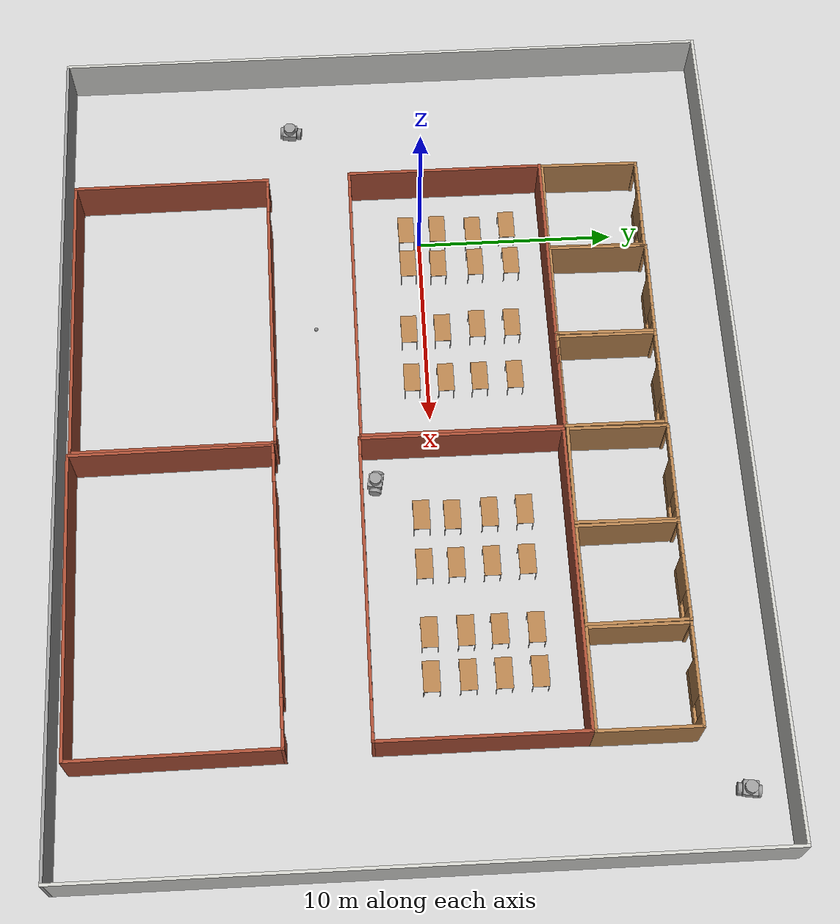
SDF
<sdf version="1.6">
 <world name="default">
  <plugin name="hello" filename="libhello.so"/>
  <light name="sun" type="directional">
   <pose>0 0 10 0 -0 0</pose>
   <diffuse>0.8 0.8 0.8 1</diffuse>
   <specular>0.2 0.2 0.2 1</specular>
   <attenuation>
    <range>1000</range>
    <constant>0.9</constant>
    <linear>0.01</linear>
    <quadratic>0.001</quadratic>
   </attenuation>
   <direction>-0.5 0.1 -0.9</direction>
  </light>
  <model name="ground_plane">
   <static>1</static>
   <link name="link">
    <collision name="collision">
     <geometry><plane><normal>0 0 1</normal><size>100 100</size></plane></geometry>
     <surface>
      <contact><collide_bitmask>65535</collide_bitmask></contact>
      <friction><ode><mu>100</mu><mu2>50</mu2></ode></friction>
     </surface>
    </collision>
    <visual name="visual">
     <cast_shadows>0</cast_shadows>
     <geometry><plane><normal>0 0 1</normal><size>100 100</size></plane></geometry>
     <material>
      <script><uri>file://media/materials/scripts/gazebo.material</uri><name>Gazebo/Grey</name></script>
     </material>
    </visual>
   </link>
  </model>
  <gravity>0 0 -9.8</gravity>
  <magnetic_field>6e-06 2.3e-05 -4.2e-05</magnetic_field>
  <atmosphere type="adiabatic"/>
  <physics name="default_physics" default="0" type="ode">
   <max_step_size>0.001</max_step_size>
   <real_time_factor>1</real_time_factor>
   <real_time_update_rate>1000</real_time_update_rate>
  </physics>
  <scene><ambient>0.4 0.4 0.4 1</ambient><background>0.7 0.7 0.7 1</background><shadows>1</shadows></scene>
  <spherical_coordinates>
   <surface_model>EARTH_WGS84</surface_model>
   <latitude_deg>0</latitude_deg>
   <longitude_deg>0</longitude_deg>
   <elevation>0</elevation>
   <heading_deg>0</heading_deg>
  </spherical_coordinates>
  <model name="classroom">
   <pose>4.425 1.455 0 0 -0 0</pose>
   <link name="Wall_0">
    <collision name="Wall_0_Collision">
     <geometry><box><size>10 0.15 2.5</size></box></geometry>
     <pose>0 0 1.25 0 -0 0</pose>
    </collision>
    <visual name="Wall_0_Visual">
     <pose>0 0 1.25 0 -0 0</pose>
     <geometry><box><size>10 0.15 2.5</size></box></geometry>
     <material>
      <script><uri>file://media/materials/scripts/gazebo.material</uri><name>Gazebo/Bricks</name></script>
      <ambient>1 1 1 1</ambient>
     </material>
     <meta><layer>0</layer></meta>
    </visual>
    <pose>-7.425 0 0 0 -0 1.5708</pose>
   </link>
   <link name="Wall_2">
    <collision name="Wall_2_Collision">
     <geometry><box><size>15 0.15 2.5</size></box></geometry>
     <pose>0 0 1.25 0 -0 0</pose>
    </collision>
    <visual name="Wall_2_Visual">
     <pose>0 0 1.25 0 -0 0</pose>
     <geometry><box><size>15 0.15 2.5</size></box></geometry>
     <material>
      <script><uri>file://media/materials/scripts/gazebo.material</uri><name>Gazebo/Bricks</name></script>
      <ambient>1 1 1 1</ambient>
     </material>
     <meta><layer>0</layer></meta>
    </visual>
    <pose>0 4.925 0 0 -0 0</pose>
   </link>
   <link name="Wall_4">
    <collision name="Wall_4_Collision">
     <geometry><box><size>10 0.15 2.5</size></box></geometry>
     <pose>0 0 1.25 0 -0 0</pose>
    </collision>
    <visual name="Wall_4_Visual">
     <pose>0 0 1.25 0 -0 0</pose>
     <geometry><box><size>10 0.15 2.5</size></box></geometry>
     <material>
      <script><uri>file://media/materials/scripts/gazebo.material</uri><name>Gazebo/Bricks</name></script>
      <ambient>1 1 1 1</ambient>
     </material>
     <meta><layer>0</layer></meta>
    </visual>
    <pose>7.425 0 0 0 0 -1.5708</pose>
   </link>
   <link name="Wall_6">
    <pose>0 -4.925 0 0 -0 0</pose>
    <visual name="Wall_6_Visual_0">
     <pose>-7.03429 0 1.25 0 -0 0</pose>
     <geometry><box><size>0.931421 0.15 2.5</size></box></geometry>
     <material>
      <script><uri>file://media/materials/scripts/gazebo.material</uri><name>Gazebo/Bricks</name></script>
      <ambient>1 1 1 1</ambient>
     </material>
     <meta><layer>0</layer></meta>
    </visual>
    <collision name="Wall_6_Collision_0">
     <geometry><box><size>0.931421 0.15 2.5</size></box></geometry>
     <pose>-7.03429 0 1.25 0 -0 0</pose>
    </collision>
    <visual name="Wall_6_Visual_1">
     <pose>0.218509 0 1.25 0 -0 0</pose>
     <geometry><box><size>10.5742 0.15 2.5</size></box></geometry>
     <material>
      <script><uri>file://media/materials/scripts/gazebo.material</uri><name>Gazebo/Bricks</name></script>
      <ambient>1 1 1 1</ambient>
     </material>
     <meta><layer>0</layer></meta>
    </visual>
    <collision name="Wall_6_Collision_1">
     <geometry><box><size>10.5742 0.15 2.5</size></box></geometry>
     <pose>0.218509 0 1.25 0 -0 0</pose>
    </collision>
    <visual name="Wall_6_Visual_2">
     <pose>7.2528 0 1.25 0 -0 0</pose>
     <geometry><box><size>0.494402 0.15 2.5</size></box></geometry>
     <material>
      <script><uri>file://media/materials/scripts/gazebo.material</uri><name>Gazebo/Bricks</name></script>
      <ambient>1 1 1 1</ambient>
     </material>
     <meta><layer>0</layer></meta>
    </visual>
    <collision name="Wall_6_Collision_2">
     <geometry><box><size>0.494402 0.15 2.5</size></box></geometry>
     <pose>7.2528 0 1.25 0 -0 0</pose>
    </collision>
    <visual name="Wall_6_Visual_3">
     <pose>-5.81858 0 2.25 0 -0 0</pose>
     <geometry><box><size>1.5 0.15 0.5</size></box></geometry>
     <material>
      <script><uri>file://media/materials/scripts/gazebo.material</uri><name>Gazebo/Bricks</name></script>
      <ambient>1 1 1 1</ambient>
     </material>
     <meta><layer>0</layer></meta>
    </visual>
    <collision name="Wall_6_Collision_3">
     <geometry><box><size>1.5 0.15 0.5</size></box></geometry>
     <pose>-5.81858 0 2.25 0 -0 0</pose>
    </collision>
    <visual name="Wall_6_Visual_4">
     <pose>6.2556 0 2.25 0 -0 0</pose>
     <geometry><box><size>1.5 0.15 0.5</size></box></geometry>
     <material>
      <script><uri>file://media/materials/scripts/gazebo.material</uri><name>Gazebo/Bricks</name></script>
      <ambient>1 1 1 1</ambient>
     </material>
     <meta><layer>0</layer></meta>
    </visual>
    <collision name="Wall_6_Collision_4">
     <geometry><box><size>1.5 0.15 0.5</size></box></geometry>
     <pose>6.2556 0 2.25 0 -0 0</pose>
    </collision>
   </link>
   <static>1</static>
  </model>
  <model name="studio">
   <pose>9.41356 8.87492 0 0 -0 3.14131</pose>
   <link name="Wall_10">
    <collision name="Wall_10_Collision">
     <geometry><box><size>5 0.15 2.5</size></box></geometry>
     <pose>0 0 1.25 0 -0 0</pose>
    </collision>
    <visual name="Wall_10_Visual">
     <pose>0 0 1.25 0 -0 0</pose>
     <geometry><box><size>5 0.15 2.5</size></box></geometry>
     <material>
      <script><uri>file://media/materials/scripts/gazebo.material</uri><name>Gazebo/Wood</name></script>
      <ambient>1 1 1 1</ambient>
     </material>
     <meta><layer>0</layer></meta>
    </visual>
    <pose>0 2.42482 0 0 0 -7.3e-05</pose>
   </link>
   <link name="Wall_13">
    <collision name="Wall_13_Collision">
     <geometry><box><size>5 0.15 2.5</size></box></geometry>
     <pose>0 0 1.25 0 -0 0</pose>
    </collision>
    <visual name="Wall_13_Visual">
     <pose>0 0 1.25 0 -0 0</pose>
     <geometry><box><size>5 0.15 2.5</size></box></geometry>
     <material>
      <script><uri>file://media/materials/scripts/gazebo.material</uri><name>Gazebo/Wood</name></script>
      <ambient>1 1 1 1</ambient>
     </material>
     <meta><layer>0</layer></meta>
    </visual>
    <pose>-2.42502 -3e-06 0 0 0 -1.5708</pose>
   </link>
   <link name="Wall_15">
    <pose>-2e-05 -2.425 0 0 -0 0</pose>
    <visual name="Wall_15_Visual_0">
     <pose>-2.17395 0 1.25 0 -0 0</pose>
     <geometry><box><size>0.652095 0.15 2.5</size></box></geometry>
     <material>
      <script><uri>file://media/materials/scripts/gazebo.material</uri><name>Gazebo/Wood</name></script>
      <ambient>1 1 1 1</ambient>
     </material>
     <meta><layer>0</layer></meta>
    </visual>
    <collision name="Wall_15_Collision_0">
     <geometry><box><size>0.652095 0.15 2.5</size></box></geometry>
     <pose>-2.17395 0 1.25 0 -0 0</pose>
    </collision>
    <visual name="Wall_15_Visual_1">
     <pose>2.38574 0 1.25 0 -0 0</pose>
     <geometry><box><size>0.228515 0.15 2.5</size></box></geometry>
     <material>
      <script><uri>file://media/materials/scripts/gazebo.material</uri><name>Gazebo/Wood</name></script>
      <ambient>1 1 1 1</ambient>
     </material>
     <meta><layer>0</layer></meta>
    </visual>
    <collision name="Wall_15_Collision_1">
     <geometry><box><size>0.228515 0.15 2.5</size></box></geometry>
     <pose>2.38574 0 1.25 0 -0 0</pose>
    </collision>
    <visual name="Wall_15_Visual_2">
     <pose>-0.53821 0 0.25 0 -0 0</pose>
     <geometry><box><size>2.61939 0.15 0.5</size></box></geometry>
     <material>
      <script><uri>file://media/materials/scripts/gazebo.material</uri><name>Gazebo/Wood</name></script>
      <ambient>1 1 1 1</ambient>
     </material>
     <meta><layer>0</layer></meta>
    </visual>
    <collision name="Wall_15_Collision_2">
     <geometry><box><size>2.61939 0.15 0.5</size></box></geometry>
     <pose>-0.53821 0 0.25 0 -0 0</pose>
    </collision>
    <visual name="Wall_15_Visual_3">
     <pose>-0.13821 0 1.5 0 -0 0</pose>
     <geometry><box><size>1.81939 0.15 2</size></box></geometry>
     <material>
      <script><uri>file://media/materials/scripts/gazebo.material</uri><name>Gazebo/Wood</name></script>
      <ambient>1 1 1 1</ambient>
     </material>
     <meta><layer>0</layer></meta>
    </visual>
    <collision name="Wall_15_Collision_3">
     <geometry><box><size>1.81939 0.15 2</size></box></geometry>
     <pose>-0.13821 0 1.5 0 -0 0</pose>
    </collision>
    <visual name="Wall_15_Visual_4">
     <pose>-1.4479 0 1.9 0 -0 0</pose>
     <geometry><box><size>0.8 0.15 1.2</size></box></geometry>
     <material>
      <script><uri>file://media/materials/scripts/gazebo.material</uri><name>Gazebo/Wood</name></script>
      <ambient>1 1 1 1</ambient>
     </material>
     <meta><layer>0</layer></meta>
    </visual>
    <collision name="Wall_15_Collision_4">
     <geometry><box><size>0.8 0.15 1.2</size></box></geometry>
     <pose>-1.4479 0 1.9 0 -0 0</pose>
    </collision>
    <visual name="Wall_15_Visual_5">
     <pose>1.52148 0 2.25 0 -0 0</pose>
     <geometry><box><size>1.5 0.15 0.5</size></box></geometry>
     <material>
      <script><uri>file://media/materials/scripts/gazebo.material</uri><name>Gazebo/Wood</name></script>
      <ambient>1 1 1 1</ambient>
     </material>
     <meta><layer>0</layer></meta>
    </visual>
    <collision name="Wall_15_Collision_5">
     <geometry><box><size>1.5 0.15 0.5</size></box></geometry>
     <pose>1.52148 0 2.25 0 -0 0</pose>
    </collision>
   </link>
   <link name="Wall_16">
    <collision name="Wall_16_Collision">
     <geometry><box><size>4.99965 0.15 2.5</size></box></geometry>
     <pose>0 0 1.25 0 -0 0</pose>
    </collision>
    <visual name="Wall_16_Visual">
     <pose>0 0 1.25 0 -0 0</pose>
     <geometry><box><size>4.99965 0.15 2.5</size></box></geometry>
     <material>
      <script><uri>file://media/materials/scripts/gazebo.material</uri><name>Gazebo/Wood</name></script>
      <ambient>1 1 1 1</ambient>
     </material>
     <meta><layer>0</layer></meta>
    </visual>
    <pose>2.425 -0.00018 0 0 -0 1.57079</pose>
   </link>
   <static>1</static>
  </model>
  <model name="studio_0">
   <pose>4.40677 8.90584 0 0 -0 3.12886</pose>
   <link name="Wall_10">
    <collision name="Wall_10_Collision">
     <geometry><box><size>5 0.15 2.5</size></box></geometry>
     <pose>0 0 1.25 0 -0 0</pose>
    </collision>
    <visual name="Wall_10_Visual">
     <pose>0 0 1.25 0 -0 0</pose>
     <geometry><box><size>5 0.15 2.5</size></box></geometry>
     <material>
      <script><uri>file://media/materials/scripts/gazebo.material</uri><name>Gazebo/Wood</name></script>
      <ambient>1 1 1 1</ambient>
     </material>
     <meta><layer>0</layer></meta>
    </visual>
    <pose>0 2.42482 0 0 0 -7.3e-05</pose>
   </link>
   <link name="Wall_13">
    <collision name="Wall_13_Collision">
     <geometry><box><size>5 0.15 2.5</size></box></geometry>
     <pose>0 0 1.25 0 -0 0</pose>
    </collision>
    <visual name="Wall_13_Visual">
     <pose>0 0 1.25 0 -0 0</pose>
     <geometry><box><size>5 0.15 2.5</size></box></geometry>
     <material>
      <script><uri>file://media/materials/scripts/gazebo.material</uri><name>Gazebo/Wood</name></script>
      <ambient>1 1 1 1</ambient>
     </material>
     <meta><layer>0</layer></meta>
    </visual>
    <pose>-2.42502 -3e-06 0 0 0 -1.5708</pose>
   </link>
   <link name="Wall_15">
    <pose>-2e-05 -2.425 0 0 -0 0</pose>
    <visual name="Wall_15_Visual_0">
     <pose>-2.17395 0 1.25 0 -0 0</pose>
     <geometry><box><size>0.652095 0.15 2.5</size></box></geometry>
     <material>
      <script><uri>file://media/materials/scripts/gazebo.material</uri><name>Gazebo/Wood</name></script>
      <ambient>1 1 1 1</ambient>
     </material>
     <meta><layer>0</layer></meta>
    </visual>
    <collision name="Wall_15_Collision_0">
     <geometry><box><size>0.652095 0.15 2.5</size></box></geometry>
     <pose>-2.17395 0 1.25 0 -0 0</pose>
    </collision>
    <visual name="Wall_15_Visual_1">
     <pose>2.38574 0 1.25 0 -0 0</pose>
     <geometry><box><size>0.228515 0.15 2.5</size></box></geometry>
     <material>
      <script><uri>file://media/materials/scripts/gazebo.material</uri><name>Gazebo/Wood</name></script>
      <ambient>1 1 1 1</ambient>
     </material>
     <meta><layer>0</layer></meta>
    </visual>
    <collision name="Wall_15_Collision_1">
     <geometry><box><size>0.228515 0.15 2.5</size></box></geometry>
     <pose>2.38574 0 1.25 0 -0 0</pose>
    </collision>
    <visual name="Wall_15_Visual_2">
     <pose>-0.53821 0 0.25 0 -0 0</pose>
     <geometry><box><size>2.61939 0.15 0.5</size></box></geometry>
     <material>
      <script><uri>file://media/materials/scripts/gazebo.material</uri><name>Gazebo/Wood</name></script>
      <ambient>1 1 1 1</ambient>
     </material>
     <meta><layer>0</layer></meta>
    </visual>
    <collision name="Wall_15_Collision_2">
     <geometry><box><size>2.61939 0.15 0.5</size></box></geometry>
     <pose>-0.53821 0 0.25 0 -0 0</pose>
    </collision>
    <visual name="Wall_15_Visual_3">
     <pose>-0.13821 0 1.5 0 -0 0</pose>
     <geometry><box><size>1.81939 0.15 2</size></box></geometry>
     <material>
      <script><uri>file://media/materials/scripts/gazebo.material</uri><name>Gazebo/Wood</name></script>
      <ambient>1 1 1 1</ambient>
     </material>
     <meta><layer>0</layer></meta>
    </visual>
    <collision name="Wall_15_Collision_3">
     <geometry><box><size>1.81939 0.15 2</size></box></geometry>
     <pose>-0.13821 0 1.5 0 -0 0</pose>
    </collision>
    <visual name="Wall_15_Visual_4">
     <pose>-1.4479 0 1.9 0 -0 0</pose>
     <geometry><box><size>0.8 0.15 1.2</size></box></geometry>
     <material>
      <script><uri>file://media/materials/scripts/gazebo.material</uri><name>Gazebo/Wood</name></script>
      <ambient>1 1 1 1</ambient>
     </material>
     <meta><layer>0</layer></meta>
    </visual>
    <collision name="Wall_15_Collision_4">
     <geometry><box><size>0.8 0.15 1.2</size></box></geometry>
     <pose>-1.4479 0 1.9 0 -0 0</pose>
    </collision>
    <visual name="Wall_15_Visual_5">
     <pose>1.52148 0 2.25 0 -0 0</pose>
     <geometry><box><size>1.5 0.15 0.5</size></box></geometry>
     <material>
      <script><uri>file://media/materials/scripts/gazebo.material</uri><name>Gazebo/Wood</name></script>
      <ambient>1 1 1 1</ambient>
     </material>
     <meta><layer>0</layer></meta>
    </visual>
    <collision name="Wall_15_Collision_5">
     <geometry><box><size>1.5 0.15 0.5</size></box></geometry>
     <pose>1.52148 0 2.25 0 -0 0</pose>
    </collision>
   </link>
   <link name="Wall_16">
    <collision name="Wall_16_Collision">
     <geometry><box><size>4.99965 0.15 2.5</size></box></geometry>
     <pose>0 0 1.25 0 -0 0</pose>
    </collision>
    <visual name="Wall_16_Visual">
     <pose>0 0 1.25 0 -0 0</pose>
     <geometry><box><size>4.99965 0.15 2.5</size></box></geometry>
     <material>
      <script><uri>file://media/materials/scripts/gazebo.material</uri><name>Gazebo/Wood</name></script>
      <ambient>1 1 1 1</ambient>
     </material>
     <meta><layer>0</layer></meta>
    </visual>
    <pose>2.425 -0.00018 0 0 -0 1.57079</pose>
   </link>
   <static>1</static>
  </model>
  <model name="studio_1">
   <pose>-0.513767 8.90661 0 0 -0 3.12855</pose>
   <link name="Wall_10">
    <collision name="Wall_10_Collision">
     <geometry><box><size>5 0.15 2.5</size></box></geometry>
     <pose>0 0 1.25 0 -0 0</pose>
    </collision>
    <visual name="Wall_10_Visual">
     <pose>0 0 1.25 0 -0 0</pose>
     <geometry><box><size>5 0.15 2.5</size></box></geometry>
     <material>
      <script><uri>file://media/materials/scripts/gazebo.material</uri><name>Gazebo/Wood</name></script>
      <ambient>1 1 1 1</ambient>
     </material>
     <meta><layer>0</layer></meta>
    </visual>
    <pose>0 2.42482 0 0 0 -7.3e-05</pose>
   </link>
   <link name="Wall_13">
    <collision name="Wall_13_Collision">
     <geometry><box><size>5 0.15 2.5</size></box></geometry>
     <pose>0 0 1.25 0 -0 0</pose>
    </collision>
    <visual name="Wall_13_Visual">
     <pose>0 0 1.25 0 -0 0</pose>
     <geometry><box><size>5 0.15 2.5</size></box></geometry>
     <material>
      <script><uri>file://media/materials/scripts/gazebo.material</uri><name>Gazebo/Wood</name></script>
      <ambient>1 1 1 1</ambient>
     </material>
     <meta><layer>0</layer></meta>
    </visual>
    <pose>-2.42502 -3e-06 0 0 0 -1.5708</pose>
   </link>
   <link name="Wall_15">
    <pose>-2e-05 -2.425 0 0 -0 0</pose>
    <visual name="Wall_15_Visual_0">
     <pose>-2.17395 0 1.25 0 -0 0</pose>
     <geometry><box><size>0.652095 0.15 2.5</size></box></geometry>
     <material>
      <script><uri>file://media/materials/scripts/gazebo.material</uri><name>Gazebo/Wood</name></script>
      <ambient>1 1 1 1</ambient>
     </material>
     <meta><layer>0</layer></meta>
    </visual>
    <collision name="Wall_15_Collision_0">
     <geometry><box><size>0.652095 0.15 2.5</size></box></geometry>
     <pose>-2.17395 0 1.25 0 -0 0</pose>
    </collision>
    <visual name="Wall_15_Visual_1">
     <pose>2.38574 0 1.25 0 -0 0</pose>
     <geometry><box><size>0.228515 0.15 2.5</size></box></geometry>
     <material>
      <script><uri>file://media/materials/scripts/gazebo.material</uri><name>Gazebo/Wood</name></script>
      <ambient>1 1 1 1</ambient>
     </material>
     <meta><layer>0</layer></meta>
    </visual>
    <collision name="Wall_15_Collision_1">
     <geometry><box><size>0.228515 0.15 2.5</size></box></geometry>
     <pose>2.38574 0 1.25 0 -0 0</pose>
    </collision>
    <visual name="Wall_15_Visual_2">
     <pose>-0.53821 0 0.25 0 -0 0</pose>
     <geometry><box><size>2.61939 0.15 0.5</size></box></geometry>
     <material>
      <script><uri>file://media/materials/scripts/gazebo.material</uri><name>Gazebo/Wood</name></script>
      <ambient>1 1 1 1</ambient>
     </material>
     <meta><layer>0</layer></meta>
    </visual>
    <collision name="Wall_15_Collision_2">
     <geometry><box><size>2.61939 0.15 0.5</size></box></geometry>
     <pose>-0.53821 0 0.25 0 -0 0</pose>
    </collision>
    <visual name="Wall_15_Visual_3">
     <pose>-0.13821 0 1.5 0 -0 0</pose>
     <geometry><box><size>1.81939 0.15 2</size></box></geometry>
     <material>
      <script><uri>file://media/materials/scripts/gazebo.material</uri><name>Gazebo/Wood</name></script>
      <ambient>1 1 1 1</ambient>
     </material>
     <meta><layer>0</layer></meta>
    </visual>
    <collision name="Wall_15_Collision_3">
     <geometry><box><size>1.81939 0.15 2</size></box></geometry>
     <pose>-0.13821 0 1.5 0 -0 0</pose>
    </collision>
    <visual name="Wall_15_Visual_4">
     <pose>-1.4479 0 1.9 0 -0 0</pose>
     <geometry><box><size>0.8 0.15 1.2</size></box></geometry>
     <material>
      <script><uri>file://media/materials/scripts/gazebo.material</uri><name>Gazebo/Wood</name></script>
      <ambient>1 1 1 1</ambient>
     </material>
     <meta><layer>0</layer></meta>
    </visual>
    <collision name="Wall_15_Collision_4">
     <geometry><box><size>0.8 0.15 1.2</size></box></geometry>
     <pose>-1.4479 0 1.9 0 -0 0</pose>
    </collision>
    <visual name="Wall_15_Visual_5">
     <pose>1.52148 0 2.25 0 -0 0</pose>
     <geometry><box><size>1.5 0.15 0.5</size></box></geometry>
     <material>
      <script><uri>file://media/materials/scripts/gazebo.material</uri><name>Gazebo/Wood</name></script>
      <ambient>1 1 1 1</ambient>
     </material>
     <meta><layer>0</layer></meta>
    </visual>
    <collision name="Wall_15_Collision_5">
     <geometry><box><size>1.5 0.15 0.5</size></box></geometry>
     <pose>1.52148 0 2.25 0 -0 0</pose>
    </collision>
   </link>
   <link name="Wall_16">
    <collision name="Wall_16_Collision">
     <geometry><box><size>4.99965 0.15 2.5</size></box></geometry>
     <pose>0 0 1.25 0 -0 0</pose>
    </collision>
    <visual name="Wall_16_Visual">
     <pose>0 0 1.25 0 -0 0</pose>
     <geometry><box><size>4.99965 0.15 2.5</size></box></geometry>
     <material>
      <script><uri>file://media/materials/scripts/gazebo.material</uri><name>Gazebo/Wood</name></script>
      <ambient>1 1 1 1</ambient>
     </material>
     <meta><layer>0</layer></meta>
    </visual>
    <pose>2.425 -0.00018 0 0 -0 1.57079</pose>
   </link>
   <static>1</static>
  </model>
  <model name="classroom_0">
   <pose>19.4231 1.37785 0 0 -0 0</pose>
   <link name="Wall_0">
    <collision name="Wall_0_Collision">
     <geometry><box><size>10 0.15 2.5</size></box></geometry>
     <pose>0 0 1.25 0 -0 0</pose>
    </collision>
    <visual name="Wall_0_Visual">
     <pose>0 0 1.25 0 -0 0</pose>
     <geometry><box><size>10 0.15 2.5</size></box></geometry>
     <material>
      <script><uri>file://media/materials/scripts/gazebo.material</uri><name>Gazebo/Bricks</name></script>
      <ambient>1 1 1 1</ambient>
     </material>
     <meta><layer>0</layer></meta>
    </visual>
    <pose>-7.425 0 0 0 -0 1.5708</pose>
   </link>
   <link name="Wall_2">
    <collision name="Wall_2_Collision">
     <geometry><box><size>15 0.15 2.5</size></box></geometry>
     <pose>0 0 1.25 0 -0 0</pose>
    </collision>
    <visual name="Wall_2_Visual">
     <pose>0 0 1.25 0 -0 0</pose>
     <geometry><box><size>15 0.15 2.5</size></box></geometry>
     <material>
      <script><uri>file://media/materials/scripts/gazebo.material</uri><name>Gazebo/Bricks</name></script>
      <ambient>1 1 1 1</ambient>
     </material>
     <meta><layer>0</layer></meta>
    </visual>
    <pose>0 4.925 0 0 -0 0</pose>
   </link>
   <link name="Wall_4">
    <collision name="Wall_4_Collision">
     <geometry><box><size>10 0.15 2.5</size></box></geometry>
     <pose>0 0 1.25 0 -0 0</pose>
    </collision>
    <visual name="Wall_4_Visual">
     <pose>0 0 1.25 0 -0 0</pose>
     <geometry><box><size>10 0.15 2.5</size></box></geometry>
     <material>
      <script><uri>file://media/materials/scripts/gazebo.material</uri><name>Gazebo/Bricks</name></script>
      <ambient>1 1 1 1</ambient>
     </material>
     <meta><layer>0</layer></meta>
    </visual>
    <pose>7.425 0 0 0 0 -1.5708</pose>
   </link>
   <link name="Wall_6">
    <pose>0 -4.925 0 0 -0 0</pose>
    <visual name="Wall_6_Visual_0">
     <pose>-7.03429 0 1.25 0 -0 0</pose>
     <geometry><box><size>0.931421 0.15 2.5</size></box></geometry>
     <material>
      <script><uri>file://media/materials/scripts/gazebo.material</uri><name>Gazebo/Bricks</name></script>
      <ambient>1 1 1 1</ambient>
     </material>
     <meta><layer>0</layer></meta>
    </visual>
    <collision name="Wall_6_Collision_0">
     <geometry><box><size>0.931421 0.15 2.5</size></box></geometry>
     <pose>-7.03429 0 1.25 0 -0 0</pose>
    </collision>
    <visual name="Wall_6_Visual_1">
     <pose>0.218509 0 1.25 0 -0 0</pose>
     <geometry><box><size>10.5742 0.15 2.5</size></box></geometry>
     <material>
      <script><uri>file://media/materials/scripts/gazebo.material</uri><name>Gazebo/Bricks</name></script>
      <ambient>1 1 1 1</ambient>
     </material>
     <meta><layer>0</layer></meta>
    </visual>
    <collision name="Wall_6_Collision_1">
     <geometry><box><size>10.5742 0.15 2.5</size></box></geometry>
     <pose>0.218509 0 1.25 0 -0 0</pose>
    </collision>
    <visual name="Wall_6_Visual_2">
     <pose>7.2528 0 1.25 0 -0 0</pose>
     <geometry><box><size>0.494402 0.15 2.5</size></box></geometry>
     <material>
      <script><uri>file://media/materials/scripts/gazebo.material</uri><name>Gazebo/Bricks</name></script>
      <ambient>1 1 1 1</ambient>
     </material>
     <meta><layer>0</layer></meta>
    </visual>
    <collision name="Wall_6_Collision_2">
     <geometry><box><size>0.494402 0.15 2.5</size></box></geometry>
     <pose>7.2528 0 1.25 0 -0 0</pose>
    </collision>
    <visual name="Wall_6_Visual_3">
     <pose>-5.81858 0 2.25 0 -0 0</pose>
     <geometry><box><size>1.5 0.15 0.5</size></box></geometry>
     <material>
      <script><uri>file://media/materials/scripts/gazebo.material</uri><name>Gazebo/Bricks</name></script>
      <ambient>1 1 1 1</ambient>
     </material>
     <meta><layer>0</layer></meta>
    </visual>
    <collision name="Wall_6_Collision_3">
     <geometry><box><size>1.5 0.15 0.5</size></box></geometry>
     <pose>-5.81858 0 2.25 0 -0 0</pose>
    </collision>
    <visual name="Wall_6_Visual_4">
     <pose>6.2556 0 2.25 0 -0 0</pose>
     <geometry><box><size>1.5 0.15 0.5</size></box></geometry>
     <material>
      <script><uri>file://media/materials/scripts/gazebo.material</uri><name>Gazebo/Bricks</name></script>
      <ambient>1 1 1 1</ambient>
     </material>
     <meta><layer>0</layer></meta>
    </visual>
    <collision name="Wall_6_Collision_4">
     <geometry><box><size>1.5 0.15 0.5</size></box></geometry>
     <pose>6.2556 0 2.25 0 -0 0</pose>
    </collision>
   </link>
   <static>1</static>
  </model>
  <model name="studio_2">
   <pose>14.4518 8.89939 0 0 -0 3.13147</pose>
   <link name="Wall_10">
    <collision name="Wall_10_Collision">
     <geometry><box><size>5 0.15 2.5</size></box></geometry>
     <pose>0 0 1.25 0 -0 0</pose>
    </collision>
    <visual name="Wall_10_Visual">
     <pose>0 0 1.25 0 -0 0</pose>
     <geometry><box><size>5 0.15 2.5</size></box></geometry>
     <material>
      <script><uri>file://media/materials/scripts/gazebo.material</uri><name>Gazebo/Wood</name></script>
      <ambient>1 1 1 1</ambient>
     </material>
     <meta><layer>0</layer></meta>
    </visual>
    <pose>0 2.42482 0 0 0 -7.3e-05</pose>
   </link>
   <link name="Wall_13">
    <collision name="Wall_13_Collision">
     <geometry><box><size>5 0.15 2.5</size></box></geometry>
     <pose>0 0 1.25 0 -0 0</pose>
    </collision>
    <visual name="Wall_13_Visual">
     <pose>0 0 1.25 0 -0 0</pose>
     <geometry><box><size>5 0.15 2.5</size></box></geometry>
     <material>
      <script><uri>file://media/materials/scripts/gazebo.material</uri><name>Gazebo/Wood</name></script>
      <ambient>1 1 1 1</ambient>
     </material>
     <meta><layer>0</layer></meta>
    </visual>
    <pose>-2.42502 -3e-06 0 0 0 -1.5708</pose>
   </link>
   <link name="Wall_15">
    <pose>-2e-05 -2.425 0 0 -0 0</pose>
    <visual name="Wall_15_Visual_0">
     <pose>-2.17395 0 1.25 0 -0 0</pose>
     <geometry><box><size>0.652095 0.15 2.5</size></box></geometry>
     <material>
      <script><uri>file://media/materials/scripts/gazebo.material</uri><name>Gazebo/Wood</name></script>
      <ambient>1 1 1 1</ambient>
     </material>
     <meta><layer>0</layer></meta>
    </visual>
    <collision name="Wall_15_Collision_0">
     <geometry><box><size>0.652095 0.15 2.5</size></box></geometry>
     <pose>-2.17395 0 1.25 0 -0 0</pose>
    </collision>
    <visual name="Wall_15_Visual_1">
     <pose>2.38574 0 1.25 0 -0 0</pose>
     <geometry><box><size>0.228515 0.15 2.5</size></box></geometry>
     <material>
      <script><uri>file://media/materials/scripts/gazebo.material</uri><name>Gazebo/Wood</name></script>
      <ambient>1 1 1 1</ambient>
     </material>
     <meta><layer>0</layer></meta>
    </visual>
    <collision name="Wall_15_Collision_1">
     <geometry><box><size>0.228515 0.15 2.5</size></box></geometry>
     <pose>2.38574 0 1.25 0 -0 0</pose>
    </collision>
    <visual name="Wall_15_Visual_2">
     <pose>-0.53821 0 0.25 0 -0 0</pose>
     <geometry><box><size>2.61939 0.15 0.5</size></box></geometry>
     <material>
      <script><uri>file://media/materials/scripts/gazebo.material</uri><name>Gazebo/Wood</name></script>
      <ambient>1 1 1 1</ambient>
     </material>
     <meta><layer>0</layer></meta>
    </visual>
    <collision name="Wall_15_Collision_2">
     <geometry><box><size>2.61939 0.15 0.5</size></box></geometry>
     <pose>-0.53821 0 0.25 0 -0 0</pose>
    </collision>
    <visual name="Wall_15_Visual_3">
     <pose>-0.13821 0 1.5 0 -0 0</pose>
     <geometry><box><size>1.81939 0.15 2</size></box></geometry>
     <material>
      <script><uri>file://media/materials/scripts/gazebo.material</uri><name>Gazebo/Wood</name></script>
      <ambient>1 1 1 1</ambient>
     </material>
     <meta><layer>0</layer></meta>
    </visual>
    <collision name="Wall_15_Collision_3">
     <geometry><box><size>1.81939 0.15 2</size></box></geometry>
     <pose>-0.13821 0 1.5 0 -0 0</pose>
    </collision>
    <visual name="Wall_15_Visual_4">
     <pose>-1.4479 0 1.9 0 -0 0</pose>
     <geometry><box><size>0.8 0.15 1.2</size></box></geometry>
     <material>
      <script><uri>file://media/materials/scripts/gazebo.material</uri><name>Gazebo/Wood</name></script>
      <ambient>1 1 1 1</ambient>
     </material>
     <meta><layer>0</layer></meta>
    </visual>
    <collision name="Wall_15_Collision_4">
     <geometry><box><size>0.8 0.15 1.2</size></box></geometry>
     <pose>-1.4479 0 1.9 0 -0 0</pose>
    </collision>
    <visual name="Wall_15_Visual_5">
     <pose>1.52148 0 2.25 0 -0 0</pose>
     <geometry><box><size>1.5 0.15 0.5</size></box></geometry>
     <material>
      <script><uri>file://media/materials/scripts/gazebo.material</uri><name>Gazebo/Wood</name></script>
      <ambient>1 1 1 1</ambient>
     </material>
     <meta><layer>0</layer></meta>
    </visual>
    <collision name="Wall_15_Collision_5">
     <geometry><box><size>1.5 0.15 0.5</size></box></geometry>
     <pose>1.52148 0 2.25 0 -0 0</pose>
    </collision>
   </link>
   <link name="Wall_16">
    <collision name="Wall_16_Collision">
     <geometry><box><size>4.99965 0.15 2.5</size></box></geometry>
     <pose>0 0 1.25 0 -0 0</pose>
    </collision>
    <visual name="Wall_16_Visual">
     <pose>0 0 1.25 0 -0 0</pose>
     <geometry><box><size>4.99965 0.15 2.5</size></box></geometry>
     <material>
      <script><uri>file://media/materials/scripts/gazebo.material</uri><name>Gazebo/Wood</name></script>
      <ambient>1 1 1 1</ambient>
     </material>
     <meta><layer>0</layer></meta>
    </visual>
    <pose>2.425 -0.00018 0 0 -0 1.57079</pose>
   </link>
   <static>1</static>
  </model>
  <model name="studio_3">
   <pose>19.4488 8.8882 0 0 0 -3.13599</pose>
   <link name="Wall_10">
    <collision name="Wall_10_Collision">
     <geometry><box><size>5 0.15 2.5</size></box></geometry>
     <pose>0 0 1.25 0 -0 0</pose>
    </collision>
    <visual name="Wall_10_Visual">
     <pose>0 0 1.25 0 -0 0</pose>
     <geometry><box><size>5 0.15 2.5</size></box></geometry>
     <material>
      <script><uri>file://media/materials/scripts/gazebo.material</uri><name>Gazebo/Wood</name></script>
      <ambient>1 1 1 1</ambient>
     </material>
     <meta><layer>0</layer></meta>
    </visual>
    <pose>0 2.42482 0 0 0 -7.3e-05</pose>
   </link>
   <link name="Wall_13">
    <collision name="Wall_13_Collision">
     <geometry><box><size>5 0.15 2.5</size></box></geometry>
     <pose>0 0 1.25 0 -0 0</pose>
    </collision>
    <visual name="Wall_13_Visual">
     <pose>0 0 1.25 0 -0 0</pose>
     <geometry><box><size>5 0.15 2.5</size></box></geometry>
     <material>
      <script><uri>file://media/materials/scripts/gazebo.material</uri><name>Gazebo/Wood</name></script>
      <ambient>1 1 1 1</ambient>
     </material>
     <meta><layer>0</layer></meta>
    </visual>
    <pose>-2.42502 -3e-06 0 0 0 -1.5708</pose>
   </link>
   <link name="Wall_15">
    <pose>-2e-05 -2.425 0 0 -0 0</pose>
    <visual name="Wall_15_Visual_0">
     <pose>-2.17395 0 1.25 0 -0 0</pose>
     <geometry><box><size>0.652095 0.15 2.5</size></box></geometry>
     <material>
      <script><uri>file://media/materials/scripts/gazebo.material</uri><name>Gazebo/Wood</name></script>
      <ambient>1 1 1 1</ambient>
     </material>
     <meta><layer>0</layer></meta>
    </visual>
    <collision name="Wall_15_Collision_0">
     <geometry><box><size>0.652095 0.15 2.5</size></box></geometry>
     <pose>-2.17395 0 1.25 0 -0 0</pose>
    </collision>
    <visual name="Wall_15_Visual_1">
     <pose>2.38574 0 1.25 0 -0 0</pose>
     <geometry><box><size>0.228515 0.15 2.5</size></box></geometry>
     <material>
      <script><uri>file://media/materials/scripts/gazebo.material</uri><name>Gazebo/Wood</name></script>
      <ambient>1 1 1 1</ambient>
     </material>
     <meta><layer>0</layer></meta>
    </visual>
    <collision name="Wall_15_Collision_1">
     <geometry><box><size>0.228515 0.15 2.5</size></box></geometry>
     <pose>2.38574 0 1.25 0 -0 0</pose>
    </collision>
    <visual name="Wall_15_Visual_2">
     <pose>-0.53821 0 0.25 0 -0 0</pose>
     <geometry><box><size>2.61939 0.15 0.5</size></box></geometry>
     <material>
      <script><uri>file://media/materials/scripts/gazebo.material</uri><name>Gazebo/Wood</name></script>
      <ambient>1 1 1 1</ambient>
     </material>
     <meta><layer>0</layer></meta>
    </visual>
    <collision name="Wall_15_Collision_2">
     <geometry><box><size>2.61939 0.15 0.5</size></box></geometry>
     <pose>-0.53821 0 0.25 0 -0 0</pose>
    </collision>
    <visual name="Wall_15_Visual_3">
     <pose>-0.13821 0 1.5 0 -0 0</pose>
     <geometry><box><size>1.81939 0.15 2</size></box></geometry>
     <material>
      <script><uri>file://media/materials/scripts/gazebo.material</uri><name>Gazebo/Wood</name></script>
      <ambient>1 1 1 1</ambient>
     </material>
     <meta><layer>0</layer></meta>
    </visual>
    <collision name="Wall_15_Collision_3">
     <geometry><box><size>1.81939 0.15 2</size></box></geometry>
     <pose>-0.13821 0 1.5 0 -0 0</pose>
    </collision>
    <visual name="Wall_15_Visual_4">
     <pose>-1.4479 0 1.9 0 -0 0</pose>
     <geometry><box><size>0.8 0.15 1.2</size></box></geometry>
     <material>
      <script><uri>file://media/materials/scripts/gazebo.material</uri><name>Gazebo/Wood</name></script>
      <ambient>1 1 1 1</ambient>
     </material>
     <meta><layer>0</layer></meta>
    </visual>
    <collision name="Wall_15_Collision_4">
     <geometry><box><size>0.8 0.15 1.2</size></box></geometry>
     <pose>-1.4479 0 1.9 0 -0 0</pose>
    </collision>
    <visual name="Wall_15_Visual_5">
     <pose>1.52148 0 2.25 0 -0 0</pose>
     <geometry><box><size>1.5 0.15 0.5</size></box></geometry>
     <material>
      <script><uri>file://media/materials/scripts/gazebo.material</uri><name>Gazebo/Wood</name></script>
      <ambient>1 1 1 1</ambient>
     </material>
     <meta><layer>0</layer></meta>
    </visual>
    <collision name="Wall_15_Collision_5">
     <geometry><box><size>1.5 0.15 0.5</size></box></geometry>
     <pose>1.52148 0 2.25 0 -0 0</pose>
    </collision>
   </link>
   <link name="Wall_16">
    <collision name="Wall_16_Collision">
     <geometry><box><size>4.99965 0.15 2.5</size></box></geometry>
     <pose>0 0 1.25 0 -0 0</pose>
    </collision>
    <visual name="Wall_16_Visual">
     <pose>0 0 1.25 0 -0 0</pose>
     <geometry><box><size>4.99965 0.15 2.5</size></box></geometry>
     <material>
      <script><uri>file://media/materials/scripts/gazebo.material</uri><name>Gazebo/Wood</name></script>
      <ambient>1 1 1 1</ambient>
     </material>
     <meta><layer>0</layer></meta>
    </visual>
    <pose>2.425 -0.00018 0 0 -0 1.57079</pose>
   </link>
   <static>1</static>
  </model>
  <model name="studio_4">
   <pose>24.4587 8.87701 0 0 -0 3.14047</pose>
   <link name="Wall_10">
    <collision name="Wall_10_Collision">
     <geometry><box><size>5 0.15 2.5</size></box></geometry>
     <pose>0 0 1.25 0 -0 0</pose>
    </collision>
    <visual name="Wall_10_Visual">
     <pose>0 0 1.25 0 -0 0</pose>
     <geometry><box><size>5 0.15 2.5</size></box></geometry>
     <material>
      <script><uri>file://media/materials/scripts/gazebo.material</uri><name>Gazebo/Wood</name></script>
      <ambient>1 1 1 1</ambient>
     </material>
     <meta><layer>0</layer></meta>
    </visual>
    <pose>0 2.42482 0 0 0 -7.3e-05</pose>
   </link>
   <link name="Wall_13">
    <collision name="Wall_13_Collision">
     <geometry><box><size>5 0.15 2.5</size></box></geometry>
     <pose>0 0 1.25 0 -0 0</pose>
    </collision>
    <visual name="Wall_13_Visual">
     <pose>0 0 1.25 0 -0 0</pose>
     <geometry><box><size>5 0.15 2.5</size></box></geometry>
     <material>
      <script><uri>file://media/materials/scripts/gazebo.material</uri><name>Gazebo/Wood</name></script>
      <ambient>1 1 1 1</ambient>
     </material>
     <meta><layer>0</layer></meta>
    </visual>
    <pose>-2.42502 -3e-06 0 0 0 -1.5708</pose>
   </link>
   <link name="Wall_15">
    <pose>-2e-05 -2.425 0 0 -0 0</pose>
    <visual name="Wall_15_Visual_0">
     <pose>-2.17395 0 1.25 0 -0 0</pose>
     <geometry><box><size>0.652095 0.15 2.5</size></box></geometry>
     <material>
      <script><uri>file://media/materials/scripts/gazebo.material</uri><name>Gazebo/Wood</name></script>
      <ambient>1 1 1 1</ambient>
     </material>
     <meta><layer>0</layer></meta>
    </visual>
    <collision name="Wall_15_Collision_0">
     <geometry><box><size>0.652095 0.15 2.5</size></box></geometry>
     <pose>-2.17395 0 1.25 0 -0 0</pose>
    </collision>
    <visual name="Wall_15_Visual_1">
     <pose>2.38574 0 1.25 0 -0 0</pose>
     <geometry><box><size>0.228515 0.15 2.5</size></box></geometry>
     <material>
      <script><uri>file://media/materials/scripts/gazebo.material</uri><name>Gazebo/Wood</name></script>
      <ambient>1 1 1 1</ambient>
     </material>
     <meta><layer>0</layer></meta>
    </visual>
    <collision name="Wall_15_Collision_1">
     <geometry><box><size>0.228515 0.15 2.5</size></box></geometry>
     <pose>2.38574 0 1.25 0 -0 0</pose>
    </collision>
    <visual name="Wall_15_Visual_2">
     <pose>-0.53821 0 0.25 0 -0 0</pose>
     <geometry><box><size>2.61939 0.15 0.5</size></box></geometry>
     <material>
      <script><uri>file://media/materials/scripts/gazebo.material</uri><name>Gazebo/Wood</name></script>
      <ambient>1 1 1 1</ambient>
     </material>
     <meta><layer>0</layer></meta>
    </visual>
    <collision name="Wall_15_Collision_2">
     <geometry><box><size>2.61939 0.15 0.5</size></box></geometry>
     <pose>-0.53821 0 0.25 0 -0 0</pose>
    </collision>
    <visual name="Wall_15_Visual_3">
     <pose>-0.13821 0 1.5 0 -0 0</pose>
     <geometry><box><size>1.81939 0.15 2</size></box></geometry>
     <material>
      <script><uri>file://media/materials/scripts/gazebo.material</uri><name>Gazebo/Wood</name></script>
      <ambient>1 1 1 1</ambient>
     </material>
     <meta><layer>0</layer></meta>
    </visual>
    <collision name="Wall_15_Collision_3">
     <geometry><box><size>1.81939 0.15 2</size></box></geometry>
     <pose>-0.13821 0 1.5 0 -0 0</pose>
    </collision>
    <visual name="Wall_15_Visual_4">
     <pose>-1.4479 0 1.9 0 -0 0</pose>
     <geometry><box><size>0.8 0.15 1.2</size></box></geometry>
     <material>
      <script><uri>file://media/materials/scripts/gazebo.material</uri><name>Gazebo/Wood</name></script>
      <ambient>1 1 1 1</ambient>
     </material>
     <meta><layer>0</layer></meta>
    </visual>
    <collision name="Wall_15_Collision_4">
     <geometry><box><size>0.8 0.15 1.2</size></box></geometry>
     <pose>-1.4479 0 1.9 0 -0 0</pose>
    </collision>
    <visual name="Wall_15_Visual_5">
     <pose>1.52148 0 2.25 0 -0 0</pose>
     <geometry><box><size>1.5 0.15 0.5</size></box></geometry>
     <material>
      <script><uri>file://media/materials/scripts/gazebo.material</uri><name>Gazebo/Wood</name></script>
      <ambient>1 1 1 1</ambient>
     </material>
     <meta><layer>0</layer></meta>
    </visual>
    <collision name="Wall_15_Collision_5">
     <geometry><box><size>1.5 0.15 0.5</size></box></geometry>
     <pose>1.52148 0 2.25 0 -0 0</pose>
    </collision>
   </link>
   <link name="Wall_16">
    <collision name="Wall_16_Collision">
     <geometry><box><size>4.99965 0.15 2.5</size></box></geometry>
     <pose>0 0 1.25 0 -0 0</pose>
    </collision>
    <visual name="Wall_16_Visual">
     <pose>0 0 1.25 0 -0 0</pose>
     <geometry><box><size>4.99965 0.15 2.5</size></box></geometry>
     <material>
      <script><uri>file://media/materials/scripts/gazebo.material</uri><name>Gazebo/Wood</name></script>
      <ambient>1 1 1 1</ambient>
     </material>
     <meta><layer>0</layer></meta>
    </visual>
    <pose>2.425 -0.00018 0 0 -0 1.57079</pose>
   </link>
   <static>1</static>
  </model>
  <model name="table">
   <static>1</static>
   <link name="link">
    <collision name="surface">
     <pose>0 0 1 0 -0 0</pose>
     <geometry><box><size>1.5 0.8 0.03</size></box></geometry>
     <surface><friction><ode><mu>0.6</mu><mu2>0.6</mu2></ode></friction></surface>
    </collision>
    <visual name="visual1">
     <pose>0 0 1 0 -0 0</pose>
     <geometry><box><size>1.5 0.8 0.03</size></box></geometry>
     <material>
      <script><uri>file://media/materials/scripts/gazebo.material</uri><name>Gazebo/Wood</name></script>
     </material>
    </visual>
    <collision name="front_left_leg">
     <pose>0.68 0.38 0.5 0 -0 0</pose>
     <geometry><cylinder><radius>0.02</radius><length>1</length></cylinder></geometry>
    </collision>
    <visual name="front_left_leg">
     <pose>0.68 0.38 0.5 0 -0 0</pose>
     <geometry><cylinder><radius>0.02</radius><length>1</length></cylinder></geometry>
     <material>
      <script><uri>file://media/materials/scripts/gazebo.material</uri><name>Gazebo/Grey</name></script>
     </material>
    </visual>
    <collision name="front_right_leg">
     <pose>0.68 -0.38 0.5 0 -0 0</pose>
     <geometry><cylinder><radius>0.02</radius><length>1</length></cylinder></geometry>
    </collision>
    <visual name="front_right_leg">
     <pose>0.68 -0.38 0.5 0 -0 0</pose>
     <geometry><cylinder><radius>0.02</radius><length>1</length></cylinder></geometry>
     <material>
      <script><uri>file://media/materials/scripts/gazebo.material</uri><name>Gazebo/Grey</name></script>
     </material>
    </visual>
    <collision name="back_right_leg">
     <pose>-0.68 -0.38 0.5 0 -0 0</pose>
     <geometry><cylinder><radius>0.02</radius><length>1</length></cylinder></geometry>
    </collision>
    <visual name="back_right_leg">
     <pose>-0.68 -0.38 0.5 0 -0 0</pose>
     <geometry><cylinder><radius>0.02</radius><length>1</length></cylinder></geometry>
     <material>
      <script><uri>file://media/materials/scripts/gazebo.material</uri><name>Gazebo/Grey</name></script>
     </material>
    </visual>
    <collision name="back_left_leg">
     <pose>-0.68 0.38 0.5 0 -0 0</pose>
     <geometry><cylinder><radius>0.02</radius><length>1</length></cylinder></geometry>
    </collision>
    <visual name="back_left_leg">
     <pose>-0.68 0.38 0.5 0 -0 0</pose>
     <geometry><cylinder><radius>0.02</radius><length>1</length></cylinder></geometry>
     <material>
      <script><uri>file://media/materials/scripts/gazebo.material</uri><name>Gazebo/Grey</name></script>
     </material>
    </visual>
   </link>
   <pose>23.5484 -0.724689 0 0 -0 0</pose>
  </model>
  <model name="table_0">
   <static>1</static>
   <link name="link">
    <collision name="surface">
     <pose>0 0 1 0 -0 0</pose>
     <geometry><box><size>1.5 0.8 0.03</size></box></geometry>
     <surface><friction><ode><mu>0.6</mu><mu2>0.6</mu2></ode></friction></surface>
    </collision>
    <visual name="visual1">
     <pose>0 0 1 0 -0 0</pose>
     <geometry><box><size>1.5 0.8 0.03</size></box></geometry>
     <material>
      <script><uri>file://media/materials/scripts/gazebo.material</uri><name>Gazebo/Wood</name></script>
     </material>
    </visual>
    <collision name="front_left_leg">
     <pose>0.68 0.38 0.5 0 -0 0</pose>
     <geometry><cylinder><radius>0.02</radius><length>1</length></cylinder></geometry>
    </collision>
    <visual name="front_left_leg">
     <pose>0.68 0.38 0.5 0 -0 0</pose>
     <geometry><cylinder><radius>0.02</radius><length>1</length></cylinder></geometry>
     <material>
      <script><uri>file://media/materials/scripts/gazebo.material</uri><name>Gazebo/Grey</name></script>
     </material>
    </visual>
    <collision name="front_right_leg">
     <pose>0.68 -0.38 0.5 0 -0 0</pose>
     <geometry><cylinder><radius>0.02</radius><length>1</length></cylinder></geometry>
    </collision>
    <visual name="front_right_leg">
     <pose>0.68 -0.38 0.5 0 -0 0</pose>
     <geometry><cylinder><radius>0.02</radius><length>1</length></cylinder></geometry>
     <material>
      <script><uri>file://media/materials/scripts/gazebo.material</uri><name>Gazebo/Grey</name></script>
     </material>
    </visual>
    <collision name="back_right_leg">
     <pose>-0.68 -0.38 0.5 0 -0 0</pose>
     <geometry><cylinder><radius>0.02</radius><length>1</length></cylinder></geometry>
    </collision>
    <visual name="back_right_leg">
     <pose>-0.68 -0.38 0.5 0 -0 0</pose>
     <geometry><cylinder><radius>0.02</radius><length>1</length></cylinder></geometry>
     <material>
      <script><uri>file://media/materials/scripts/gazebo.material</uri><name>Gazebo/Grey</name></script>
     </material>
    </visual>
    <collision name="back_left_leg">
     <pose>-0.68 0.38 0.5 0 -0 0</pose>
     <geometry><cylinder><radius>0.02</radius><length>1</length></cylinder></geometry>
    </collision>
    <visual name="back_left_leg">
     <pose>-0.68 0.38 0.5 0 -0 0</pose>
     <geometry><cylinder><radius>0.02</radius><length>1</length></cylinder></geometry>
     <material>
      <script><uri>file://media/materials/scripts/gazebo.material</uri><name>Gazebo/Grey</name></script>
     </material>
    </visual>
   </link>
   <pose>23.5484 0.989239 0 0 -0 0</pose>
  </model>
  <model name="table_1">
   <static>1</static>
   <link name="link">
    <collision name="surface">
     <pose>0 0 1 0 -0 0</pose>
     <geometry><box><size>1.5 0.8 0.03</size></box></geometry>
     <surface><friction><ode><mu>0.6</mu><mu2>0.6</mu2></ode></friction></surface>
    </collision>
    <visual name="visual1">
     <pose>0 0 1 0 -0 0</pose>
     <geometry><box><size>1.5 0.8 0.03</size></box></geometry>
     <material>
      <script><uri>file://media/materials/scripts/gazebo.material</uri><name>Gazebo/Wood</name></script>
     </material>
    </visual>
    <collision name="front_left_leg">
     <pose>0.68 0.38 0.5 0 -0 0</pose>
     <geometry><cylinder><radius>0.02</radius><length>1</length></cylinder></geometry>
    </collision>
    <visual name="front_left_leg">
     <pose>0.68 0.38 0.5 0 -0 0</pose>
     <geometry><cylinder><radius>0.02</radius><length>1</length></cylinder></geometry>
     <material>
      <script><uri>file://media/materials/scripts/gazebo.material</uri><name>Gazebo/Grey</name></script>
     </material>
    </visual>
    <collision name="front_right_leg">
     <pose>0.68 -0.38 0.5 0 -0 0</pose>
     <geometry><cylinder><radius>0.02</radius><length>1</length></cylinder></geometry>
    </collision>
    <visual name="front_right_leg">
     <pose>0.68 -0.38 0.5 0 -0 0</pose>
     <geometry><cylinder><radius>0.02</radius><length>1</length></cylinder></geometry>
     <material>
      <script><uri>file://media/materials/scripts/gazebo.material</uri><name>Gazebo/Grey</name></script>
     </material>
    </visual>
    <collision name="back_right_leg">
     <pose>-0.68 -0.38 0.5 0 -0 0</pose>
     <geometry><cylinder><radius>0.02</radius><length>1</length></cylinder></geometry>
    </collision>
    <visual name="back_right_leg">
     <pose>-0.68 -0.38 0.5 0 -0 0</pose>
     <geometry><cylinder><radius>0.02</radius><length>1</length></cylinder></geometry>
     <material>
      <script><uri>file://media/materials/scripts/gazebo.material</uri><name>Gazebo/Grey</name></script>
     </material>
    </visual>
    <collision name="back_left_leg">
     <pose>-0.68 0.38 0.5 0 -0 0</pose>
     <geometry><cylinder><radius>0.02</radius><length>1</length></cylinder></geometry>
    </collision>
    <visual name="back_left_leg">
     <pose>-0.68 0.38 0.5 0 -0 0</pose>
     <geometry><cylinder><radius>0.02</radius><length>1</length></cylinder></geometry>
     <material>
      <script><uri>file://media/materials/scripts/gazebo.material</uri><name>Gazebo/Grey</name></script>
     </material>
    </visual>
   </link>
   <pose>23.5484 2.64432 0 0 -0 0</pose>
  </model>
  <model name="table_2">
   <static>1</static>
   <link name="link">
    <collision name="surface">
     <pose>0 0 1 0 -0 0</pose>
     <geometry><box><size>1.5 0.8 0.03</size></box></geometry>
     <surface><friction><ode><mu>0.6</mu><mu2>0.6</mu2></ode></friction></surface>
    </collision>
    <visual name="visual1">
     <pose>0 0 1 0 -0 0</pose>
     <geometry><box><size>1.5 0.8 0.03</size></box></geometry>
     <material>
      <script><uri>file://media/materials/scripts/gazebo.material</uri><name>Gazebo/Wood</name></script>
     </material>
    </visual>
    <collision name="front_left_leg">
     <pose>0.68 0.38 0.5 0 -0 0</pose>
     <geometry><cylinder><radius>0.02</radius><length>1</length></cylinder></geometry>
    </collision>
    <visual name="front_left_leg">
     <pose>0.68 0.38 0.5 0 -0 0</pose>
     <geometry><cylinder><radius>0.02</radius><length>1</length></cylinder></geometry>
     <material>
      <script><uri>file://media/materials/scripts/gazebo.material</uri><name>Gazebo/Grey</name></script>
     </material>
    </visual>
    <collision name="front_right_leg">
     <pose>0.68 -0.38 0.5 0 -0 0</pose>
     <geometry><cylinder><radius>0.02</radius><length>1</length></cylinder></geometry>
    </collision>
    <visual name="front_right_leg">
     <pose>0.68 -0.38 0.5 0 -0 0</pose>
     <geometry><cylinder><radius>0.02</radius><length>1</length></cylinder></geometry>
     <material>
      <script><uri>file://media/materials/scripts/gazebo.material</uri><name>Gazebo/Grey</name></script>
     </material>
    </visual>
    <collision name="back_right_leg">
     <pose>-0.68 -0.38 0.5 0 -0 0</pose>
     <geometry><cylinder><radius>0.02</radius><length>1</length></cylinder></geometry>
    </collision>
    <visual name="back_right_leg">
     <pose>-0.68 -0.38 0.5 0 -0 0</pose>
     <geometry><cylinder><radius>0.02</radius><length>1</length></cylinder></geometry>
     <material>
      <script><uri>file://media/materials/scripts/gazebo.material</uri><name>Gazebo/Grey</name></script>
     </material>
    </visual>
    <collision name="back_left_leg">
     <pose>-0.68 0.38 0.5 0 -0 0</pose>
     <geometry><cylinder><radius>0.02</radius><length>1</length></cylinder></geometry>
    </collision>
    <visual name="back_left_leg">
     <pose>-0.68 0.38 0.5 0 -0 0</pose>
     <geometry><cylinder><radius>0.02</radius><length>1</length></cylinder></geometry>
     <material>
      <script><uri>file://media/materials/scripts/gazebo.material</uri><name>Gazebo/Grey</name></script>
     </material>
    </visual>
   </link>
   <pose>23.5484 4.32933 0 0 -0 0</pose>
  </model>
  <model name="table_3">
   <static>1</static>
   <link name="link">
    <collision name="surface">
     <pose>0 0 1 0 -0 0</pose>
     <geometry><box><size>1.5 0.8 0.03</size></box></geometry>
     <surface><friction><ode><mu>0.6</mu><mu2>0.6</mu2></ode></friction></surface>
    </collision>
    <visual name="visual1">
     <pose>0 0 1 0 -0 0</pose>
     <geometry><box><size>1.5 0.8 0.03</size></box></geometry>
     <material>
      <script><uri>file://media/materials/scripts/gazebo.material</uri><name>Gazebo/Wood</name></script>
     </material>
    </visual>
    <collision name="front_left_leg">
     <pose>0.68 0.38 0.5 0 -0 0</pose>
     <geometry><cylinder><radius>0.02</radius><length>1</length></cylinder></geometry>
    </collision>
    <visual name="front_left_leg">
     <pose>0.68 0.38 0.5 0 -0 0</pose>
     <geometry><cylinder><radius>0.02</radius><length>1</length></cylinder></geometry>
     <material>
      <script><uri>file://media/materials/scripts/gazebo.material</uri><name>Gazebo/Grey</name></script>
     </material>
    </visual>
    <collision name="front_right_leg">
     <pose>0.68 -0.38 0.5 0 -0 0</pose>
     <geometry><cylinder><radius>0.02</radius><length>1</length></cylinder></geometry>
    </collision>
    <visual name="front_right_leg">
     <pose>0.68 -0.38 0.5 0 -0 0</pose>
     <geometry><cylinder><radius>0.02</radius><length>1</length></cylinder></geometry>
     <material>
      <script><uri>file://media/materials/scripts/gazebo.material</uri><name>Gazebo/Grey</name></script>
     </material>
    </visual>
    <collision name="back_right_leg">
     <pose>-0.68 -0.38 0.5 0 -0 0</pose>
     <geometry><cylinder><radius>0.02</radius><length>1</length></cylinder></geometry>
    </collision>
    <visual name="back_right_leg">
     <pose>-0.68 -0.38 0.5 0 -0 0</pose>
     <geometry><cylinder><radius>0.02</radius><length>1</length></cylinder></geometry>
     <material>
      <script><uri>file://media/materials/scripts/gazebo.material</uri><name>Gazebo/Grey</name></script>
     </material>
    </visual>
    <collision name="back_left_leg">
     <pose>-0.68 0.38 0.5 0 -0 0</pose>
     <geometry><cylinder><radius>0.02</radius><length>1</length></cylinder></geometry>
    </collision>
    <visual name="back_left_leg">
     <pose>-0.68 0.38 0.5 0 -0 0</pose>
     <geometry><cylinder><radius>0.02</radius><length>1</length></cylinder></geometry>
     <material>
      <script><uri>file://media/materials/scripts/gazebo.material</uri><name>Gazebo/Grey</name></script>
     </material>
    </visual>
   </link>
   <pose>21.4065 -0.695779 0 0 -0 0</pose>
  </model>
  <model name="table_4">
   <static>1</static>
   <link name="link">
    <collision name="surface">
     <pose>0 0 1 0 -0 0</pose>
     <geometry><box><size>1.5 0.8 0.03</size></box></geometry>
     <surface><friction><ode><mu>0.6</mu><mu2>0.6</mu2></ode></friction></surface>
    </collision>
    <visual name="visual1">
     <pose>0 0 1 0 -0 0</pose>
     <geometry><box><size>1.5 0.8 0.03</size></box></geometry>
     <material>
      <script><uri>file://media/materials/scripts/gazebo.material</uri><name>Gazebo/Wood</name></script>
     </material>
    </visual>
    <collision name="front_left_leg">
     <pose>0.68 0.38 0.5 0 -0 0</pose>
     <geometry><cylinder><radius>0.02</radius><length>1</length></cylinder></geometry>
    </collision>
    <visual name="front_left_leg">
     <pose>0.68 0.38 0.5 0 -0 0</pose>
     <geometry><cylinder><radius>0.02</radius><length>1</length></cylinder></geometry>
     <material>
      <script><uri>file://media/materials/scripts/gazebo.material</uri><name>Gazebo/Grey</name></script>
     </material>
    </visual>
    <collision name="front_right_leg">
     <pose>0.68 -0.38 0.5 0 -0 0</pose>
     <geometry><cylinder><radius>0.02</radius><length>1</length></cylinder></geometry>
    </collision>
    <visual name="front_right_leg">
     <pose>0.68 -0.38 0.5 0 -0 0</pose>
     <geometry><cylinder><radius>0.02</radius><length>1</length></cylinder></geometry>
     <material>
      <script><uri>file://media/materials/scripts/gazebo.material</uri><name>Gazebo/Grey</name></script>
     </material>
    </visual>
    <collision name="back_right_leg">
     <pose>-0.68 -0.38 0.5 0 -0 0</pose>
     <geometry><cylinder><radius>0.02</radius><length>1</length></cylinder></geometry>
    </collision>
    <visual name="back_right_leg">
     <pose>-0.68 -0.38 0.5 0 -0 0</pose>
     <geometry><cylinder><radius>0.02</radius><length>1</length></cylinder></geometry>
     <material>
      <script><uri>file://media/materials/scripts/gazebo.material</uri><name>Gazebo/Grey</name></script>
     </material>
    </visual>
    <collision name="back_left_leg">
     <pose>-0.68 0.38 0.5 0 -0 0</pose>
     <geometry><cylinder><radius>0.02</radius><length>1</length></cylinder></geometry>
    </collision>
    <visual name="back_left_leg">
     <pose>-0.68 0.38 0.5 0 -0 0</pose>
     <geometry><cylinder><radius>0.02</radius><length>1</length></cylinder></geometry>
     <material>
      <script><uri>file://media/materials/scripts/gazebo.material</uri><name>Gazebo/Grey</name></script>
     </material>
    </visual>
   </link>
   <pose>21.4065 1.01938 0 0 -0 0</pose>
  </model>
  <model name="table_5">
   <static>1</static>
   <link name="link">
    <collision name="surface">
     <pose>0 0 1 0 -0 0</pose>
     <geometry><box><size>1.5 0.8 0.03</size></box></geometry>
     <surface><friction><ode><mu>0.6</mu><mu2>0.6</mu2></ode></friction></surface>
    </collision>
    <visual name="visual1">
     <pose>0 0 1 0 -0 0</pose>
     <geometry><box><size>1.5 0.8 0.03</size></box></geometry>
     <material>
      <script><uri>file://media/materials/scripts/gazebo.material</uri><name>Gazebo/Wood</name></script>
     </material>
    </visual>
    <collision name="front_left_leg">
     <pose>0.68 0.38 0.5 0 -0 0</pose>
     <geometry><cylinder><radius>0.02</radius><length>1</length></cylinder></geometry>
    </collision>
    <visual name="front_left_leg">
     <pose>0.68 0.38 0.5 0 -0 0</pose>
     <geometry><cylinder><radius>0.02</radius><length>1</length></cylinder></geometry>
     <material>
      <script><uri>file://media/materials/scripts/gazebo.material</uri><name>Gazebo/Grey</name></script>
     </material>
    </visual>
    <collision name="front_right_leg">
     <pose>0.68 -0.38 0.5 0 -0 0</pose>
     <geometry><cylinder><radius>0.02</radius><length>1</length></cylinder></geometry>
    </collision>
    <visual name="front_right_leg">
     <pose>0.68 -0.38 0.5 0 -0 0</pose>
     <geometry><cylinder><radius>0.02</radius><length>1</length></cylinder></geometry>
     <material>
      <script><uri>file://media/materials/scripts/gazebo.material</uri><name>Gazebo/Grey</name></script>
     </material>
    </visual>
    <collision name="back_right_leg">
     <pose>-0.68 -0.38 0.5 0 -0 0</pose>
     <geometry><cylinder><radius>0.02</radius><length>1</length></cylinder></geometry>
    </collision>
    <visual name="back_right_leg">
     <pose>-0.68 -0.38 0.5 0 -0 0</pose>
     <geometry><cylinder><radius>0.02</radius><length>1</length></cylinder></geometry>
     <material>
      <script><uri>file://media/materials/scripts/gazebo.material</uri><name>Gazebo/Grey</name></script>
     </material>
    </visual>
    <collision name="back_left_leg">
     <pose>-0.68 0.38 0.5 0 -0 0</pose>
     <geometry><cylinder><radius>0.02</radius><length>1</length></cylinder></geometry>
    </collision>
    <visual name="back_left_leg">
     <pose>-0.68 0.38 0.5 0 -0 0</pose>
     <geometry><cylinder><radius>0.02</radius><length>1</length></cylinder></geometry>
     <material>
      <script><uri>file://media/materials/scripts/gazebo.material</uri><name>Gazebo/Grey</name></script>
     </material>
    </visual>
   </link>
   <pose>21.4065 2.61417 0 0 -0 0</pose>
  </model>
  <model name="table_6">
   <static>1</static>
   <link name="link">
    <collision name="surface">
     <pose>0 0 1 0 -0 0</pose>
     <geometry><box><size>1.5 0.8 0.03</size></box></geometry>
     <surface><friction><ode><mu>0.6</mu><mu2>0.6</mu2></ode></friction></surface>
    </collision>
    <visual name="visual1">
     <pose>0 0 1 0 -0 0</pose>
     <geometry><box><size>1.5 0.8 0.03</size></box></geometry>
     <material>
      <script><uri>file://media/materials/scripts/gazebo.material</uri><name>Gazebo/Wood</name></script>
     </material>
    </visual>
    <collision name="front_left_leg">
     <pose>0.68 0.38 0.5 0 -0 0</pose>
     <geometry><cylinder><radius>0.02</radius><length>1</length></cylinder></geometry>
    </collision>
    <visual name="front_left_leg">
     <pose>0.68 0.38 0.5 0 -0 0</pose>
     <geometry><cylinder><radius>0.02</radius><length>1</length></cylinder></geometry>
     <material>
      <script><uri>file://media/materials/scripts/gazebo.material</uri><name>Gazebo/Grey</name></script>
     </material>
    </visual>
    <collision name="front_right_leg">
     <pose>0.68 -0.38 0.5 0 -0 0</pose>
     <geometry><cylinder><radius>0.02</radius><length>1</length></cylinder></geometry>
    </collision>
    <visual name="front_right_leg">
     <pose>0.68 -0.38 0.5 0 -0 0</pose>
     <geometry><cylinder><radius>0.02</radius><length>1</length></cylinder></geometry>
     <material>
      <script><uri>file://media/materials/scripts/gazebo.material</uri><name>Gazebo/Grey</name></script>
     </material>
    </visual>
    <collision name="back_right_leg">
     <pose>-0.68 -0.38 0.5 0 -0 0</pose>
     <geometry><cylinder><radius>0.02</radius><length>1</length></cylinder></geometry>
    </collision>
    <visual name="back_right_leg">
     <pose>-0.68 -0.38 0.5 0 -0 0</pose>
     <geometry><cylinder><radius>0.02</radius><length>1</length></cylinder></geometry>
     <material>
      <script><uri>file://media/materials/scripts/gazebo.material</uri><name>Gazebo/Grey</name></script>
     </material>
    </visual>
    <collision name="back_left_leg">
     <pose>-0.68 0.38 0.5 0 -0 0</pose>
     <geometry><cylinder><radius>0.02</radius><length>1</length></cylinder></geometry>
    </collision>
    <visual name="back_left_leg">
     <pose>-0.68 0.38 0.5 0 -0 0</pose>
     <geometry><cylinder><radius>0.02</radius><length>1</length></cylinder></geometry>
     <material>
      <script><uri>file://media/materials/scripts/gazebo.material</uri><name>Gazebo/Grey</name></script>
     </material>
    </visual>
   </link>
   <pose>21.4065 4.32933 0 0 -0 0</pose>
  </model>
  <model name="table_clone">
   <static>1</static>
   <link name="link">
    <collision name="surface">
     <pose>0 0 1 0 -0 0</pose>
     <geometry><box><size>1.5 0.8 0.03</size></box></geometry>
     <surface><friction><ode><mu>0.6</mu><mu2>0.6</mu2></ode></friction></surface>
    </collision>
    <visual name="visual1">
     <pose>0 0 1 0 -0 0</pose>
     <geometry><box><size>1.5 0.8 0.03</size></box></geometry>
     <material>
      <script><uri>file://media/materials/scripts/gazebo.material</uri><name>Gazebo/Wood</name></script>
     </material>
    </visual>
    <collision name="front_left_leg">
     <pose>0.68 0.38 0.5 0 -0 0</pose>
     <geometry><cylinder><radius>0.02</radius><length>1</length></cylinder></geometry>
    </collision>
    <visual name="front_left_leg">
     <pose>0.68 0.38 0.5 0 -0 0</pose>
     <geometry><cylinder><radius>0.02</radius><length>1</length></cylinder></geometry>
     <material>
      <script><uri>file://media/materials/scripts/gazebo.material</uri><name>Gazebo/Grey</name></script>
     </material>
    </visual>
    <collision name="front_right_leg">
     <pose>0.68 -0.38 0.5 0 -0 0</pose>
     <geometry><cylinder><radius>0.02</radius><length>1</length></cylinder></geometry>
    </collision>
    <visual name="front_right_leg">
     <pose>0.68 -0.38 0.5 0 -0 0</pose>
     <geometry><cylinder><radius>0.02</radius><length>1</length></cylinder></geometry>
     <material>
      <script><uri>file://media/materials/scripts/gazebo.material</uri><name>Gazebo/Grey</name></script>
     </material>
    </visual>
    <collision name="back_right_leg">
     <pose>-0.68 -0.38 0.5 0 -0 0</pose>
     <geometry><cylinder><radius>0.02</radius><length>1</length></cylinder></geometry>
    </collision>
    <visual name="back_right_leg">
     <pose>-0.68 -0.38 0.5 0 -0 0</pose>
     <geometry><cylinder><radius>0.02</radius><length>1</length></cylinder></geometry>
     <material>
      <script><uri>file://media/materials/scripts/gazebo.material</uri><name>Gazebo/Grey</name></script>
     </material>
    </visual>
    <collision name="back_left_leg">
     <pose>-0.68 0.38 0.5 0 -0 0</pose>
     <geometry><cylinder><radius>0.02</radius><length>1</length></cylinder></geometry>
    </collision>
    <visual name="back_left_leg">
     <pose>-0.68 0.38 0.5 0 -0 0</pose>
     <geometry><cylinder><radius>0.02</radius><length>1</length></cylinder></geometry>
     <material>
      <script><uri>file://media/materials/scripts/gazebo.material</uri><name>Gazebo/Grey</name></script>
     </material>
    </visual>
   </link>
   <pose>18.0095 -0.736445 0 0 -0 0</pose>
  </model>
  <model name="table_clone_clone">
   <static>1</static>
   <link name="link">
    <collision name="surface">
     <pose>0 0 1 0 -0 0</pose>
     <geometry><box><size>1.5 0.8 0.03</size></box></geometry>
     <surface><friction><ode><mu>0.6</mu><mu2>0.6</mu2></ode></friction></surface>
    </collision>
    <visual name="visual1">
     <pose>0 0 1 0 -0 0</pose>
     <geometry><box><size>1.5 0.8 0.03</size></box></geometry>
     <material>
      <script><uri>file://media/materials/scripts/gazebo.material</uri><name>Gazebo/Wood</name></script>
     </material>
    </visual>
    <collision name="front_left_leg">
     <pose>0.68 0.38 0.5 0 -0 0</pose>
     <geometry><cylinder><radius>0.02</radius><length>1</length></cylinder></geometry>
    </collision>
    <visual name="front_left_leg">
     <pose>0.68 0.38 0.5 0 -0 0</pose>
     <geometry><cylinder><radius>0.02</radius><length>1</length></cylinder></geometry>
     <material>
      <script><uri>file://media/materials/scripts/gazebo.material</uri><name>Gazebo/Grey</name></script>
     </material>
    </visual>
    <collision name="front_right_leg">
     <pose>0.68 -0.38 0.5 0 -0 0</pose>
     <geometry><cylinder><radius>0.02</radius><length>1</length></cylinder></geometry>
    </collision>
    <visual name="front_right_leg">
     <pose>0.68 -0.38 0.5 0 -0 0</pose>
     <geometry><cylinder><radius>0.02</radius><length>1</length></cylinder></geometry>
     <material>
      <script><uri>file://media/materials/scripts/gazebo.material</uri><name>Gazebo/Grey</name></script>
     </material>
    </visual>
    <collision name="back_right_leg">
     <pose>-0.68 -0.38 0.5 0 -0 0</pose>
     <geometry><cylinder><radius>0.02</radius><length>1</length></cylinder></geometry>
    </collision>
    <visual name="back_right_leg">
     <pose>-0.68 -0.38 0.5 0 -0 0</pose>
     <geometry><cylinder><radius>0.02</radius><length>1</length></cylinder></geometry>
     <material>
      <script><uri>file://media/materials/scripts/gazebo.material</uri><name>Gazebo/Grey</name></script>
     </material>
    </visual>
    <collision name="back_left_leg">
     <pose>-0.68 0.38 0.5 0 -0 0</pose>
     <geometry><cylinder><radius>0.02</radius><length>1</length></cylinder></geometry>
    </collision>
    <visual name="back_left_leg">
     <pose>-0.68 0.38 0.5 0 -0 0</pose>
     <geometry><cylinder><radius>0.02</radius><length>1</length></cylinder></geometry>
     <material>
      <script><uri>file://media/materials/scripts/gazebo.material</uri><name>Gazebo/Grey</name></script>
     </material>
    </visual>
   </link>
   <pose>18.0095 0.789 0 0 -0 0</pose>
  </model>
  <model name="table_clone_clone_clone">
   <static>1</static>
   <link name="link">
    <collision name="surface">
     <pose>0 0 1 0 -0 0</pose>
     <geometry><box><size>1.5 0.8 0.03</size></box></geometry>
     <surface><friction><ode><mu>0.6</mu><mu2>0.6</mu2></ode></friction></surface>
    </collision>
    <visual name="visual1">
     <pose>0 0 1 0 -0 0</pose>
     <geometry><box><size>1.5 0.8 0.03</size></box></geometry>
     <material>
      <script><uri>file://media/materials/scripts/gazebo.material</uri><name>Gazebo/Wood</name></script>
     </material>
    </visual>
    <collision name="front_left_leg">
     <pose>0.68 0.38 0.5 0 -0 0</pose>
     <geometry><cylinder><radius>0.02</radius><length>1</length></cylinder></geometry>
    </collision>
    <visual name="front_left_leg">
     <pose>0.68 0.38 0.5 0 -0 0</pose>
     <geometry><cylinder><radius>0.02</radius><length>1</length></cylinder></geometry>
     <material>
      <script><uri>file://media/materials/scripts/gazebo.material</uri><name>Gazebo/Grey</name></script>
     </material>
    </visual>
    <collision name="front_right_leg">
     <pose>0.68 -0.38 0.5 0 -0 0</pose>
     <geometry><cylinder><radius>0.02</radius><length>1</length></cylinder></geometry>
    </collision>
    <visual name="front_right_leg">
     <pose>0.68 -0.38 0.5 0 -0 0</pose>
     <geometry><cylinder><radius>0.02</radius><length>1</length></cylinder></geometry>
     <material>
      <script><uri>file://media/materials/scripts/gazebo.material</uri><name>Gazebo/Grey</name></script>
     </material>
    </visual>
    <collision name="back_right_leg">
     <pose>-0.68 -0.38 0.5 0 -0 0</pose>
     <geometry><cylinder><radius>0.02</radius><length>1</length></cylinder></geometry>
    </collision>
    <visual name="back_right_leg">
     <pose>-0.68 -0.38 0.5 0 -0 0</pose>
     <geometry><cylinder><radius>0.02</radius><length>1</length></cylinder></geometry>
     <material>
      <script><uri>file://media/materials/scripts/gazebo.material</uri><name>Gazebo/Grey</name></script>
     </material>
    </visual>
    <collision name="back_left_leg">
     <pose>-0.68 0.38 0.5 0 -0 0</pose>
     <geometry><cylinder><radius>0.02</radius><length>1</length></cylinder></geometry>
    </collision>
    <visual name="back_left_leg">
     <pose>-0.68 0.38 0.5 0 -0 0</pose>
     <geometry><cylinder><radius>0.02</radius><length>1</length></cylinder></geometry>
     <material>
      <script><uri>file://media/materials/scripts/gazebo.material</uri><name>Gazebo/Grey</name></script>
     </material>
    </visual>
   </link>
   <pose>18.0095 2.47853 0 0 -0 0</pose>
  </model>
  <model name="table_clone_clone_clone_clone">
   <static>1</static>
   <link name="link">
    <collision name="surface">
     <pose>0 0 1 0 -0 0</pose>
     <geometry><box><size>1.5 0.8 0.03</size></box></geometry>
     <surface><friction><ode><mu>0.6</mu><mu2>0.6</mu2></ode></friction></surface>
    </collision>
    <visual name="visual1">
     <pose>0 0 1 0 -0 0</pose>
     <geometry><box><size>1.5 0.8 0.03</size></box></geometry>
     <material>
      <script><uri>file://media/materials/scripts/gazebo.material</uri><name>Gazebo/Wood</name></script>
     </material>
    </visual>
    <collision name="front_left_leg">
     <pose>0.68 0.38 0.5 0 -0 0</pose>
     <geometry><cylinder><radius>0.02</radius><length>1</length></cylinder></geometry>
    </collision>
    <visual name="front_left_leg">
     <pose>0.68 0.38 0.5 0 -0 0</pose>
     <geometry><cylinder><radius>0.02</radius><length>1</length></cylinder></geometry>
     <material>
      <script><uri>file://media/materials/scripts/gazebo.material</uri><name>Gazebo/Grey</name></script>
     </material>
    </visual>
    <collision name="front_right_leg">
     <pose>0.68 -0.38 0.5 0 -0 0</pose>
     <geometry><cylinder><radius>0.02</radius><length>1</length></cylinder></geometry>
    </collision>
    <visual name="front_right_leg">
     <pose>0.68 -0.38 0.5 0 -0 0</pose>
     <geometry><cylinder><radius>0.02</radius><length>1</length></cylinder></geometry>
     <material>
      <script><uri>file://media/materials/scripts/gazebo.material</uri><name>Gazebo/Grey</name></script>
     </material>
    </visual>
    <collision name="back_right_leg">
     <pose>-0.68 -0.38 0.5 0 -0 0</pose>
     <geometry><cylinder><radius>0.02</radius><length>1</length></cylinder></geometry>
    </collision>
    <visual name="back_right_leg">
     <pose>-0.68 -0.38 0.5 0 -0 0</pose>
     <geometry><cylinder><radius>0.02</radius><length>1</length></cylinder></geometry>
     <material>
      <script><uri>file://media/materials/scripts/gazebo.material</uri><name>Gazebo/Grey</name></script>
     </material>
    </visual>
    <collision name="back_left_leg">
     <pose>-0.68 0.38 0.5 0 -0 0</pose>
     <geometry><cylinder><radius>0.02</radius><length>1</length></cylinder></geometry>
    </collision>
    <visual name="back_left_leg">
     <pose>-0.68 0.38 0.5 0 -0 0</pose>
     <geometry><cylinder><radius>0.02</radius><length>1</length></cylinder></geometry>
     <material>
      <script><uri>file://media/materials/scripts/gazebo.material</uri><name>Gazebo/Grey</name></script>
     </material>
    </visual>
   </link>
   <pose>18.0095 4.16806 0 0 -0 0</pose>
  </model>
  <model name="table_clone_clone_clone_clone_0">
   <static>1</static>
   <link name="link">
    <collision name="surface">
     <pose>0 0 1 0 -0 0</pose>
     <geometry><box><size>1.5 0.8 0.03</size></box></geometry>
     <surface><friction><ode><mu>0.6</mu><mu2>0.6</mu2></ode></friction></surface>
    </collision>
    <visual name="visual1">
     <pose>0 0 1 0 -0 0</pose>
     <geometry><box><size>1.5 0.8 0.03</size></box></geometry>
     <material>
      <script><uri>file://media/materials/scripts/gazebo.material</uri><name>Gazebo/Wood</name></script>
     </material>
    </visual>
    <collision name="front_left_leg">
     <pose>0.68 0.38 0.5 0 -0 0</pose>
     <geometry><cylinder><radius>0.02</radius><length>1</length></cylinder></geometry>
    </collision>
    <visual name="front_left_leg">
     <pose>0.68 0.38 0.5 0 -0 0</pose>
     <geometry><cylinder><radius>0.02</radius><length>1</length></cylinder></geometry>
     <material>
      <script><uri>file://media/materials/scripts/gazebo.material</uri><name>Gazebo/Grey</name></script>
     </material>
    </visual>
    <collision name="front_right_leg">
     <pose>0.68 -0.38 0.5 0 -0 0</pose>
     <geometry><cylinder><radius>0.02</radius><length>1</length></cylinder></geometry>
    </collision>
    <visual name="front_right_leg">
     <pose>0.68 -0.38 0.5 0 -0 0</pose>
     <geometry><cylinder><radius>0.02</radius><length>1</length></cylinder></geometry>
     <material>
      <script><uri>file://media/materials/scripts/gazebo.material</uri><name>Gazebo/Grey</name></script>
     </material>
    </visual>
    <collision name="back_right_leg">
     <pose>-0.68 -0.38 0.5 0 -0 0</pose>
     <geometry><cylinder><radius>0.02</radius><length>1</length></cylinder></geometry>
    </collision>
    <visual name="back_right_leg">
     <pose>-0.68 -0.38 0.5 0 -0 0</pose>
     <geometry><cylinder><radius>0.02</radius><length>1</length></cylinder></geometry>
     <material>
      <script><uri>file://media/materials/scripts/gazebo.material</uri><name>Gazebo/Grey</name></script>
     </material>
    </visual>
    <collision name="back_left_leg">
     <pose>-0.68 0.38 0.5 0 -0 0</pose>
     <geometry><cylinder><radius>0.02</radius><length>1</length></cylinder></geometry>
    </collision>
    <visual name="back_left_leg">
     <pose>-0.68 0.38 0.5 0 -0 0</pose>
     <geometry><cylinder><radius>0.02</radius><length>1</length></cylinder></geometry>
     <material>
      <script><uri>file://media/materials/scripts/gazebo.material</uri><name>Gazebo/Grey</name></script>
     </material>
    </visual>
   </link>
   <pose>15.5008 -0.736776 0 0 -0 0</pose>
  </model>
  <model name="table_clone_clone_clone_clone_0_clone">
   <static>1</static>
   <link name="link">
    <collision name="surface">
     <pose>0 0 1 0 -0 0</pose>
     <geometry><box><size>1.5 0.8 0.03</size></box></geometry>
     <surface><friction><ode><mu>0.6</mu><mu2>0.6</mu2></ode></friction></surface>
    </collision>
    <visual name="visual1">
     <pose>0 0 1 0 -0 0</pose>
     <geometry><box><size>1.5 0.8 0.03</size></box></geometry>
     <material>
      <script><uri>file://media/materials/scripts/gazebo.material</uri><name>Gazebo/Wood</name></script>
     </material>
    </visual>
    <collision name="front_left_leg">
     <pose>0.68 0.38 0.5 0 -0 0</pose>
     <geometry><cylinder><radius>0.02</radius><length>1</length></cylinder></geometry>
    </collision>
    <visual name="front_left_leg">
     <pose>0.68 0.38 0.5 0 -0 0</pose>
     <geometry><cylinder><radius>0.02</radius><length>1</length></cylinder></geometry>
     <material>
      <script><uri>file://media/materials/scripts/gazebo.material</uri><name>Gazebo/Grey</name></script>
     </material>
    </visual>
    <collision name="front_right_leg">
     <pose>0.68 -0.38 0.5 0 -0 0</pose>
     <geometry><cylinder><radius>0.02</radius><length>1</length></cylinder></geometry>
    </collision>
    <visual name="front_right_leg">
     <pose>0.68 -0.38 0.5 0 -0 0</pose>
     <geometry><cylinder><radius>0.02</radius><length>1</length></cylinder></geometry>
     <material>
      <script><uri>file://media/materials/scripts/gazebo.material</uri><name>Gazebo/Grey</name></script>
     </material>
    </visual>
    <collision name="back_right_leg">
     <pose>-0.68 -0.38 0.5 0 -0 0</pose>
     <geometry><cylinder><radius>0.02</radius><length>1</length></cylinder></geometry>
    </collision>
    <visual name="back_right_leg">
     <pose>-0.68 -0.38 0.5 0 -0 0</pose>
     <geometry><cylinder><radius>0.02</radius><length>1</length></cylinder></geometry>
     <material>
      <script><uri>file://media/materials/scripts/gazebo.material</uri><name>Gazebo/Grey</name></script>
     </material>
    </visual>
    <collision name="back_left_leg">
     <pose>-0.68 0.38 0.5 0 -0 0</pose>
     <geometry><cylinder><radius>0.02</radius><length>1</length></cylinder></geometry>
    </collision>
    <visual name="back_left_leg">
     <pose>-0.68 0.38 0.5 0 -0 0</pose>
     <geometry><cylinder><radius>0.02</radius><length>1</length></cylinder></geometry>
     <material>
      <script><uri>file://media/materials/scripts/gazebo.material</uri><name>Gazebo/Grey</name></script>
     </material>
    </visual>
   </link>
   <pose>15.5621 0.7467 0 0 -0 0</pose>
  </model>
  <model name="table_7">
   <static>1</static>
   <link name="link">
    <collision name="surface">
     <pose>0 0 1 0 -0 0</pose>
     <geometry><box><size>1.5 0.8 0.03</size></box></geometry>
     <surface><friction><ode><mu>0.6</mu><mu2>0.6</mu2></ode></friction></surface>
    </collision>
    <visual name="visual1">
     <pose>0 0 1 0 -0 0</pose>
     <geometry><box><size>1.5 0.8 0.03</size></box></geometry>
     <material>
      <script><uri>file://media/materials/scripts/gazebo.material</uri><name>Gazebo/Wood</name></script>
     </material>
    </visual>
    <collision name="front_left_leg">
     <pose>0.68 0.38 0.5 0 -0 0</pose>
     <geometry><cylinder><radius>0.02</radius><length>1</length></cylinder></geometry>
    </collision>
    <visual name="front_left_leg">
     <pose>0.68 0.38 0.5 0 -0 0</pose>
     <geometry><cylinder><radius>0.02</radius><length>1</length></cylinder></geometry>
     <material>
      <script><uri>file://media/materials/scripts/gazebo.material</uri><name>Gazebo/Grey</name></script>
     </material>
    </visual>
    <collision name="front_right_leg">
     <pose>0.68 -0.38 0.5 0 -0 0</pose>
     <geometry><cylinder><radius>0.02</radius><length>1</length></cylinder></geometry>
    </collision>
    <visual name="front_right_leg">
     <pose>0.68 -0.38 0.5 0 -0 0</pose>
     <geometry><cylinder><radius>0.02</radius><length>1</length></cylinder></geometry>
     <material>
      <script><uri>file://media/materials/scripts/gazebo.material</uri><name>Gazebo/Grey</name></script>
     </material>
    </visual>
    <collision name="back_right_leg">
     <pose>-0.68 -0.38 0.5 0 -0 0</pose>
     <geometry><cylinder><radius>0.02</radius><length>1</length></cylinder></geometry>
    </collision>
    <visual name="back_right_leg">
     <pose>-0.68 -0.38 0.5 0 -0 0</pose>
     <geometry><cylinder><radius>0.02</radius><length>1</length></cylinder></geometry>
     <material>
      <script><uri>file://media/materials/scripts/gazebo.material</uri><name>Gazebo/Grey</name></script>
     </material>
    </visual>
    <collision name="back_left_leg">
     <pose>-0.68 0.38 0.5 0 -0 0</pose>
     <geometry><cylinder><radius>0.02</radius><length>1</length></cylinder></geometry>
    </collision>
    <visual name="back_left_leg">
     <pose>-0.68 0.38 0.5 0 -0 0</pose>
     <geometry><cylinder><radius>0.02</radius><length>1</length></cylinder></geometry>
     <material>
      <script><uri>file://media/materials/scripts/gazebo.material</uri><name>Gazebo/Grey</name></script>
     </material>
    </visual>
   </link>
   <pose>15.5079 2.54393 0 0 -0 0</pose>
  </model>
  <model name="table_8">
   <static>1</static>
   <link name="link">
    <collision name="surface">
     <pose>0 0 1 0 -0 0</pose>
     <geometry><box><size>1.5 0.8 0.03</size></box></geometry>
     <surface><friction><ode><mu>0.6</mu><mu2>0.6</mu2></ode></friction></surface>
    </collision>
    <visual name="visual1">
     <pose>0 0 1 0 -0 0</pose>
     <geometry><box><size>1.5 0.8 0.03</size></box></geometry>
     <material>
      <script><uri>file://media/materials/scripts/gazebo.material</uri><name>Gazebo/Wood</name></script>
     </material>
    </visual>
    <collision name="front_left_leg">
     <pose>0.68 0.38 0.5 0 -0 0</pose>
     <geometry><cylinder><radius>0.02</radius><length>1</length></cylinder></geometry>
    </collision>
    <visual name="front_left_leg">
     <pose>0.68 0.38 0.5 0 -0 0</pose>
     <geometry><cylinder><radius>0.02</radius><length>1</length></cylinder></geometry>
     <material>
      <script><uri>file://media/materials/scripts/gazebo.material</uri><name>Gazebo/Grey</name></script>
     </material>
    </visual>
    <collision name="front_right_leg">
     <pose>0.68 -0.38 0.5 0 -0 0</pose>
     <geometry><cylinder><radius>0.02</radius><length>1</length></cylinder></geometry>
    </collision>
    <visual name="front_right_leg">
     <pose>0.68 -0.38 0.5 0 -0 0</pose>
     <geometry><cylinder><radius>0.02</radius><length>1</length></cylinder></geometry>
     <material>
      <script><uri>file://media/materials/scripts/gazebo.material</uri><name>Gazebo/Grey</name></script>
     </material>
    </visual>
    <collision name="back_right_leg">
     <pose>-0.68 -0.38 0.5 0 -0 0</pose>
     <geometry><cylinder><radius>0.02</radius><length>1</length></cylinder></geometry>
    </collision>
    <visual name="back_right_leg">
     <pose>-0.68 -0.38 0.5 0 -0 0</pose>
     <geometry><cylinder><radius>0.02</radius><length>1</length></cylinder></geometry>
     <material>
      <script><uri>file://media/materials/scripts/gazebo.material</uri><name>Gazebo/Grey</name></script>
     </material>
    </visual>
    <collision name="back_left_leg">
     <pose>-0.68 0.38 0.5 0 -0 0</pose>
     <geometry><cylinder><radius>0.02</radius><length>1</length></cylinder></geometry>
    </collision>
    <visual name="back_left_leg">
     <pose>-0.68 0.38 0.5 0 -0 0</pose>
     <geometry><cylinder><radius>0.02</radius><length>1</length></cylinder></geometry>
     <material>
      <script><uri>file://media/materials/scripts/gazebo.material</uri><name>Gazebo/Grey</name></script>
     </material>
    </visual>
   </link>
   <pose>15.4522 4.23346 0 0 -0 0</pose>
  </model>
  <model name="table_9">
   <static>1</static>
   <link name="link">
    <collision name="surface">
     <pose>0 0 1 0 -0 0</pose>
     <geometry><box><size>1.5 0.8 0.03</size></box></geometry>
     <surface><friction><ode><mu>0.6</mu><mu2>0.6</mu2></ode></friction></surface>
    </collision>
    <visual name="visual1">
     <pose>0 0 1 0 -0 0</pose>
     <geometry><box><size>1.5 0.8 0.03</size></box></geometry>
     <material>
      <script><uri>file://media/materials/scripts/gazebo.material</uri><name>Gazebo/Wood</name></script>
     </material>
    </visual>
    <collision name="front_left_leg">
     <pose>0.68 0.38 0.5 0 -0 0</pose>
     <geometry><cylinder><radius>0.02</radius><length>1</length></cylinder></geometry>
    </collision>
    <visual name="front_left_leg">
     <pose>0.68 0.38 0.5 0 -0 0</pose>
     <geometry><cylinder><radius>0.02</radius><length>1</length></cylinder></geometry>
     <material>
      <script><uri>file://media/materials/scripts/gazebo.material</uri><name>Gazebo/Grey</name></script>
     </material>
    </visual>
    <collision name="front_right_leg">
     <pose>0.68 -0.38 0.5 0 -0 0</pose>
     <geometry><cylinder><radius>0.02</radius><length>1</length></cylinder></geometry>
    </collision>
    <visual name="front_right_leg">
     <pose>0.68 -0.38 0.5 0 -0 0</pose>
     <geometry><cylinder><radius>0.02</radius><length>1</length></cylinder></geometry>
     <material>
      <script><uri>file://media/materials/scripts/gazebo.material</uri><name>Gazebo/Grey</name></script>
     </material>
    </visual>
    <collision name="back_right_leg">
     <pose>-0.68 -0.38 0.5 0 -0 0</pose>
     <geometry><cylinder><radius>0.02</radius><length>1</length></cylinder></geometry>
    </collision>
    <visual name="back_right_leg">
     <pose>-0.68 -0.38 0.5 0 -0 0</pose>
     <geometry><cylinder><radius>0.02</radius><length>1</length></cylinder></geometry>
     <material>
      <script><uri>file://media/materials/scripts/gazebo.material</uri><name>Gazebo/Grey</name></script>
     </material>
    </visual>
    <collision name="back_left_leg">
     <pose>-0.68 0.38 0.5 0 -0 0</pose>
     <geometry><cylinder><radius>0.02</radius><length>1</length></cylinder></geometry>
    </collision>
    <visual name="back_left_leg">
     <pose>-0.68 0.38 0.5 0 -0 0</pose>
     <geometry><cylinder><radius>0.02</radius><length>1</length></cylinder></geometry>
     <material>
      <script><uri>file://media/materials/scripts/gazebo.material</uri><name>Gazebo/Grey</name></script>
     </material>
    </visual>
   </link>
   <pose>8.12729 -0.810294 0 0 -0 0</pose>
  </model>
  <model name="table_10">
   <static>1</static>
   <link name="link">
    <collision name="surface">
     <pose>0 0 1 0 -0 0</pose>
     <geometry><box><size>1.5 0.8 0.03</size></box></geometry>
     <surface><friction><ode><mu>0.6</mu><mu2>0.6</mu2></ode></friction></surface>
    </collision>
    <visual name="visual1">
     <pose>0 0 1 0 -0 0</pose>
     <geometry><box><size>1.5 0.8 0.03</size></box></geometry>
     <material>
      <script><uri>file://media/materials/scripts/gazebo.material</uri><name>Gazebo/Wood</name></script>
     </material>
    </visual>
    <collision name="front_left_leg">
     <pose>0.68 0.38 0.5 0 -0 0</pose>
     <geometry><cylinder><radius>0.02</radius><length>1</length></cylinder></geometry>
    </collision>
    <visual name="front_left_leg">
     <pose>0.68 0.38 0.5 0 -0 0</pose>
     <geometry><cylinder><radius>0.02</radius><length>1</length></cylinder></geometry>
     <material>
      <script><uri>file://media/materials/scripts/gazebo.material</uri><name>Gazebo/Grey</name></script>
     </material>
    </visual>
    <collision name="front_right_leg">
     <pose>0.68 -0.38 0.5 0 -0 0</pose>
     <geometry><cylinder><radius>0.02</radius><length>1</length></cylinder></geometry>
    </collision>
    <visual name="front_right_leg">
     <pose>0.68 -0.38 0.5 0 -0 0</pose>
     <geometry><cylinder><radius>0.02</radius><length>1</length></cylinder></geometry>
     <material>
      <script><uri>file://media/materials/scripts/gazebo.material</uri><name>Gazebo/Grey</name></script>
     </material>
    </visual>
    <collision name="back_right_leg">
     <pose>-0.68 -0.38 0.5 0 -0 0</pose>
     <geometry><cylinder><radius>0.02</radius><length>1</length></cylinder></geometry>
    </collision>
    <visual name="back_right_leg">
     <pose>-0.68 -0.38 0.5 0 -0 0</pose>
     <geometry><cylinder><radius>0.02</radius><length>1</length></cylinder></geometry>
     <material>
      <script><uri>file://media/materials/scripts/gazebo.material</uri><name>Gazebo/Grey</name></script>
     </material>
    </visual>
    <collision name="back_left_leg">
     <pose>-0.68 0.38 0.5 0 -0 0</pose>
     <geometry><cylinder><radius>0.02</radius><length>1</length></cylinder></geometry>
    </collision>
    <visual name="back_left_leg">
     <pose>-0.68 0.38 0.5 0 -0 0</pose>
     <geometry><cylinder><radius>0.02</radius><length>1</length></cylinder></geometry>
     <material>
      <script><uri>file://media/materials/scripts/gazebo.material</uri><name>Gazebo/Grey</name></script>
     </material>
    </visual>
   </link>
   <pose>8.2006 0.876283 0 0 -0 0</pose>
  </model>
  <model name="table_11">
   <static>1</static>
   <link name="link">
    <collision name="surface">
     <pose>0 0 1 0 -0 0</pose>
     <geometry><box><size>1.5 0.8 0.03</size></box></geometry>
     <surface><friction><ode><mu>0.6</mu><mu2>0.6</mu2></ode></friction></surface>
    </collision>
    <visual name="visual1">
     <pose>0 0 1 0 -0 0</pose>
     <geometry><box><size>1.5 0.8 0.03</size></box></geometry>
     <material>
      <script><uri>file://media/materials/scripts/gazebo.material</uri><name>Gazebo/Wood</name></script>
     </material>
    </visual>
    <collision name="front_left_leg">
     <pose>0.68 0.38 0.5 0 -0 0</pose>
     <geometry><cylinder><radius>0.02</radius><length>1</length></cylinder></geometry>
    </collision>
    <visual name="front_left_leg">
     <pose>0.68 0.38 0.5 0 -0 0</pose>
     <geometry><cylinder><radius>0.02</radius><length>1</length></cylinder></geometry>
     <material>
      <script><uri>file://media/materials/scripts/gazebo.material</uri><name>Gazebo/Grey</name></script>
     </material>
    </visual>
    <collision name="front_right_leg">
     <pose>0.68 -0.38 0.5 0 -0 0</pose>
     <geometry><cylinder><radius>0.02</radius><length>1</length></cylinder></geometry>
    </collision>
    <visual name="front_right_leg">
     <pose>0.68 -0.38 0.5 0 -0 0</pose>
     <geometry><cylinder><radius>0.02</radius><length>1</length></cylinder></geometry>
     <material>
      <script><uri>file://media/materials/scripts/gazebo.material</uri><name>Gazebo/Grey</name></script>
     </material>
    </visual>
    <collision name="back_right_leg">
     <pose>-0.68 -0.38 0.5 0 -0 0</pose>
     <geometry><cylinder><radius>0.02</radius><length>1</length></cylinder></geometry>
    </collision>
    <visual name="back_right_leg">
     <pose>-0.68 -0.38 0.5 0 -0 0</pose>
     <geometry><cylinder><radius>0.02</radius><length>1</length></cylinder></geometry>
     <material>
      <script><uri>file://media/materials/scripts/gazebo.material</uri><name>Gazebo/Grey</name></script>
     </material>
    </visual>
    <collision name="back_left_leg">
     <pose>-0.68 0.38 0.5 0 -0 0</pose>
     <geometry><cylinder><radius>0.02</radius><length>1</length></cylinder></geometry>
    </collision>
    <visual name="back_left_leg">
     <pose>-0.68 0.38 0.5 0 -0 0</pose>
     <geometry><cylinder><radius>0.02</radius><length>1</length></cylinder></geometry>
     <material>
      <script><uri>file://media/materials/scripts/gazebo.material</uri><name>Gazebo/Grey</name></script>
     </material>
    </visual>
   </link>
   <pose>8.2006 2.56286 0 0 -0 0</pose>
  </model>
  <model name="table_12">
   <static>1</static>
   <link name="link">
    <collision name="surface">
     <pose>0 0 1 0 -0 0</pose>
     <geometry><box><size>1.5 0.8 0.03</size></box></geometry>
     <surface><friction><ode><mu>0.6</mu><mu2>0.6</mu2></ode></friction></surface>
    </collision>
    <visual name="visual1">
     <pose>0 0 1 0 -0 0</pose>
     <geometry><box><size>1.5 0.8 0.03</size></box></geometry>
     <material>
      <script><uri>file://media/materials/scripts/gazebo.material</uri><name>Gazebo/Wood</name></script>
     </material>
    </visual>
    <collision name="front_left_leg">
     <pose>0.68 0.38 0.5 0 -0 0</pose>
     <geometry><cylinder><radius>0.02</radius><length>1</length></cylinder></geometry>
    </collision>
    <visual name="front_left_leg">
     <pose>0.68 0.38 0.5 0 -0 0</pose>
     <geometry><cylinder><radius>0.02</radius><length>1</length></cylinder></geometry>
     <material>
      <script><uri>file://media/materials/scripts/gazebo.material</uri><name>Gazebo/Grey</name></script>
     </material>
    </visual>
    <collision name="front_right_leg">
     <pose>0.68 -0.38 0.5 0 -0 0</pose>
     <geometry><cylinder><radius>0.02</radius><length>1</length></cylinder></geometry>
    </collision>
    <visual name="front_right_leg">
     <pose>0.68 -0.38 0.5 0 -0 0</pose>
     <geometry><cylinder><radius>0.02</radius><length>1</length></cylinder></geometry>
     <material>
      <script><uri>file://media/materials/scripts/gazebo.material</uri><name>Gazebo/Grey</name></script>
     </material>
    </visual>
    <collision name="back_right_leg">
     <pose>-0.68 -0.38 0.5 0 -0 0</pose>
     <geometry><cylinder><radius>0.02</radius><length>1</length></cylinder></geometry>
    </collision>
    <visual name="back_right_leg">
     <pose>-0.68 -0.38 0.5 0 -0 0</pose>
     <geometry><cylinder><radius>0.02</radius><length>1</length></cylinder></geometry>
     <material>
      <script><uri>file://media/materials/scripts/gazebo.material</uri><name>Gazebo/Grey</name></script>
     </material>
    </visual>
    <collision name="back_left_leg">
     <pose>-0.68 0.38 0.5 0 -0 0</pose>
     <geometry><cylinder><radius>0.02</radius><length>1</length></cylinder></geometry>
    </collision>
    <visual name="back_left_leg">
     <pose>-0.68 0.38 0.5 0 -0 0</pose>
     <geometry><cylinder><radius>0.02</radius><length>1</length></cylinder></geometry>
     <material>
      <script><uri>file://media/materials/scripts/gazebo.material</uri><name>Gazebo/Grey</name></script>
     </material>
    </visual>
   </link>
   <pose>8.20054 4.32169 0 0 -0 0</pose>
  </model>
  <model name="table_13">
   <static>1</static>
   <link name="link">
    <collision name="surface">
     <pose>0 0 1 0 -0 0</pose>
     <geometry><box><size>1.5 0.8 0.03</size></box></geometry>
     <surface><friction><ode><mu>0.6</mu><mu2>0.6</mu2></ode></friction></surface>
    </collision>
    <visual name="visual1">
     <pose>0 0 1 0 -0 0</pose>
     <geometry><box><size>1.5 0.8 0.03</size></box></geometry>
     <material>
      <script><uri>file://media/materials/scripts/gazebo.material</uri><name>Gazebo/Wood</name></script>
     </material>
    </visual>
    <collision name="front_left_leg">
     <pose>0.68 0.38 0.5 0 -0 0</pose>
     <geometry><cylinder><radius>0.02</radius><length>1</length></cylinder></geometry>
    </collision>
    <visual name="front_left_leg">
     <pose>0.68 0.38 0.5 0 -0 0</pose>
     <geometry><cylinder><radius>0.02</radius><length>1</length></cylinder></geometry>
     <material>
      <script><uri>file://media/materials/scripts/gazebo.material</uri><name>Gazebo/Grey</name></script>
     </material>
    </visual>
    <collision name="front_right_leg">
     <pose>0.68 -0.38 0.5 0 -0 0</pose>
     <geometry><cylinder><radius>0.02</radius><length>1</length></cylinder></geometry>
    </collision>
    <visual name="front_right_leg">
     <pose>0.68 -0.38 0.5 0 -0 0</pose>
     <geometry><cylinder><radius>0.02</radius><length>1</length></cylinder></geometry>
     <material>
      <script><uri>file://media/materials/scripts/gazebo.material</uri><name>Gazebo/Grey</name></script>
     </material>
    </visual>
    <collision name="back_right_leg">
     <pose>-0.68 -0.38 0.5 0 -0 0</pose>
     <geometry><cylinder><radius>0.02</radius><length>1</length></cylinder></geometry>
    </collision>
    <visual name="back_right_leg">
     <pose>-0.68 -0.38 0.5 0 -0 0</pose>
     <geometry><cylinder><radius>0.02</radius><length>1</length></cylinder></geometry>
     <material>
      <script><uri>file://media/materials/scripts/gazebo.material</uri><name>Gazebo/Grey</name></script>
     </material>
    </visual>
    <collision name="back_left_leg">
     <pose>-0.68 0.38 0.5 0 -0 0</pose>
     <geometry><cylinder><radius>0.02</radius><length>1</length></cylinder></geometry>
    </collision>
    <visual name="back_left_leg">
     <pose>-0.68 0.38 0.5 0 -0 0</pose>
     <geometry><cylinder><radius>0.02</radius><length>1</length></cylinder></geometry>
     <material>
      <script><uri>file://media/materials/scripts/gazebo.material</uri><name>Gazebo/Grey</name></script>
     </material>
    </visual>
   </link>
   <pose>5.41488 -0.809022 0 0 -0 0</pose>
  </model>
  <model name="table_14">
   <static>1</static>
   <link name="link">
    <collision name="surface">
     <pose>0 0 1 0 -0 0</pose>
     <geometry><box><size>1.5 0.8 0.03</size></box></geometry>
     <surface><friction><ode><mu>0.6</mu><mu2>0.6</mu2></ode></friction></surface>
    </collision>
    <visual name="visual1">
     <pose>0 0 1 0 -0 0</pose>
     <geometry><box><size>1.5 0.8 0.03</size></box></geometry>
     <material>
      <script><uri>file://media/materials/scripts/gazebo.material</uri><name>Gazebo/Wood</name></script>
     </material>
    </visual>
    <collision name="front_left_leg">
     <pose>0.68 0.38 0.5 0 -0 0</pose>
     <geometry><cylinder><radius>0.02</radius><length>1</length></cylinder></geometry>
    </collision>
    <visual name="front_left_leg">
     <pose>0.68 0.38 0.5 0 -0 0</pose>
     <geometry><cylinder><radius>0.02</radius><length>1</length></cylinder></geometry>
     <material>
      <script><uri>file://media/materials/scripts/gazebo.material</uri><name>Gazebo/Grey</name></script>
     </material>
    </visual>
    <collision name="front_right_leg">
     <pose>0.68 -0.38 0.5 0 -0 0</pose>
     <geometry><cylinder><radius>0.02</radius><length>1</length></cylinder></geometry>
    </collision>
    <visual name="front_right_leg">
     <pose>0.68 -0.38 0.5 0 -0 0</pose>
     <geometry><cylinder><radius>0.02</radius><length>1</length></cylinder></geometry>
     <material>
      <script><uri>file://media/materials/scripts/gazebo.material</uri><name>Gazebo/Grey</name></script>
     </material>
    </visual>
    <collision name="back_right_leg">
     <pose>-0.68 -0.38 0.5 0 -0 0</pose>
     <geometry><cylinder><radius>0.02</radius><length>1</length></cylinder></geometry>
    </collision>
    <visual name="back_right_leg">
     <pose>-0.68 -0.38 0.5 0 -0 0</pose>
     <geometry><cylinder><radius>0.02</radius><length>1</length></cylinder></geometry>
     <material>
      <script><uri>file://media/materials/scripts/gazebo.material</uri><name>Gazebo/Grey</name></script>
     </material>
    </visual>
    <collision name="back_left_leg">
     <pose>-0.68 0.38 0.5 0 -0 0</pose>
     <geometry><cylinder><radius>0.02</radius><length>1</length></cylinder></geometry>
    </collision>
    <visual name="back_left_leg">
     <pose>-0.68 0.38 0.5 0 -0 0</pose>
     <geometry><cylinder><radius>0.02</radius><length>1</length></cylinder></geometry>
     <material>
      <script><uri>file://media/materials/scripts/gazebo.material</uri><name>Gazebo/Grey</name></script>
     </material>
    </visual>
   </link>
   <pose>5.41488 0.876571 0 0 -0 0</pose>
  </model>
  <model name="table_15">
   <static>1</static>
   <link name="link">
    <collision name="surface">
     <pose>0 0 1 0 -0 0</pose>
     <geometry><box><size>1.5 0.8 0.03</size></box></geometry>
     <surface><friction><ode><mu>0.6</mu><mu2>0.6</mu2></ode></friction></surface>
    </collision>
    <visual name="visual1">
     <pose>0 0 1 0 -0 0</pose>
     <geometry><box><size>1.5 0.8 0.03</size></box></geometry>
     <material>
      <script><uri>file://media/materials/scripts/gazebo.material</uri><name>Gazebo/Wood</name></script>
     </material>
    </visual>
    <collision name="front_left_leg">
     <pose>0.68 0.38 0.5 0 -0 0</pose>
     <geometry><cylinder><radius>0.02</radius><length>1</length></cylinder></geometry>
    </collision>
    <visual name="front_left_leg">
     <pose>0.68 0.38 0.5 0 -0 0</pose>
     <geometry><cylinder><radius>0.02</radius><length>1</length></cylinder></geometry>
     <material>
      <script><uri>file://media/materials/scripts/gazebo.material</uri><name>Gazebo/Grey</name></script>
     </material>
    </visual>
    <collision name="front_right_leg">
     <pose>0.68 -0.38 0.5 0 -0 0</pose>
     <geometry><cylinder><radius>0.02</radius><length>1</length></cylinder></geometry>
    </collision>
    <visual name="front_right_leg">
     <pose>0.68 -0.38 0.5 0 -0 0</pose>
     <geometry><cylinder><radius>0.02</radius><length>1</length></cylinder></geometry>
     <material>
      <script><uri>file://media/materials/scripts/gazebo.material</uri><name>Gazebo/Grey</name></script>
     </material>
    </visual>
    <collision name="back_right_leg">
     <pose>-0.68 -0.38 0.5 0 -0 0</pose>
     <geometry><cylinder><radius>0.02</radius><length>1</length></cylinder></geometry>
    </collision>
    <visual name="back_right_leg">
     <pose>-0.68 -0.38 0.5 0 -0 0</pose>
     <geometry><cylinder><radius>0.02</radius><length>1</length></cylinder></geometry>
     <material>
      <script><uri>file://media/materials/scripts/gazebo.material</uri><name>Gazebo/Grey</name></script>
     </material>
    </visual>
    <collision name="back_left_leg">
     <pose>-0.68 0.38 0.5 0 -0 0</pose>
     <geometry><cylinder><radius>0.02</radius><length>1</length></cylinder></geometry>
    </collision>
    <visual name="back_left_leg">
     <pose>-0.68 0.38 0.5 0 -0 0</pose>
     <geometry><cylinder><radius>0.02</radius><length>1</length></cylinder></geometry>
     <material>
      <script><uri>file://media/materials/scripts/gazebo.material</uri><name>Gazebo/Grey</name></script>
     </material>
    </visual>
   </link>
   <pose>5.26825 2.63609 0 0 -0 0</pose>
  </model>
  <model name="table_16">
   <static>1</static>
   <link name="link">
    <collision name="surface">
     <pose>0 0 1 0 -0 0</pose>
     <geometry><box><size>1.5 0.8 0.03</size></box></geometry>
     <surface><friction><ode><mu>0.6</mu><mu2>0.6</mu2></ode></friction></surface>
    </collision>
    <visual name="visual1">
     <pose>0 0 1 0 -0 0</pose>
     <geometry><box><size>1.5 0.8 0.03</size></box></geometry>
     <material>
      <script><uri>file://media/materials/scripts/gazebo.material</uri><name>Gazebo/Wood</name></script>
     </material>
    </visual>
    <collision name="front_left_leg">
     <pose>0.68 0.38 0.5 0 -0 0</pose>
     <geometry><cylinder><radius>0.02</radius><length>1</length></cylinder></geometry>
    </collision>
    <visual name="front_left_leg">
     <pose>0.68 0.38 0.5 0 -0 0</pose>
     <geometry><cylinder><radius>0.02</radius><length>1</length></cylinder></geometry>
     <material>
      <script><uri>file://media/materials/scripts/gazebo.material</uri><name>Gazebo/Grey</name></script>
     </material>
    </visual>
    <collision name="front_right_leg">
     <pose>0.68 -0.38 0.5 0 -0 0</pose>
     <geometry><cylinder><radius>0.02</radius><length>1</length></cylinder></geometry>
    </collision>
    <visual name="front_right_leg">
     <pose>0.68 -0.38 0.5 0 -0 0</pose>
     <geometry><cylinder><radius>0.02</radius><length>1</length></cylinder></geometry>
     <material>
      <script><uri>file://media/materials/scripts/gazebo.material</uri><name>Gazebo/Grey</name></script>
     </material>
    </visual>
    <collision name="back_right_leg">
     <pose>-0.68 -0.38 0.5 0 -0 0</pose>
     <geometry><cylinder><radius>0.02</radius><length>1</length></cylinder></geometry>
    </collision>
    <visual name="back_right_leg">
     <pose>-0.68 -0.38 0.5 0 -0 0</pose>
     <geometry><cylinder><radius>0.02</radius><length>1</length></cylinder></geometry>
     <material>
      <script><uri>file://media/materials/scripts/gazebo.material</uri><name>Gazebo/Grey</name></script>
     </material>
    </visual>
    <collision name="back_left_leg">
     <pose>-0.68 0.38 0.5 0 -0 0</pose>
     <geometry><cylinder><radius>0.02</radius><length>1</length></cylinder></geometry>
    </collision>
    <visual name="back_left_leg">
     <pose>-0.68 0.38 0.5 0 -0 0</pose>
     <geometry><cylinder><radius>0.02</radius><length>1</length></cylinder></geometry>
     <material>
      <script><uri>file://media/materials/scripts/gazebo.material</uri><name>Gazebo/Grey</name></script>
     </material>
    </visual>
   </link>
   <pose>5.26825 4.39562 0 0 -0 0</pose>
  </model>
  <model name="table_17">
   <static>1</static>
   <link name="link">
    <collision name="surface">
     <pose>0 0 1 0 -0 0</pose>
     <geometry><box><size>1.5 0.8 0.03</size></box></geometry>
     <surface><friction><ode><mu>0.6</mu><mu2>0.6</mu2></ode></friction></surface>
    </collision>
    <visual name="visual1">
     <pose>0 0 1 0 -0 0</pose>
     <geometry><box><size>1.5 0.8 0.03</size></box></geometry>
     <material>
      <script><uri>file://media/materials/scripts/gazebo.material</uri><name>Gazebo/Wood</name></script>
     </material>
    </visual>
    <collision name="front_left_leg">
     <pose>0.68 0.38 0.5 0 -0 0</pose>
     <geometry><cylinder><radius>0.02</radius><length>1</length></cylinder></geometry>
    </collision>
    <visual name="front_left_leg">
     <pose>0.68 0.38 0.5 0 -0 0</pose>
     <geometry><cylinder><radius>0.02</radius><length>1</length></cylinder></geometry>
     <material>
      <script><uri>file://media/materials/scripts/gazebo.material</uri><name>Gazebo/Grey</name></script>
     </material>
    </visual>
    <collision name="front_right_leg">
     <pose>0.68 -0.38 0.5 0 -0 0</pose>
     <geometry><cylinder><radius>0.02</radius><length>1</length></cylinder></geometry>
    </collision>
    <visual name="front_right_leg">
     <pose>0.68 -0.38 0.5 0 -0 0</pose>
     <geometry><cylinder><radius>0.02</radius><length>1</length></cylinder></geometry>
     <material>
      <script><uri>file://media/materials/scripts/gazebo.material</uri><name>Gazebo/Grey</name></script>
     </material>
    </visual>
    <collision name="back_right_leg">
     <pose>-0.68 -0.38 0.5 0 -0 0</pose>
     <geometry><cylinder><radius>0.02</radius><length>1</length></cylinder></geometry>
    </collision>
    <visual name="back_right_leg">
     <pose>-0.68 -0.38 0.5 0 -0 0</pose>
     <geometry><cylinder><radius>0.02</radius><length>1</length></cylinder></geometry>
     <material>
      <script><uri>file://media/materials/scripts/gazebo.material</uri><name>Gazebo/Grey</name></script>
     </material>
    </visual>
    <collision name="back_left_leg">
     <pose>-0.68 0.38 0.5 0 -0 0</pose>
     <geometry><cylinder><radius>0.02</radius><length>1</length></cylinder></geometry>
    </collision>
    <visual name="back_left_leg">
     <pose>-0.68 0.38 0.5 0 -0 0</pose>
     <geometry><cylinder><radius>0.02</radius><length>1</length></cylinder></geometry>
     <material>
      <script><uri>file://media/materials/scripts/gazebo.material</uri><name>Gazebo/Grey</name></script>
     </material>
    </visual>
   </link>
   <pose>1.60277 -0.662149 0 0 -0 0</pose>
  </model>
  <model name="table_18">
   <static>1</static>
   <link name="link">
    <collision name="surface">
     <pose>0 0 1 0 -0 0</pose>
     <geometry><box><size>1.5 0.8 0.03</size></box></geometry>
     <surface><friction><ode><mu>0.6</mu><mu2>0.6</mu2></ode></friction></surface>
    </collision>
    <visual name="visual1">
     <pose>0 0 1 0 -0 0</pose>
     <geometry><box><size>1.5 0.8 0.03</size></box></geometry>
     <material>
      <script><uri>file://media/materials/scripts/gazebo.material</uri><name>Gazebo/Wood</name></script>
     </material>
    </visual>
    <collision name="front_left_leg">
     <pose>0.68 0.38 0.5 0 -0 0</pose>
     <geometry><cylinder><radius>0.02</radius><length>1</length></cylinder></geometry>
    </collision>
    <visual name="front_left_leg">
     <pose>0.68 0.38 0.5 0 -0 0</pose>
     <geometry><cylinder><radius>0.02</radius><length>1</length></cylinder></geometry>
     <material>
      <script><uri>file://media/materials/scripts/gazebo.material</uri><name>Gazebo/Grey</name></script>
     </material>
    </visual>
    <collision name="front_right_leg">
     <pose>0.68 -0.38 0.5 0 -0 0</pose>
     <geometry><cylinder><radius>0.02</radius><length>1</length></cylinder></geometry>
    </collision>
    <visual name="front_right_leg">
     <pose>0.68 -0.38 0.5 0 -0 0</pose>
     <geometry><cylinder><radius>0.02</radius><length>1</length></cylinder></geometry>
     <material>
      <script><uri>file://media/materials/scripts/gazebo.material</uri><name>Gazebo/Grey</name></script>
     </material>
    </visual>
    <collision name="back_right_leg">
     <pose>-0.68 -0.38 0.5 0 -0 0</pose>
     <geometry><cylinder><radius>0.02</radius><length>1</length></cylinder></geometry>
    </collision>
    <visual name="back_right_leg">
     <pose>-0.68 -0.38 0.5 0 -0 0</pose>
     <geometry><cylinder><radius>0.02</radius><length>1</length></cylinder></geometry>
     <material>
      <script><uri>file://media/materials/scripts/gazebo.material</uri><name>Gazebo/Grey</name></script>
     </material>
    </visual>
    <collision name="back_left_leg">
     <pose>-0.68 0.38 0.5 0 -0 0</pose>
     <geometry><cylinder><radius>0.02</radius><length>1</length></cylinder></geometry>
    </collision>
    <visual name="back_left_leg">
     <pose>-0.68 0.38 0.5 0 -0 0</pose>
     <geometry><cylinder><radius>0.02</radius><length>1</length></cylinder></geometry>
     <material>
      <script><uri>file://media/materials/scripts/gazebo.material</uri><name>Gazebo/Grey</name></script>
     </material>
    </visual>
   </link>
   <pose>1.67614 0.876571 0 0 -0 0</pose>
  </model>
  <model name="table_19">
   <static>1</static>
   <link name="link">
    <collision name="surface">
     <pose>0 0 1 0 -0 0</pose>
     <geometry><box><size>1.5 0.8 0.03</size></box></geometry>
     <surface><friction><ode><mu>0.6</mu><mu2>0.6</mu2></ode></friction></surface>
    </collision>
    <visual name="visual1">
     <pose>0 0 1 0 -0 0</pose>
     <geometry><box><size>1.5 0.8 0.03</size></box></geometry>
     <material>
      <script><uri>file://media/materials/scripts/gazebo.material</uri><name>Gazebo/Wood</name></script>
     </material>
    </visual>
    <collision name="front_left_leg">
     <pose>0.68 0.38 0.5 0 -0 0</pose>
     <geometry><cylinder><radius>0.02</radius><length>1</length></cylinder></geometry>
    </collision>
    <visual name="front_left_leg">
     <pose>0.68 0.38 0.5 0 -0 0</pose>
     <geometry><cylinder><radius>0.02</radius><length>1</length></cylinder></geometry>
     <material>
      <script><uri>file://media/materials/scripts/gazebo.material</uri><name>Gazebo/Grey</name></script>
     </material>
    </visual>
    <collision name="front_right_leg">
     <pose>0.68 -0.38 0.5 0 -0 0</pose>
     <geometry><cylinder><radius>0.02</radius><length>1</length></cylinder></geometry>
    </collision>
    <visual name="front_right_leg">
     <pose>0.68 -0.38 0.5 0 -0 0</pose>
     <geometry><cylinder><radius>0.02</radius><length>1</length></cylinder></geometry>
     <material>
      <script><uri>file://media/materials/scripts/gazebo.material</uri><name>Gazebo/Grey</name></script>
     </material>
    </visual>
    <collision name="back_right_leg">
     <pose>-0.68 -0.38 0.5 0 -0 0</pose>
     <geometry><cylinder><radius>0.02</radius><length>1</length></cylinder></geometry>
    </collision>
    <visual name="back_right_leg">
     <pose>-0.68 -0.38 0.5 0 -0 0</pose>
     <geometry><cylinder><radius>0.02</radius><length>1</length></cylinder></geometry>
     <material>
      <script><uri>file://media/materials/scripts/gazebo.material</uri><name>Gazebo/Grey</name></script>
     </material>
    </visual>
    <collision name="back_left_leg">
     <pose>-0.68 0.38 0.5 0 -0 0</pose>
     <geometry><cylinder><radius>0.02</radius><length>1</length></cylinder></geometry>
    </collision>
    <visual name="back_left_leg">
     <pose>-0.68 0.38 0.5 0 -0 0</pose>
     <geometry><cylinder><radius>0.02</radius><length>1</length></cylinder></geometry>
     <material>
      <script><uri>file://media/materials/scripts/gazebo.material</uri><name>Gazebo/Grey</name></script>
     </material>
    </visual>
   </link>
   <pose>1.67614 2.78198 0 0 -0 0</pose>
  </model>
  <model name="table_20">
   <static>1</static>
   <link name="link">
    <collision name="surface">
     <pose>0 0 1 0 -0 0</pose>
     <geometry><box><size>1.5 0.8 0.03</size></box></geometry>
     <surface><friction><ode><mu>0.6</mu><mu2>0.6</mu2></ode></friction></surface>
    </collision>
    <visual name="visual1">
     <pose>0 0 1 0 -0 0</pose>
     <geometry><box><size>1.5 0.8 0.03</size></box></geometry>
     <material>
      <script><uri>file://media/materials/scripts/gazebo.material</uri><name>Gazebo/Wood</name></script>
     </material>
    </visual>
    <collision name="front_left_leg">
     <pose>0.68 0.38 0.5 0 -0 0</pose>
     <geometry><cylinder><radius>0.02</radius><length>1</length></cylinder></geometry>
    </collision>
    <visual name="front_left_leg">
     <pose>0.68 0.38 0.5 0 -0 0</pose>
     <geometry><cylinder><radius>0.02</radius><length>1</length></cylinder></geometry>
     <material>
      <script><uri>file://media/materials/scripts/gazebo.material</uri><name>Gazebo/Grey</name></script>
     </material>
    </visual>
    <collision name="front_right_leg">
     <pose>0.68 -0.38 0.5 0 -0 0</pose>
     <geometry><cylinder><radius>0.02</radius><length>1</length></cylinder></geometry>
    </collision>
    <visual name="front_right_leg">
     <pose>0.68 -0.38 0.5 0 -0 0</pose>
     <geometry><cylinder><radius>0.02</radius><length>1</length></cylinder></geometry>
     <material>
      <script><uri>file://media/materials/scripts/gazebo.material</uri><name>Gazebo/Grey</name></script>
     </material>
    </visual>
    <collision name="back_right_leg">
     <pose>-0.68 -0.38 0.5 0 -0 0</pose>
     <geometry><cylinder><radius>0.02</radius><length>1</length></cylinder></geometry>
    </collision>
    <visual name="back_right_leg">
     <pose>-0.68 -0.38 0.5 0 -0 0</pose>
     <geometry><cylinder><radius>0.02</radius><length>1</length></cylinder></geometry>
     <material>
      <script><uri>file://media/materials/scripts/gazebo.material</uri><name>Gazebo/Grey</name></script>
     </material>
    </visual>
    <collision name="back_left_leg">
     <pose>-0.68 0.38 0.5 0 -0 0</pose>
     <geometry><cylinder><radius>0.02</radius><length>1</length></cylinder></geometry>
    </collision>
    <visual name="back_left_leg">
     <pose>-0.68 0.38 0.5 0 -0 0</pose>
     <geometry><cylinder><radius>0.02</radius><length>1</length></cylinder></geometry>
     <material>
      <script><uri>file://media/materials/scripts/gazebo.material</uri><name>Gazebo/Grey</name></script>
     </material>
    </visual>
   </link>
   <pose>1.67614 4.61543 0 0 -0 0</pose>
  </model>
  <model name="table_21">
   <static>1</static>
   <link name="link">
    <collision name="surface">
     <pose>0 0 1 0 -0 0</pose>
     <geometry><box><size>1.5 0.8 0.03</size></box></geometry>
     <surface><friction><ode><mu>0.6</mu><mu2>0.6</mu2></ode></friction></surface>
    </collision>
    <visual name="visual1">
     <pose>0 0 1 0 -0 0</pose>
     <geometry><box><size>1.5 0.8 0.03</size></box></geometry>
     <material>
      <script><uri>file://media/materials/scripts/gazebo.material</uri><name>Gazebo/Wood</name></script>
     </material>
    </visual>
    <collision name="front_left_leg">
     <pose>0.68 0.38 0.5 0 -0 0</pose>
     <geometry><cylinder><radius>0.02</radius><length>1</length></cylinder></geometry>
    </collision>
    <visual name="front_left_leg">
     <pose>0.68 0.38 0.5 0 -0 0</pose>
     <geometry><cylinder><radius>0.02</radius><length>1</length></cylinder></geometry>
     <material>
      <script><uri>file://media/materials/scripts/gazebo.material</uri><name>Gazebo/Grey</name></script>
     </material>
    </visual>
    <collision name="front_right_leg">
     <pose>0.68 -0.38 0.5 0 -0 0</pose>
     <geometry><cylinder><radius>0.02</radius><length>1</length></cylinder></geometry>
    </collision>
    <visual name="front_right_leg">
     <pose>0.68 -0.38 0.5 0 -0 0</pose>
     <geometry><cylinder><radius>0.02</radius><length>1</length></cylinder></geometry>
     <material>
      <script><uri>file://media/materials/scripts/gazebo.material</uri><name>Gazebo/Grey</name></script>
     </material>
    </visual>
    <collision name="back_right_leg">
     <pose>-0.68 -0.38 0.5 0 -0 0</pose>
     <geometry><cylinder><radius>0.02</radius><length>1</length></cylinder></geometry>
    </collision>
    <visual name="back_right_leg">
     <pose>-0.68 -0.38 0.5 0 -0 0</pose>
     <geometry><cylinder><radius>0.02</radius><length>1</length></cylinder></geometry>
     <material>
      <script><uri>file://media/materials/scripts/gazebo.material</uri><name>Gazebo/Grey</name></script>
     </material>
    </visual>
    <collision name="back_left_leg">
     <pose>-0.68 0.38 0.5 0 -0 0</pose>
     <geometry><cylinder><radius>0.02</radius><length>1</length></cylinder></geometry>
    </collision>
    <visual name="back_left_leg">
     <pose>-0.68 0.38 0.5 0 -0 0</pose>
     <geometry><cylinder><radius>0.02</radius><length>1</length></cylinder></geometry>
     <material>
      <script><uri>file://media/materials/scripts/gazebo.material</uri><name>Gazebo/Grey</name></script>
     </material>
    </visual>
   </link>
   <pose>-0.376572 -0.662149 0 0 -0 0</pose>
  </model>
  <model name="table_22">
   <static>1</static>
   <link name="link">
    <collision name="surface">
     <pose>0 0 1 0 -0 0</pose>
     <geometry><box><size>1.5 0.8 0.03</size></box></geometry>
     <surface><friction><ode><mu>0.6</mu><mu2>0.6</mu2></ode></friction></surface>
    </collision>
    <visual name="visual1">
     <pose>0 0 1 0 -0 0</pose>
     <geometry><box><size>1.5 0.8 0.03</size></box></geometry>
     <material>
      <script><uri>file://media/materials/scripts/gazebo.material</uri><name>Gazebo/Wood</name></script>
     </material>
    </visual>
    <collision name="front_left_leg">
     <pose>0.68 0.38 0.5 0 -0 0</pose>
     <geometry><cylinder><radius>0.02</radius><length>1</length></cylinder></geometry>
    </collision>
    <visual name="front_left_leg">
     <pose>0.68 0.38 0.5 0 -0 0</pose>
     <geometry><cylinder><radius>0.02</radius><length>1</length></cylinder></geometry>
     <material>
      <script><uri>file://media/materials/scripts/gazebo.material</uri><name>Gazebo/Grey</name></script>
     </material>
    </visual>
    <collision name="front_right_leg">
     <pose>0.68 -0.38 0.5 0 -0 0</pose>
     <geometry><cylinder><radius>0.02</radius><length>1</length></cylinder></geometry>
    </collision>
    <visual name="front_right_leg">
     <pose>0.68 -0.38 0.5 0 -0 0</pose>
     <geometry><cylinder><radius>0.02</radius><length>1</length></cylinder></geometry>
     <material>
      <script><uri>file://media/materials/scripts/gazebo.material</uri><name>Gazebo/Grey</name></script>
     </material>
    </visual>
    <collision name="back_right_leg">
     <pose>-0.68 -0.38 0.5 0 -0 0</pose>
     <geometry><cylinder><radius>0.02</radius><length>1</length></cylinder></geometry>
    </collision>
    <visual name="back_right_leg">
     <pose>-0.68 -0.38 0.5 0 -0 0</pose>
     <geometry><cylinder><radius>0.02</radius><length>1</length></cylinder></geometry>
     <material>
      <script><uri>file://media/materials/scripts/gazebo.material</uri><name>Gazebo/Grey</name></script>
     </material>
    </visual>
    <collision name="back_left_leg">
     <pose>-0.68 0.38 0.5 0 -0 0</pose>
     <geometry><cylinder><radius>0.02</radius><length>1</length></cylinder></geometry>
    </collision>
    <visual name="back_left_leg">
     <pose>-0.68 0.38 0.5 0 -0 0</pose>
     <geometry><cylinder><radius>0.02</radius><length>1</length></cylinder></geometry>
     <material>
      <script><uri>file://media/materials/scripts/gazebo.material</uri><name>Gazebo/Grey</name></script>
     </material>
    </visual>
   </link>
   <pose>-0.376572 0.949516 0 0 -0 0</pose>
  </model>
  <model name="table_23">
   <static>1</static>
   <link name="link">
    <collision name="surface">
     <pose>0 0 1 0 -0 0</pose>
     <geometry><box><size>1.5 0.8 0.03</size></box></geometry>
     <surface><friction><ode><mu>0.6</mu><mu2>0.6</mu2></ode></friction></surface>
    </collision>
    <visual name="visual1">
     <pose>0 0 1 0 -0 0</pose>
     <geometry><box><size>1.5 0.8 0.03</size></box></geometry>
     <material>
      <script><uri>file://media/materials/scripts/gazebo.material</uri><name>Gazebo/Wood</name></script>
     </material>
    </visual>
    <collision name="front_left_leg">
     <pose>0.68 0.38 0.5 0 -0 0</pose>
     <geometry><cylinder><radius>0.02</radius><length>1</length></cylinder></geometry>
    </collision>
    <visual name="front_left_leg">
     <pose>0.68 0.38 0.5 0 -0 0</pose>
     <geometry><cylinder><radius>0.02</radius><length>1</length></cylinder></geometry>
     <material>
      <script><uri>file://media/materials/scripts/gazebo.material</uri><name>Gazebo/Grey</name></script>
     </material>
    </visual>
    <collision name="front_right_leg">
     <pose>0.68 -0.38 0.5 0 -0 0</pose>
     <geometry><cylinder><radius>0.02</radius><length>1</length></cylinder></geometry>
    </collision>
    <visual name="front_right_leg">
     <pose>0.68 -0.38 0.5 0 -0 0</pose>
     <geometry><cylinder><radius>0.02</radius><length>1</length></cylinder></geometry>
     <material>
      <script><uri>file://media/materials/scripts/gazebo.material</uri><name>Gazebo/Grey</name></script>
     </material>
    </visual>
    <collision name="back_right_leg">
     <pose>-0.68 -0.38 0.5 0 -0 0</pose>
     <geometry><cylinder><radius>0.02</radius><length>1</length></cylinder></geometry>
    </collision>
    <visual name="back_right_leg">
     <pose>-0.68 -0.38 0.5 0 -0 0</pose>
     <geometry><cylinder><radius>0.02</radius><length>1</length></cylinder></geometry>
     <material>
      <script><uri>file://media/materials/scripts/gazebo.material</uri><name>Gazebo/Grey</name></script>
     </material>
    </visual>
    <collision name="back_left_leg">
     <pose>-0.68 0.38 0.5 0 -0 0</pose>
     <geometry><cylinder><radius>0.02</radius><length>1</length></cylinder></geometry>
    </collision>
    <visual name="back_left_leg">
     <pose>-0.68 0.38 0.5 0 -0 0</pose>
     <geometry><cylinder><radius>0.02</radius><length>1</length></cylinder></geometry>
     <material>
      <script><uri>file://media/materials/scripts/gazebo.material</uri><name>Gazebo/Grey</name></script>
     </material>
    </visual>
   </link>
   <pose>-0.229884 2.78198 0 0 -0 0</pose>
  </model>
  <model name="table_24">
   <static>1</static>
   <link name="link">
    <collision name="surface">
     <pose>0 0 1 0 -0 0</pose>
     <geometry><box><size>1.5 0.8 0.03</size></box></geometry>
     <surface><friction><ode><mu>0.6</mu><mu2>0.6</mu2></ode></friction></surface>
    </collision>
    <visual name="visual1">
     <pose>0 0 1 0 -0 0</pose>
     <geometry><box><size>1.5 0.8 0.03</size></box></geometry>
     <material>
      <script><uri>file://media/materials/scripts/gazebo.material</uri><name>Gazebo/Wood</name></script>
     </material>
    </visual>
    <collision name="front_left_leg">
     <pose>0.68 0.38 0.5 0 -0 0</pose>
     <geometry><cylinder><radius>0.02</radius><length>1</length></cylinder></geometry>
    </collision>
    <visual name="front_left_leg">
     <pose>0.68 0.38 0.5 0 -0 0</pose>
     <geometry><cylinder><radius>0.02</radius><length>1</length></cylinder></geometry>
     <material>
      <script><uri>file://media/materials/scripts/gazebo.material</uri><name>Gazebo/Grey</name></script>
     </material>
    </visual>
    <collision name="front_right_leg">
     <pose>0.68 -0.38 0.5 0 -0 0</pose>
     <geometry><cylinder><radius>0.02</radius><length>1</length></cylinder></geometry>
    </collision>
    <visual name="front_right_leg">
     <pose>0.68 -0.38 0.5 0 -0 0</pose>
     <geometry><cylinder><radius>0.02</radius><length>1</length></cylinder></geometry>
     <material>
      <script><uri>file://media/materials/scripts/gazebo.material</uri><name>Gazebo/Grey</name></script>
     </material>
    </visual>
    <collision name="back_right_leg">
     <pose>-0.68 -0.38 0.5 0 -0 0</pose>
     <geometry><cylinder><radius>0.02</radius><length>1</length></cylinder></geometry>
    </collision>
    <visual name="back_right_leg">
     <pose>-0.68 -0.38 0.5 0 -0 0</pose>
     <geometry><cylinder><radius>0.02</radius><length>1</length></cylinder></geometry>
     <material>
      <script><uri>file://media/materials/scripts/gazebo.material</uri><name>Gazebo/Grey</name></script>
     </material>
    </visual>
    <collision name="back_left_leg">
     <pose>-0.68 0.38 0.5 0 -0 0</pose>
     <geometry><cylinder><radius>0.02</radius><length>1</length></cylinder></geometry>
    </collision>
    <visual name="back_left_leg">
     <pose>-0.68 0.38 0.5 0 -0 0</pose>
     <geometry><cylinder><radius>0.02</radius><length>1</length></cylinder></geometry>
     <material>
      <script><uri>file://media/materials/scripts/gazebo.material</uri><name>Gazebo/Grey</name></script>
     </material>
    </visual>
   </link>
   <pose>-0.449824 4.5415 0 0 -0 0</pose>
  </model>
  <model name="classroom_1">
   <pose>19.5929 -12.5754 0 0 0 -3.13167</pose>
   <link name="Wall_0">
    <collision name="Wall_0_Collision">
     <geometry><box><size>10 0.15 2.5</size></box></geometry>
     <pose>0 0 1.25 0 -0 0</pose>
    </collision>
    <visual name="Wall_0_Visual">
     <pose>0 0 1.25 0 -0 0</pose>
     <geometry><box><size>10 0.15 2.5</size></box></geometry>
     <material>
      <script><uri>file://media/materials/scripts/gazebo.material</uri><name>Gazebo/Bricks</name></script>
      <ambient>1 1 1 1</ambient>
     </material>
     <meta><layer>0</layer></meta>
    </visual>
    <pose>-7.425 0 0 0 -0 1.5708</pose>
   </link>
   <link name="Wall_2">
    <collision name="Wall_2_Collision">
     <geometry><box><size>15 0.15 2.5</size></box></geometry>
     <pose>0 0 1.25 0 -0 0</pose>
    </collision>
    <visual name="Wall_2_Visual">
     <pose>0 0 1.25 0 -0 0</pose>
     <geometry><box><size>15 0.15 2.5</size></box></geometry>
     <material>
      <script><uri>file://media/materials/scripts/gazebo.material</uri><name>Gazebo/Bricks</name></script>
      <ambient>1 1 1 1</ambient>
     </material>
     <meta><layer>0</layer></meta>
    </visual>
    <pose>0 4.925 0 0 -0 0</pose>
   </link>
   <link name="Wall_4">
    <collision name="Wall_4_Collision">
     <geometry><box><size>10 0.15 2.5</size></box></geometry>
     <pose>0 0 1.25 0 -0 0</pose>
    </collision>
    <visual name="Wall_4_Visual">
     <pose>0 0 1.25 0 -0 0</pose>
     <geometry><box><size>10 0.15 2.5</size></box></geometry>
     <material>
      <script><uri>file://media/materials/scripts/gazebo.material</uri><name>Gazebo/Bricks</name></script>
      <ambient>1 1 1 1</ambient>
     </material>
     <meta><layer>0</layer></meta>
    </visual>
    <pose>7.425 0 0 0 0 -1.5708</pose>
   </link>
   <link name="Wall_6">
    <pose>0 -4.925 0 0 -0 0</pose>
    <visual name="Wall_6_Visual_0">
     <pose>-7.03429 0 1.25 0 -0 0</pose>
     <geometry><box><size>0.931421 0.15 2.5</size></box></geometry>
     <material>
      <script><uri>file://media/materials/scripts/gazebo.material</uri><name>Gazebo/Bricks</name></script>
      <ambient>1 1 1 1</ambient>
     </material>
     <meta><layer>0</layer></meta>
    </visual>
    <collision name="Wall_6_Collision_0">
     <geometry><box><size>0.931421 0.15 2.5</size></box></geometry>
     <pose>-7.03429 0 1.25 0 -0 0</pose>
    </collision>
    <visual name="Wall_6_Visual_1">
     <pose>0.218509 0 1.25 0 -0 0</pose>
     <geometry><box><size>10.5742 0.15 2.5</size></box></geometry>
     <material>
      <script><uri>file://media/materials/scripts/gazebo.material</uri><name>Gazebo/Bricks</name></script>
      <ambient>1 1 1 1</ambient>
     </material>
     <meta><layer>0</layer></meta>
    </visual>
    <collision name="Wall_6_Collision_1">
     <geometry><box><size>10.5742 0.15 2.5</size></box></geometry>
     <pose>0.218509 0 1.25 0 -0 0</pose>
    </collision>
    <visual name="Wall_6_Visual_2">
     <pose>7.2528 0 1.25 0 -0 0</pose>
     <geometry><box><size>0.494402 0.15 2.5</size></box></geometry>
     <material>
      <script><uri>file://media/materials/scripts/gazebo.material</uri><name>Gazebo/Bricks</name></script>
      <ambient>1 1 1 1</ambient>
     </material>
     <meta><layer>0</layer></meta>
    </visual>
    <collision name="Wall_6_Collision_2">
     <geometry><box><size>0.494402 0.15 2.5</size></box></geometry>
     <pose>7.2528 0 1.25 0 -0 0</pose>
    </collision>
    <visual name="Wall_6_Visual_3">
     <pose>-5.81858 0 2.25 0 -0 0</pose>
     <geometry><box><size>1.5 0.15 0.5</size></box></geometry>
     <material>
      <script><uri>file://media/materials/scripts/gazebo.material</uri><name>Gazebo/Bricks</name></script>
      <ambient>1 1 1 1</ambient>
     </material>
     <meta><layer>0</layer></meta>
    </visual>
    <collision name="Wall_6_Collision_3">
     <geometry><box><size>1.5 0.15 0.5</size></box></geometry>
     <pose>-5.81858 0 2.25 0 -0 0</pose>
    </collision>
    <visual name="Wall_6_Visual_4">
     <pose>6.2556 0 2.25 0 -0 0</pose>
     <geometry><box><size>1.5 0.15 0.5</size></box></geometry>
     <material>
      <script><uri>file://media/materials/scripts/gazebo.material</uri><name>Gazebo/Bricks</name></script>
      <ambient>1 1 1 1</ambient>
     </material>
     <meta><layer>0</layer></meta>
    </visual>
    <collision name="Wall_6_Collision_4">
     <geometry><box><size>1.5 0.15 0.5</size></box></geometry>
     <pose>6.2556 0 2.25 0 -0 0</pose>
    </collision>
   </link>
   <static>1</static>
  </model>
  <model name="classroom_2">
   <pose>4.62402 -12.5753 0 0 0 -3.13578</pose>
   <link name="Wall_0">
    <collision name="Wall_0_Collision">
     <geometry><box><size>10 0.15 2.5</size></box></geometry>
     <pose>0 0 1.25 0 -0 0</pose>
    </collision>
    <visual name="Wall_0_Visual">
     <pose>0 0 1.25 0 -0 0</pose>
     <geometry><box><size>10 0.15 2.5</size></box></geometry>
     <material>
      <script><uri>file://media/materials/scripts/gazebo.material</uri><name>Gazebo/Bricks</name></script>
      <ambient>1 1 1 1</ambient>
     </material>
     <meta><layer>0</layer></meta>
    </visual>
    <pose>-7.425 0 0 0 -0 1.5708</pose>
   </link>
   <link name="Wall_2">
    <collision name="Wall_2_Collision">
     <geometry><box><size>15 0.15 2.5</size></box></geometry>
     <pose>0 0 1.25 0 -0 0</pose>
    </collision>
    <visual name="Wall_2_Visual">
     <pose>0 0 1.25 0 -0 0</pose>
     <geometry><box><size>15 0.15 2.5</size></box></geometry>
     <material>
      <script><uri>file://media/materials/scripts/gazebo.material</uri><name>Gazebo/Bricks</name></script>
      <ambient>1 1 1 1</ambient>
     </material>
     <meta><layer>0</layer></meta>
    </visual>
    <pose>0 4.925 0 0 -0 0</pose>
   </link>
   <link name="Wall_4">
    <collision name="Wall_4_Collision">
     <geometry><box><size>10 0.15 2.5</size></box></geometry>
     <pose>0 0 1.25 0 -0 0</pose>
    </collision>
    <visual name="Wall_4_Visual">
     <pose>0 0 1.25 0 -0 0</pose>
     <geometry><box><size>10 0.15 2.5</size></box></geometry>
     <material>
      <script><uri>file://media/materials/scripts/gazebo.material</uri><name>Gazebo/Bricks</name></script>
      <ambient>1 1 1 1</ambient>
     </material>
     <meta><layer>0</layer></meta>
    </visual>
    <pose>7.425 0 0 0 0 -1.5708</pose>
   </link>
   <link name="Wall_6">
    <pose>0 -4.925 0 0 -0 0</pose>
    <visual name="Wall_6_Visual_0">
     <pose>-7.03429 0 1.25 0 -0 0</pose>
     <geometry><box><size>0.931421 0.15 2.5</size></box></geometry>
     <material>
      <script><uri>file://media/materials/scripts/gazebo.material</uri><name>Gazebo/Bricks</name></script>
      <ambient>1 1 1 1</ambient>
     </material>
     <meta><layer>0</layer></meta>
    </visual>
    <collision name="Wall_6_Collision_0">
     <geometry><box><size>0.931421 0.15 2.5</size></box></geometry>
     <pose>-7.03429 0 1.25 0 -0 0</pose>
    </collision>
    <visual name="Wall_6_Visual_1">
     <pose>0.218509 0 1.25 0 -0 0</pose>
     <geometry><box><size>10.5742 0.15 2.5</size></box></geometry>
     <material>
      <script><uri>file://media/materials/scripts/gazebo.material</uri><name>Gazebo/Bricks</name></script>
      <ambient>1 1 1 1</ambient>
     </material>
     <meta><layer>0</layer></meta>
    </visual>
    <collision name="Wall_6_Collision_1">
     <geometry><box><size>10.5742 0.15 2.5</size></box></geometry>
     <pose>0.218509 0 1.25 0 -0 0</pose>
    </collision>
    <visual name="Wall_6_Visual_2">
     <pose>7.2528 0 1.25 0 -0 0</pose>
     <geometry><box><size>0.494402 0.15 2.5</size></box></geometry>
     <material>
      <script><uri>file://media/materials/scripts/gazebo.material</uri><name>Gazebo/Bricks</name></script>
      <ambient>1 1 1 1</ambient>
     </material>
     <meta><layer>0</layer></meta>
    </visual>
    <collision name="Wall_6_Collision_2">
     <geometry><box><size>0.494402 0.15 2.5</size></box></geometry>
     <pose>7.2528 0 1.25 0 -0 0</pose>
    </collision>
    <visual name="Wall_6_Visual_3">
     <pose>-5.81858 0 2.25 0 -0 0</pose>
     <geometry><box><size>1.5 0.15 0.5</size></box></geometry>
     <material>
      <script><uri>file://media/materials/scripts/gazebo.material</uri><name>Gazebo/Bricks</name></script>
      <ambient>1 1 1 1</ambient>
     </material>
     <meta><layer>0</layer></meta>
    </visual>
    <collision name="Wall_6_Collision_3">
     <geometry><box><size>1.5 0.15 0.5</size></box></geometry>
     <pose>-5.81858 0 2.25 0 -0 0</pose>
    </collision>
    <visual name="Wall_6_Visual_4">
     <pose>6.2556 0 2.25 0 -0 0</pose>
     <geometry><box><size>1.5 0.15 0.5</size></box></geometry>
     <material>
      <script><uri>file://media/materials/scripts/gazebo.material</uri><name>Gazebo/Bricks</name></script>
      <ambient>1 1 1 1</ambient>
     </material>
     <meta><layer>0</layer></meta>
    </visual>
    <collision name="Wall_6_Collision_4">
     <geometry><box><size>1.5 0.15 0.5</size></box></geometry>
     <pose>6.2556 0 2.25 0 -0 0</pose>
    </collision>
   </link>
   <static>1</static>
  </model>
  <model name="outwall">
   <pose>10.9892 -1.4672 0 0 -0 0</pose>
   <link name="Wall_5">
    <collision name="Wall_5_Collision">
     <geometry><box><size>43 0.15 2.5</size></box></geometry>
     <pose>0 0 1.25 0 -0 0</pose>
    </collision>
    <visual name="Wall_5_Visual">
     <pose>0 0 1.25 0 -0 0</pose>
     <geometry><box><size>43 0.15 2.5</size></box></geometry>
     <material>
      <script><uri>file://media/materials/scripts/gazebo.material</uri><name>Gazebo/CeilingTiled</name></script>
      <ambient>1 1 1 1</ambient>
     </material>
     <meta><layer>0</layer></meta>
    </visual>
    <pose>0 16.675 0 0 -0 0</pose>
   </link>
   <link name="Wall_6">
    <collision name="Wall_6_Collision">
     <geometry><box><size>33.5 0.15 2.5</size></box></geometry>
     <pose>0 0 1.25 0 -0 0</pose>
    </collision>
    <visual name="Wall_6_Visual">
     <pose>0 0 1.25 0 -0 0</pose>
     <geometry><box><size>33.5 0.15 2.5</size></box></geometry>
     <material>
      <script><uri>file://media/materials/scripts/gazebo.material</uri><name>Gazebo/CeilingTiled</name></script>
      <ambient>1 1 1 1</ambient>
     </material>
     <meta><layer>0</layer></meta>
    </visual>
    <pose>21.425 0 0 0 0 -1.5708</pose>
   </link>
   <link name="Wall_7">
    <collision name="Wall_7_Collision">
     <geometry><box><size>43 0.15 2.5</size></box></geometry>
     <pose>0 0 1.25 0 -0 0</pose>
    </collision>
    <visual name="Wall_7_Visual">
     <pose>0 0 1.25 0 -0 0</pose>
     <geometry><box><size>43 0.15 2.5</size></box></geometry>
     <material>
      <script><uri>file://media/materials/scripts/gazebo.material</uri><name>Gazebo/Grey</name></script>
      <ambient>1 1 1 1</ambient>
     </material>
     <meta><layer>0</layer></meta>
    </visual>
    <pose>0 -16.675 0 0 -0 3.14159</pose>
   </link>
   <link name="Wall_8">
    <collision name="Wall_8_Collision">
     <geometry><box><size>33.5 0.15 2.5</size></box></geometry>
     <pose>0 0 1.25 0 -0 0</pose>
    </collision>
    <visual name="Wall_8_Visual">
     <pose>0 0 1.25 0 -0 0</pose>
     <geometry><box><size>33.5 0.15 2.5</size></box></geometry>
     <material>
      <script><uri>file://media/materials/scripts/gazebo.material</uri><name>Gazebo/CeilingTiled</name></script>
      <ambient>1 1 1 1</ambient>
     </material>
     <meta><layer>0</layer></meta>
    </visual>
    <pose>-21.425 0 0 0 -0 1.5708</pose>
   </link>
   <static>1</static>
  </model>
  <model name="vacuumrobot_0">
   <link name="link_0">
    <pose>-0.01 -0.018 0.01 0 -0 0</pose>
    <inertial>
     <mass>1</mass>
     <inertia>
      <ixx>0.166667</ixx>
      <ixy>0</ixy>
      <ixz>0</ixz>
      <iyy>0.166667</iyy>
      <iyz>0</iyz>
      <izz>0.166667</izz>
     </inertia>
    </inertial>
    <visual name="visual">
     <geometry><box><size>0.7 0.7 0.4</size></box></geometry>
     <material>
      <lighting>1</lighting>
      <script><uri>file://media/materials/scripts/gazebo.material</uri><name>Gazebo/Grey</name></script>
      <shader type="pixel"><normal_map>__default__</normal_map></shader>
      <ambient>0.3 0.3 0.3 1</ambient>
      <diffuse>0.7 0.7 0.7 1</diffuse>
      <specular>0.01 0.01 0.01 1</specular>
      <emissive>0 0 0 1</emissive>
     </material>
    </visual>
    <collision name="collision">
     <geometry><box><size>0.7 0.7 0.4</size></box></geometry>
     <surface>
      <friction>
       <ode><mu>1</mu><mu2>1</mu2><fdir1>0 0 0</fdir1><slip1>0</slip1><slip2>0</slip2></ode>
       <torsional>
        <coefficient>1</coefficient>
        <patch_radius>0</patch_radius>
        <surface_radius>0</surface_radius>
        <use_patch_radius>1</use_patch_radius>
        <ode><slip>0</slip></ode>
       </torsional>
      </friction>
      <bounce><restitution_coefficient>0</restitution_coefficient><threshold>1e+06</threshold></bounce>
      <contact>
       <collide_without_contact>0</collide_without_contact>
       <collide_without_contact_bitmask>1</collide_without_contact_bitmask>
       <collide_bitmask>1</collide_bitmask>
       <ode>
        <soft_cfm>0</soft_cfm>
        <soft_erp>0.2</soft_erp>
        <kp>1e+13</kp>
        <kd>1</kd>
        <max_vel>0.01</max_vel>
        <min_depth>0</min_depth>
       </ode>
       <bullet>
        <split_impulse>1</split_impulse>
        <split_impulse_penetration_threshold>-0.01</split_impulse_penetration_threshold>
        <soft_cfm>0</soft_cfm>
        <soft_erp>0.2</soft_erp>
        <kp>1e+13</kp>
        <kd>1</kd>
       </bullet>
      </contact>
     </surface>
    </collision>
   </link>
   <link name="link_1">
    <pose>-0.06 0.472029 -0.09 1.5707 -0 0</pose>
    <inertial>
     <mass>1</mass>
     <inertia><ixx>0.145833</ixx><ixy>0</ixy><ixz>0</ixz><iyy>0.145833</iyy><iyz>0</iyz><izz>0.125</izz></inertia>
    </inertial>
    <visual name="visual">
     <geometry><cylinder><radius>0.3</radius><length>0.2</length></cylinder></geometry>
     <material>
      <lighting>1</lighting>
      <script><uri>file://media/materials/scripts/gazebo.material</uri><name>Gazebo/Grey</name></script>
      <shader type="pixel"><normal_map>__default__</normal_map></shader>
      <ambient>0.3 0.3 0.3 1</ambient>
      <diffuse>0.7 0.7 0.7 1</diffuse>
      <specular>0.01 0.01 0.01 1</specular>
      <emissive>0 0 0 1</emissive>
     </material>
    </visual>
    <collision name="collision">
     <geometry><cylinder><radius>0.3</radius><length>0.2</length></cylinder></geometry>
     <surface>
      <friction>
       <ode><mu>1</mu><mu2>1</mu2><fdir1>0 0 0</fdir1><slip1>0</slip1><slip2>0</slip2></ode>
       <torsional>
        <coefficient>1</coefficient>
        <patch_radius>0</patch_radius>
        <surface_radius>0</surface_radius>
        <use_patch_radius>1</use_patch_radius>
        <ode><slip>0</slip></ode>
       </torsional>
      </friction>
      <bounce><restitution_coefficient>0</restitution_coefficient><threshold>1e+06</threshold></bounce>
      <contact>
       <collide_without_contact>0</collide_without_contact>
       <collide_without_contact_bitmask>1</collide_without_contact_bitmask>
       <collide_bitmask>1</collide_bitmask>
       <ode>
        <soft_cfm>0</soft_cfm>
        <soft_erp>0.2</soft_erp>
        <kp>1e+13</kp>
        <kd>1</kd>
        <max_vel>0.01</max_vel>
        <min_depth>0</min_depth>
       </ode>
       <bullet>
        <split_impulse>1</split_impulse>
        <split_impulse_penetration_threshold>-0.01</split_impulse_penetration_threshold>
        <soft_cfm>0</soft_cfm>
        <soft_erp>0.2</soft_erp>
        <kp>1e+13</kp>
        <kd>1</kd>
       </bullet>
      </contact>
     </surface>
    </collision>
   </link>
   <link name="link_1_clone">
    <pose>-0.06 -0.41803 -0.09 1.5707 -0 0</pose>
    <inertial>
     <mass>1</mass>
     <inertia><ixx>0.145833</ixx><ixy>0</ixy><ixz>0</ixz><iyy>0.145833</iyy><iyz>0</iyz><izz>0.125</izz></inertia>
    </inertial>
    <visual name="visual">
     <geometry><cylinder><radius>0.3</radius><length>0.2</length></cylinder></geometry>
     <material>
      <lighting>1</lighting>
      <script><uri>file://media/materials/scripts/gazebo.material</uri><name>Gazebo/Grey</name></script>
      <shader type="pixel"><normal_map>__default__</normal_map></shader>
      <ambient>0.3 0.3 0.3 1</ambient>
      <diffuse>0.7 0.7 0.7 1</diffuse>
      <specular>0.01 0.01 0.01 1</specular>
      <emissive>0 0 0 1</emissive>
     </material>
    </visual>
    <collision name="collision">
     <geometry><cylinder><radius>0.3</radius><length>0.2</length></cylinder></geometry>
     <surface>
      <friction>
       <ode><mu>1</mu><mu2>1</mu2><fdir1>0 0 0</fdir1><slip1>0</slip1><slip2>0</slip2></ode>
       <torsional>
        <coefficient>1</coefficient>
        <patch_radius>0</patch_radius>
        <surface_radius>0</surface_radius>
        <use_patch_radius>1</use_patch_radius>
        <ode><slip>0</slip></ode>
       </torsional>
      </friction>
      <bounce><restitution_coefficient>0</restitution_coefficient><threshold>1e+06</threshold></bounce>
      <contact>
       <collide_without_contact>0</collide_without_contact>
       <collide_without_contact_bitmask>1</collide_without_contact_bitmask>
       <collide_bitmask>1</collide_bitmask>
       <ode>
        <soft_cfm>0</soft_cfm>
        <soft_erp>0.2</soft_erp>
        <kp>1e+13</kp>
        <kd>1</kd>
        <max_vel>0.01</max_vel>
        <min_depth>0</min_depth>
       </ode>
       <bullet>
        <split_impulse>1</split_impulse>
        <split_impulse_penetration_threshold>-0.01</split_impulse_penetration_threshold>
        <soft_cfm>0</soft_cfm>
        <soft_erp>0.2</soft_erp>
        <kp>1e+13</kp>
        <kd>1</kd>
       </bullet>
      </contact>
     </surface>
    </collision>
   </link>
   <link name="link_2">
    <pose>0.14 -0.018 -0.19 0 -0 0</pose>
    <inertial>
     <mass>1</mass>
     <inertia><ixx>0.1</ixx><ixy>0</ixy><ixz>0</ixz><iyy>0.1</iyy><iyz>0</iyz><izz>0.1</izz></inertia>
    </inertial>
    <visual name="visual">
     <geometry><sphere><radius>0.2</radius></sphere></geometry>
     <material>
      <lighting>1</lighting>
      <script><uri>file://media/materials/scripts/gazebo.material</uri><name>Gazebo/Grey</name></script>
      <shader type="pixel"><normal_map>__default__</normal_map></shader>
      <ambient>0.3 0.3 0.3 1</ambient>
      <diffuse>0.7 0.7 0.7 1</diffuse>
      <specular>0.01 0.01 0.01 1</specular>
      <emissive>0 0 0 1</emissive>
     </material>
    </visual>
    <collision name="collision">
     <geometry><sphere><radius>0.2</radius></sphere></geometry>
     <surface>
      <friction>
       <ode><mu>1</mu><mu2>1</mu2><fdir1>0 0 0</fdir1><slip1>0</slip1><slip2>0</slip2></ode>
       <torsional>
        <coefficient>1</coefficient>
        <patch_radius>0</patch_radius>
        <surface_radius>0</surface_radius>
        <use_patch_radius>1</use_patch_radius>
        <ode><slip>0</slip></ode>
       </torsional>
      </friction>
      <bounce><restitution_coefficient>0</restitution_coefficient><threshold>1e+06</threshold></bounce>
      <contact>
       <collide_without_contact>0</collide_without_contact>
       <collide_without_contact_bitmask>1</collide_without_contact_bitmask>
       <collide_bitmask>1</collide_bitmask>
       <ode>
        <soft_cfm>0</soft_cfm>
        <soft_erp>0.2</soft_erp>
        <kp>1e+13</kp>
        <kd>1</kd>
        <max_vel>0.01</max_vel>
        <min_depth>0</min_depth>
       </ode>
       <bullet>
        <split_impulse>1</split_impulse>
        <split_impulse_penetration_threshold>-0.01</split_impulse_penetration_threshold>
        <soft_cfm>0</soft_cfm>
        <soft_erp>0.2</soft_erp>
        <kp>1e+13</kp>
        <kd>1</kd>
       </bullet>
      </contact>
     </surface>
    </collision>
   </link>
   <link name="link_3">
    <pose>-0.01 -0.018 0.36 0 -0 0</pose>
    <inertial>
     <mass>1</mass>
     <inertia><ixx>0.145833</ixx><ixy>0</ixy><ixz>0</ixz><iyy>0.145833</iyy><iyz>0</iyz><izz>0.125</izz></inertia>
    </inertial>
    <visual name="visual">
     <geometry><cylinder><radius>0.3</radius><length>0.3</length></cylinder></geometry>
     <material>
      <lighting>1</lighting>
      <script><uri>file://media/materials/scripts/gazebo.material</uri><name>Gazebo/Grey</name></script>
      <shader type="pixel"><normal_map>__default__</normal_map></shader>
      <ambient>0.3 0.3 0.3 1</ambient>
      <diffuse>0.7 0.7 0.7 1</diffuse>
      <specular>0.01 0.01 0.01 1</specular>
      <emissive>0 0 0 1</emissive>
     </material>
    </visual>
    <collision name="collision">
     <geometry><cylinder><radius>0.3</radius><length>0.3</length></cylinder></geometry>
     <surface>
      <friction>
       <ode><mu>1</mu><mu2>1</mu2><fdir1>0 0 0</fdir1><slip1>0</slip1><slip2>0</slip2></ode>
       <torsional>
        <coefficient>1</coefficient>
        <patch_radius>0</patch_radius>
        <surface_radius>0</surface_radius>
        <use_patch_radius>1</use_patch_radius>
        <ode><slip>0</slip></ode>
       </torsional>
      </friction>
      <bounce><restitution_coefficient>0</restitution_coefficient><threshold>1e+06</threshold></bounce>
      <contact>
       <collide_without_contact>0</collide_without_contact>
       <collide_without_contact_bitmask>1</collide_without_contact_bitmask>
       <collide_bitmask>1</collide_bitmask>
       <ode>
        <soft_cfm>0</soft_cfm>
        <soft_erp>0.2</soft_erp>
        <kp>1e+13</kp>
        <kd>1</kd>
        <max_vel>0.01</max_vel>
        <min_depth>0</min_depth>
       </ode>
       <bullet>
        <split_impulse>1</split_impulse>
        <split_impulse_penetration_threshold>-0.01</split_impulse_penetration_threshold>
        <soft_cfm>0</soft_cfm>
        <soft_erp>0.2</soft_erp>
        <kp>1e+13</kp>
        <kd>1</kd>
       </bullet>
      </contact>
     </surface>
    </collision>
   </link>
   <joint name="link_0_JOINT_2" type="revolute">
    <parent>link_0</parent>
    <child>link_1_clone</child>
    <axis>
     <xyz>0 0 1</xyz>
     <use_parent_model_frame>0</use_parent_model_frame>
     <limit>
      <lower>-1.79769e+308</lower>
      <upper>1.79769e+308</upper>
      <effort>-1</effort>
      <velocity>-1</velocity>
     </limit>
     <dynamics>
      <spring_reference>0</spring_reference>
      <spring_stiffness>0</spring_stiffness>
      <damping>0</damping>
     </dynamics>
    </axis>
    <physics>
     <ode><limit><cfm>0</cfm><erp>0.2</erp></limit><suspension><cfm>0</cfm><erp>0.2</erp></suspension></ode>
    </physics>
   </joint>
   <joint name="link_0_JOINT_4" type="revolute">
    <parent>link_0</parent>
    <child>link_2</child>
    <axis>
     <xyz>1 0 0</xyz>
     <use_parent_model_frame>0</use_parent_model_frame>
     <limit>
      <lower>-1.79769e+308</lower>
      <upper>1.79769e+308</upper>
      <effort>-1</effort>
      <velocity>-1</velocity>
     </limit>
     <dynamics>
      <spring_reference>0</spring_reference>
      <spring_stiffness>0</spring_stiffness>
      <damping>0</damping>
     </dynamics>
    </axis>
    <physics>
     <ode><limit><cfm>0</cfm><erp>0.2</erp></limit><suspension><cfm>0</cfm><erp>0.2</erp></suspension></ode>
    </physics>
   </joint>
   <joint name="link_0_JOINT_7" type="revolute">
    <parent>link_0</parent>
    <child>link_1</child>
    <axis>
     <xyz>0 0 1</xyz>
     <use_parent_model_frame>0</use_parent_model_frame>
     <limit>
      <lower>-1.79769e+308</lower>
      <upper>1.79769e+308</upper>
      <effort>-1</effort>
      <velocity>-1</velocity>
     </limit>
     <dynamics>
      <spring_reference>0</spring_reference>
      <spring_stiffness>0</spring_stiffness>
      <damping>0</damping>
     </dynamics>
    </axis>
    <physics>
     <ode><limit><cfm>0</cfm><erp>0.2</erp></limit><suspension><cfm>0</cfm><erp>0.2</erp></suspension></ode>
    </physics>
   </joint>
   <joint name="link_0_JOINT_8" type="revolute">
    <parent>link_0</parent>
    <child>link_3</child>
    <axis>
     <xyz>0 0 1</xyz>
     <use_parent_model_frame>0</use_parent_model_frame>
     <limit>
      <lower>-1.79769e+308</lower>
      <upper>1.79769e+308</upper>
      <effort>-1</effort>
      <velocity>-1</velocity>
     </limit>
     <dynamics>
      <spring_reference>0</spring_reference>
      <spring_stiffness>0</spring_stiffness>
      <damping>0</damping>
     </dynamics>
    </axis>
    <physics>
     <ode><limit><cfm>0</cfm><erp>0.2</erp></limit><suspension><cfm>0</cfm><erp>0.2</erp></suspension></ode>
    </physics>
   </joint>
   <static>0</static>
   <pose>-7.05797 -6.51553 0.390006 -1e-06 3.9e-05 -0.111909</pose>
  </model>
  <model name="vacuumrobot_0_clone">
   <link name="link_0">
    <pose>-0.01 -0.018 0.01 0 -0 0</pose>
    <inertial>
     <mass>1</mass>
     <inertia>
      <ixx>0.166667</ixx>
      <ixy>0</ixy>
      <ixz>0</ixz>
      <iyy>0.166667</iyy>
      <iyz>0</iyz>
      <izz>0.166667</izz>
     </inertia>
    </inertial>
    <visual name="visual">
     <geometry><box><size>0.7 0.7 0.4</size></box></geometry>
     <material>
      <lighting>1</lighting>
      <script><uri>file://media/materials/scripts/gazebo.material</uri><name>Gazebo/Grey</name></script>
      <shader type="pixel"><normal_map>__default__</normal_map></shader>
      <ambient>0.3 0.3 0.3 1</ambient>
      <diffuse>0.7 0.7 0.7 1</diffuse>
      <specular>0.01 0.01 0.01 1</specular>
      <emissive>0 0 0 1</emissive>
     </material>
    </visual>
    <collision name="collision">
     <geometry><box><size>0.7 0.7 0.4</size></box></geometry>
     <surface>
      <friction>
       <ode><mu>1</mu><mu2>1</mu2><fdir1>0 0 0</fdir1><slip1>0</slip1><slip2>0</slip2></ode>
       <torsional>
        <coefficient>1</coefficient>
        <patch_radius>0</patch_radius>
        <surface_radius>0</surface_radius>
        <use_patch_radius>1</use_patch_radius>
        <ode><slip>0</slip></ode>
       </torsional>
      </friction>
      <bounce><restitution_coefficient>0</restitution_coefficient><threshold>1e+06</threshold></bounce>
      <contact>
       <collide_without_contact>0</collide_without_contact>
       <collide_without_contact_bitmask>1</collide_without_contact_bitmask>
       <collide_bitmask>1</collide_bitmask>
       <ode>
        <soft_cfm>0</soft_cfm>
        <soft_erp>0.2</soft_erp>
        <kp>1e+13</kp>
        <kd>1</kd>
        <max_vel>0.01</max_vel>
        <min_depth>0</min_depth>
       </ode>
       <bullet>
        <split_impulse>1</split_impulse>
        <split_impulse_penetration_threshold>-0.01</split_impulse_penetration_threshold>
        <soft_cfm>0</soft_cfm>
        <soft_erp>0.2</soft_erp>
        <kp>1e+13</kp>
        <kd>1</kd>
       </bullet>
      </contact>
     </surface>
    </collision>
   </link>
   <link name="link_1">
    <pose>-0.06 0.472029 -0.09 1.5707 -0 0</pose>
    <inertial>
     <mass>1</mass>
     <inertia><ixx>0.145833</ixx><ixy>0</ixy><ixz>0</ixz><iyy>0.145833</iyy><iyz>0</iyz><izz>0.125</izz></inertia>
    </inertial>
    <visual name="visual">
     <geometry><cylinder><radius>0.3</radius><length>0.2</length></cylinder></geometry>
     <material>
      <lighting>1</lighting>
      <script><uri>file://media/materials/scripts/gazebo.material</uri><name>Gazebo/Grey</name></script>
      <shader type="pixel"><normal_map>__default__</normal_map></shader>
      <ambient>0.3 0.3 0.3 1</ambient>
      <diffuse>0.7 0.7 0.7 1</diffuse>
      <specular>0.01 0.01 0.01 1</specular>
      <emissive>0 0 0 1</emissive>
     </material>
    </visual>
    <collision name="collision">
     <geometry><cylinder><radius>0.3</radius><length>0.2</length></cylinder></geometry>
     <surface>
      <friction>
       <ode><mu>1</mu><mu2>1</mu2><fdir1>0 0 0</fdir1><slip1>0</slip1><slip2>0</slip2></ode>
       <torsional>
        <coefficient>1</coefficient>
        <patch_radius>0</patch_radius>
        <surface_radius>0</surface_radius>
        <use_patch_radius>1</use_patch_radius>
        <ode><slip>0</slip></ode>
       </torsional>
      </friction>
      <bounce><restitution_coefficient>0</restitution_coefficient><threshold>1e+06</threshold></bounce>
      <contact>
       <collide_without_contact>0</collide_without_contact>
       <collide_without_contact_bitmask>1</collide_without_contact_bitmask>
       <collide_bitmask>1</collide_bitmask>
       <ode>
        <soft_cfm>0</soft_cfm>
        <soft_erp>0.2</soft_erp>
        <kp>1e+13</kp>
        <kd>1</kd>
        <max_vel>0.01</max_vel>
        <min_depth>0</min_depth>
       </ode>
       <bullet>
        <split_impulse>1</split_impulse>
        <split_impulse_penetration_threshold>-0.01</split_impulse_penetration_threshold>
        <soft_cfm>0</soft_cfm>
        <soft_erp>0.2</soft_erp>
        <kp>1e+13</kp>
        <kd>1</kd>
       </bullet>
      </contact>
     </surface>
    </collision>
   </link>
   <link name="link_1_clone">
    <pose>-0.06 -0.41803 -0.09 1.5707 -0 0</pose>
    <inertial>
     <mass>1</mass>
     <inertia><ixx>0.145833</ixx><ixy>0</ixy><ixz>0</ixz><iyy>0.145833</iyy><iyz>0</iyz><izz>0.125</izz></inertia>
    </inertial>
    <visual name="visual">
     <geometry><cylinder><radius>0.3</radius><length>0.2</length></cylinder></geometry>
     <material>
      <lighting>1</lighting>
      <script><uri>file://media/materials/scripts/gazebo.material</uri><name>Gazebo/Grey</name></script>
      <shader type="pixel"><normal_map>__default__</normal_map></shader>
      <ambient>0.3 0.3 0.3 1</ambient>
      <diffuse>0.7 0.7 0.7 1</diffuse>
      <specular>0.01 0.01 0.01 1</specular>
      <emissive>0 0 0 1</emissive>
     </material>
    </visual>
    <collision name="collision">
     <geometry><cylinder><radius>0.3</radius><length>0.2</length></cylinder></geometry>
     <surface>
      <friction>
       <ode><mu>1</mu><mu2>1</mu2><fdir1>0 0 0</fdir1><slip1>0</slip1><slip2>0</slip2></ode>
       <torsional>
        <coefficient>1</coefficient>
        <patch_radius>0</patch_radius>
        <surface_radius>0</surface_radius>
        <use_patch_radius>1</use_patch_radius>
        <ode><slip>0</slip></ode>
       </torsional>
      </friction>
      <bounce><restitution_coefficient>0</restitution_coefficient><threshold>1e+06</threshold></bounce>
      <contact>
       <collide_without_contact>0</collide_without_contact>
       <collide_without_contact_bitmask>1</collide_without_contact_bitmask>
       <collide_bitmask>1</collide_bitmask>
       <ode>
        <soft_cfm>0</soft_cfm>
        <soft_erp>0.2</soft_erp>
        <kp>1e+13</kp>
        <kd>1</kd>
        <max_vel>0.01</max_vel>
        <min_depth>0</min_depth>
       </ode>
       <bullet>
        <split_impulse>1</split_impulse>
        <split_impulse_penetration_threshold>-0.01</split_impulse_penetration_threshold>
        <soft_cfm>0</soft_cfm>
        <soft_erp>0.2</soft_erp>
        <kp>1e+13</kp>
        <kd>1</kd>
       </bullet>
      </contact>
     </surface>
    </collision>
   </link>
   <link name="link_2">
    <pose>0.14 -0.018 -0.19 0 -0 0</pose>
    <inertial>
     <mass>1</mass>
     <inertia><ixx>0.1</ixx><ixy>0</ixy><ixz>0</ixz><iyy>0.1</iyy><iyz>0</iyz><izz>0.1</izz></inertia>
    </inertial>
    <visual name="visual">
     <geometry><sphere><radius>0.2</radius></sphere></geometry>
     <material>
      <lighting>1</lighting>
      <script><uri>file://media/materials/scripts/gazebo.material</uri><name>Gazebo/Grey</name></script>
      <shader type="pixel"><normal_map>__default__</normal_map></shader>
      <ambient>0.3 0.3 0.3 1</ambient>
      <diffuse>0.7 0.7 0.7 1</diffuse>
      <specular>0.01 0.01 0.01 1</specular>
      <emissive>0 0 0 1</emissive>
     </material>
    </visual>
    <collision name="collision">
     <geometry><sphere><radius>0.2</radius></sphere></geometry>
     <surface>
      <friction>
       <ode><mu>1</mu><mu2>1</mu2><fdir1>0 0 0</fdir1><slip1>0</slip1><slip2>0</slip2></ode>
       <torsional>
        <coefficient>1</coefficient>
        <patch_radius>0</patch_radius>
        <surface_radius>0</surface_radius>
        <use_patch_radius>1</use_patch_radius>
        <ode><slip>0</slip></ode>
       </torsional>
      </friction>
      <bounce><restitution_coefficient>0</restitution_coefficient><threshold>1e+06</threshold></bounce>
      <contact>
       <collide_without_contact>0</collide_without_contact>
       <collide_without_contact_bitmask>1</collide_without_contact_bitmask>
       <collide_bitmask>1</collide_bitmask>
       <ode>
        <soft_cfm>0</soft_cfm>
        <soft_erp>0.2</soft_erp>
        <kp>1e+13</kp>
        <kd>1</kd>
        <max_vel>0.01</max_vel>
        <min_depth>0</min_depth>
       </ode>
       <bullet>
        <split_impulse>1</split_impulse>
        <split_impulse_penetration_threshold>-0.01</split_impulse_penetration_threshold>
        <soft_cfm>0</soft_cfm>
        <soft_erp>0.2</soft_erp>
        <kp>1e+13</kp>
        <kd>1</kd>
       </bullet>
      </contact>
     </surface>
    </collision>
   </link>
   <link name="link_3">
    <pose>-0.01 -0.018 0.36 0 -0 0</pose>
    <inertial>
     <mass>1</mass>
     <inertia><ixx>0.145833</ixx><ixy>0</ixy><ixz>0</ixz><iyy>0.145833</iyy><iyz>0</iyz><izz>0.125</izz></inertia>
    </inertial>
    <visual name="visual">
     <geometry><cylinder><radius>0.3</radius><length>0.3</length></cylinder></geometry>
     <material>
      <lighting>1</lighting>
      <script><uri>file://media/materials/scripts/gazebo.material</uri><name>Gazebo/Grey</name></script>
      <shader type="pixel"><normal_map>__default__</normal_map></shader>
      <ambient>0.3 0.3 0.3 1</ambient>
      <diffuse>0.7 0.7 0.7 1</diffuse>
      <specular>0.01 0.01 0.01 1</specular>
      <emissive>0 0 0 1</emissive>
     </material>
    </visual>
    <collision name="collision">
     <geometry><cylinder><radius>0.3</radius><length>0.3</length></cylinder></geometry>
     <surface>
      <friction>
       <ode><mu>1</mu><mu2>1</mu2><fdir1>0 0 0</fdir1><slip1>0</slip1><slip2>0</slip2></ode>
       <torsional>
        <coefficient>1</coefficient>
        <patch_radius>0</patch_radius>
        <surface_radius>0</surface_radius>
        <use_patch_radius>1</use_patch_radius>
        <ode><slip>0</slip></ode>
       </torsional>
      </friction>
      <bounce><restitution_coefficient>0</restitution_coefficient><threshold>1e+06</threshold></bounce>
      <contact>
       <collide_without_contact>0</collide_without_contact>
       <collide_without_contact_bitmask>1</collide_without_contact_bitmask>
       <collide_bitmask>1</collide_bitmask>
       <ode>
        <soft_cfm>0</soft_cfm>
        <soft_erp>0.2</soft_erp>
        <kp>1e+13</kp>
        <kd>1</kd>
        <max_vel>0.01</max_vel>
        <min_depth>0</min_depth>
       </ode>
       <bullet>
        <split_impulse>1</split_impulse>
        <split_impulse_penetration_threshold>-0.01</split_impulse_penetration_threshold>
        <soft_cfm>0</soft_cfm>
        <soft_erp>0.2</soft_erp>
        <kp>1e+13</kp>
        <kd>1</kd>
       </bullet>
      </contact>
     </surface>
    </collision>
   </link>
   <joint name="link_0_JOINT_2" type="revolute">
    <parent>link_0</parent>
    <child>link_1_clone</child>
    <axis>
     <xyz>0 0 1</xyz>
     <use_parent_model_frame>0</use_parent_model_frame>
     <limit>
      <lower>-1.79769e+308</lower>
      <upper>1.79769e+308</upper>
      <effort>-1</effort>
      <velocity>-1</velocity>
     </limit>
     <dynamics>
      <spring_reference>0</spring_reference>
      <spring_stiffness>0</spring_stiffness>
      <damping>0</damping>
     </dynamics>
    </axis>
    <physics>
     <ode><limit><cfm>0</cfm><erp>0.2</erp></limit><suspension><cfm>0</cfm><erp>0.2</erp></suspension></ode>
    </physics>
   </joint>
   <joint name="link_0_JOINT_4" type="revolute">
    <parent>link_0</parent>
    <child>link_2</child>
    <axis>
     <xyz>1 0 0</xyz>
     <use_parent_model_frame>0</use_parent_model_frame>
     <limit>
      <lower>-1.79769e+308</lower>
      <upper>1.79769e+308</upper>
      <effort>-1</effort>
      <velocity>-1</velocity>
     </limit>
     <dynamics>
      <spring_reference>0</spring_reference>
      <spring_stiffness>0</spring_stiffness>
      <damping>0</damping>
     </dynamics>
    </axis>
    <physics>
     <ode><limit><cfm>0</cfm><erp>0.2</erp></limit><suspension><cfm>0</cfm><erp>0.2</erp></suspension></ode>
    </physics>
   </joint>
   <joint name="link_0_JOINT_7" type="revolute">
    <parent>link_0</parent>
    <child>link_1</child>
    <axis>
     <xyz>0 0 1</xyz>
     <use_parent_model_frame>0</use_parent_model_frame>
     <limit>
      <lower>-1.79769e+308</lower>
      <upper>1.79769e+308</upper>
      <effort>-1</effort>
      <velocity>-1</velocity>
     </limit>
     <dynamics>
      <spring_reference>0</spring_reference>
      <spring_stiffness>0</spring_stiffness>
      <damping>0</damping>
     </dynamics>
    </axis>
    <physics>
     <ode><limit><cfm>0</cfm><erp>0.2</erp></limit><suspension><cfm>0</cfm><erp>0.2</erp></suspension></ode>
    </physics>
   </joint>
   <joint name="link_0_JOINT_8" type="revolute">
    <parent>link_0</parent>
    <child>link_3</child>
    <axis>
     <xyz>0 0 1</xyz>
     <use_parent_model_frame>0</use_parent_model_frame>
     <limit>
      <lower>-1.79769e+308</lower>
      <upper>1.79769e+308</upper>
      <effort>-1</effort>
      <velocity>-1</velocity>
     </limit>
     <dynamics>
      <spring_reference>0</spring_reference>
      <spring_stiffness>0</spring_stiffness>
      <damping>0</damping>
     </dynamics>
    </axis>
    <physics>
     <ode><limit><cfm>0</cfm><erp>0.2</erp></limit><suspension><cfm>0</cfm><erp>0.2</erp></suspension></ode>
    </physics>
   </joint>
   <static>0</static>
   <pose>29.3274 13.4074 0.390007 1e-06 4.1e-05 2.98329</pose>
  </model>
  <model name="vacuumrobot_0_clone_0">
   <link name="link_0">
    <pose>-0.01 -0.018 0.01 0 -0 0</pose>
    <inertial>
     <mass>1</mass>
     <inertia>
      <ixx>0.166667</ixx>
      <ixy>0</ixy>
      <ixz>0</ixz>
      <iyy>0.166667</iyy>
      <iyz>0</iyz>
      <izz>0.166667</izz>
     </inertia>
    </inertial>
    <visual name="visual">
     <geometry><box><size>0.7 0.7 0.4</size></box></geometry>
     <material>
      <lighting>1</lighting>
      <script><uri>file://media/materials/scripts/gazebo.material</uri><name>Gazebo/Grey</name></script>
      <shader type="pixel"><normal_map>__default__</normal_map></shader>
      <ambient>0.3 0.3 0.3 1</ambient>
      <diffuse>0.7 0.7 0.7 1</diffuse>
      <specular>0.01 0.01 0.01 1</specular>
      <emissive>0 0 0 1</emissive>
     </material>
    </visual>
    <collision name="collision">
     <geometry><box><size>0.7 0.7 0.4</size></box></geometry>
     <surface>
      <friction>
       <ode><mu>1</mu><mu2>1</mu2><fdir1>0 0 0</fdir1><slip1>0</slip1><slip2>0</slip2></ode>
       <torsional>
        <coefficient>1</coefficient>
        <patch_radius>0</patch_radius>
        <surface_radius>0</surface_radius>
        <use_patch_radius>1</use_patch_radius>
        <ode><slip>0</slip></ode>
       </torsional>
      </friction>
      <bounce><restitution_coefficient>0</restitution_coefficient><threshold>1e+06</threshold></bounce>
      <contact>
       <collide_without_contact>0</collide_without_contact>
       <collide_without_contact_bitmask>1</collide_without_contact_bitmask>
       <collide_bitmask>1</collide_bitmask>
       <ode>
        <soft_cfm>0</soft_cfm>
        <soft_erp>0.2</soft_erp>
        <kp>1e+13</kp>
        <kd>1</kd>
        <max_vel>0.01</max_vel>
        <min_depth>0</min_depth>
       </ode>
       <bullet>
        <split_impulse>1</split_impulse>
        <split_impulse_penetration_threshold>-0.01</split_impulse_penetration_threshold>
        <soft_cfm>0</soft_cfm>
        <soft_erp>0.2</soft_erp>
        <kp>1e+13</kp>
        <kd>1</kd>
       </bullet>
      </contact>
     </surface>
    </collision>
   </link>
   <link name="link_1">
    <pose>-0.06 0.472029 -0.09 1.5707 -0 0</pose>
    <inertial>
     <mass>1</mass>
     <inertia><ixx>0.145833</ixx><ixy>0</ixy><ixz>0</ixz><iyy>0.145833</iyy><iyz>0</iyz><izz>0.125</izz></inertia>
    </inertial>
    <visual name="visual">
     <geometry><cylinder><radius>0.3</radius><length>0.2</length></cylinder></geometry>
     <material>
      <lighting>1</lighting>
      <script><uri>file://media/materials/scripts/gazebo.material</uri><name>Gazebo/Grey</name></script>
      <shader type="pixel"><normal_map>__default__</normal_map></shader>
      <ambient>0.3 0.3 0.3 1</ambient>
      <diffuse>0.7 0.7 0.7 1</diffuse>
      <specular>0.01 0.01 0.01 1</specular>
      <emissive>0 0 0 1</emissive>
     </material>
    </visual>
    <collision name="collision">
     <geometry><cylinder><radius>0.3</radius><length>0.2</length></cylinder></geometry>
     <surface>
      <friction>
       <ode><mu>1</mu><mu2>1</mu2><fdir1>0 0 0</fdir1><slip1>0</slip1><slip2>0</slip2></ode>
       <torsional>
        <coefficient>1</coefficient>
        <patch_radius>0</patch_radius>
        <surface_radius>0</surface_radius>
        <use_patch_radius>1</use_patch_radius>
        <ode><slip>0</slip></ode>
       </torsional>
      </friction>
      <bounce><restitution_coefficient>0</restitution_coefficient><threshold>1e+06</threshold></bounce>
      <contact>
       <collide_without_contact>0</collide_without_contact>
       <collide_without_contact_bitmask>1</collide_without_contact_bitmask>
       <collide_bitmask>1</collide_bitmask>
       <ode>
        <soft_cfm>0</soft_cfm>
        <soft_erp>0.2</soft_erp>
        <kp>1e+13</kp>
        <kd>1</kd>
        <max_vel>0.01</max_vel>
        <min_depth>0</min_depth>
       </ode>
       <bullet>
        <split_impulse>1</split_impulse>
        <split_impulse_penetration_threshold>-0.01</split_impulse_penetration_threshold>
        <soft_cfm>0</soft_cfm>
        <soft_erp>0.2</soft_erp>
        <kp>1e+13</kp>
        <kd>1</kd>
       </bullet>
      </contact>
     </surface>
    </collision>
   </link>
   <link name="link_1_clone">
    <pose>-0.06 -0.41803 -0.09 1.5707 -0 0</pose>
    <inertial>
     <mass>1</mass>
     <inertia><ixx>0.145833</ixx><ixy>0</ixy><ixz>0</ixz><iyy>0.145833</iyy><iyz>0</iyz><izz>0.125</izz></inertia>
    </inertial>
    <visual name="visual">
     <geometry><cylinder><radius>0.3</radius><length>0.2</length></cylinder></geometry>
     <material>
      <lighting>1</lighting>
      <script><uri>file://media/materials/scripts/gazebo.material</uri><name>Gazebo/Grey</name></script>
      <shader type="pixel"><normal_map>__default__</normal_map></shader>
      <ambient>0.3 0.3 0.3 1</ambient>
      <diffuse>0.7 0.7 0.7 1</diffuse>
      <specular>0.01 0.01 0.01 1</specular>
      <emissive>0 0 0 1</emissive>
     </material>
    </visual>
    <collision name="collision">
     <geometry><cylinder><radius>0.3</radius><length>0.2</length></cylinder></geometry>
     <surface>
      <friction>
       <ode><mu>1</mu><mu2>1</mu2><fdir1>0 0 0</fdir1><slip1>0</slip1><slip2>0</slip2></ode>
       <torsional>
        <coefficient>1</coefficient>
        <patch_radius>0</patch_radius>
        <surface_radius>0</surface_radius>
        <use_patch_radius>1</use_patch_radius>
        <ode><slip>0</slip></ode>
       </torsional>
      </friction>
      <bounce><restitution_coefficient>0</restitution_coefficient><threshold>1e+06</threshold></bounce>
      <contact>
       <collide_without_contact>0</collide_without_contact>
       <collide_without_contact_bitmask>1</collide_without_contact_bitmask>
       <collide_bitmask>1</collide_bitmask>
       <ode>
        <soft_cfm>0</soft_cfm>
        <soft_erp>0.2</soft_erp>
        <kp>1e+13</kp>
        <kd>1</kd>
        <max_vel>0.01</max_vel>
        <min_depth>0</min_depth>
       </ode>
       <bullet>
        <split_impulse>1</split_impulse>
        <split_impulse_penetration_threshold>-0.01</split_impulse_penetration_threshold>
        <soft_cfm>0</soft_cfm>
        <soft_erp>0.2</soft_erp>
        <kp>1e+13</kp>
        <kd>1</kd>
       </bullet>
      </contact>
     </surface>
    </collision>
   </link>
   <link name="link_2">
    <pose>0.14 -0.018 -0.19 0 -0 0</pose>
    <inertial>
     <mass>1</mass>
     <inertia><ixx>0.1</ixx><ixy>0</ixy><ixz>0</ixz><iyy>0.1</iyy><iyz>0</iyz><izz>0.1</izz></inertia>
    </inertial>
    <visual name="visual">
     <geometry><sphere><radius>0.2</radius></sphere></geometry>
     <material>
      <lighting>1</lighting>
      <script><uri>file://media/materials/scripts/gazebo.material</uri><name>Gazebo/Grey</name></script>
      <shader type="pixel"><normal_map>__default__</normal_map></shader>
      <ambient>0.3 0.3 0.3 1</ambient>
      <diffuse>0.7 0.7 0.7 1</diffuse>
      <specular>0.01 0.01 0.01 1</specular>
      <emissive>0 0 0 1</emissive>
     </material>
    </visual>
    <collision name="collision">
     <geometry><sphere><radius>0.2</radius></sphere></geometry>
     <surface>
      <friction>
       <ode><mu>1</mu><mu2>1</mu2><fdir1>0 0 0</fdir1><slip1>0</slip1><slip2>0</slip2></ode>
       <torsional>
        <coefficient>1</coefficient>
        <patch_radius>0</patch_radius>
        <surface_radius>0</surface_radius>
        <use_patch_radius>1</use_patch_radius>
        <ode><slip>0</slip></ode>
       </torsional>
      </friction>
      <bounce><restitution_coefficient>0</restitution_coefficient><threshold>1e+06</threshold></bounce>
      <contact>
       <collide_without_contact>0</collide_without_contact>
       <collide_without_contact_bitmask>1</collide_without_contact_bitmask>
       <collide_bitmask>1</collide_bitmask>
       <ode>
        <soft_cfm>0</soft_cfm>
        <soft_erp>0.2</soft_erp>
        <kp>1e+13</kp>
        <kd>1</kd>
        <max_vel>0.01</max_vel>
        <min_depth>0</min_depth>
       </ode>
       <bullet>
        <split_impulse>1</split_impulse>
        <split_impulse_penetration_threshold>-0.01</split_impulse_penetration_threshold>
        <soft_cfm>0</soft_cfm>
        <soft_erp>0.2</soft_erp>
        <kp>1e+13</kp>
        <kd>1</kd>
       </bullet>
      </contact>
     </surface>
    </collision>
   </link>
   <link name="link_3">
    <pose>-0.01 -0.018 0.36 0 -0 0</pose>
    <inertial>
     <mass>1</mass>
     <inertia><ixx>0.145833</ixx><ixy>0</ixy><ixz>0</ixz><iyy>0.145833</iyy><iyz>0</iyz><izz>0.125</izz></inertia>
    </inertial>
    <visual name="visual">
     <geometry><cylinder><radius>0.3</radius><length>0.3</length></cylinder></geometry>
     <material>
      <lighting>1</lighting>
      <script><uri>file://media/materials/scripts/gazebo.material</uri><name>Gazebo/Grey</name></script>
      <shader type="pixel"><normal_map>__default__</normal_map></shader>
      <ambient>0.3 0.3 0.3 1</ambient>
      <diffuse>0.7 0.7 0.7 1</diffuse>
      <specular>0.01 0.01 0.01 1</specular>
      <emissive>0 0 0 1</emissive>
     </material>
    </visual>
    <collision name="collision">
     <geometry><cylinder><radius>0.3</radius><length>0.3</length></cylinder></geometry>
     <surface>
      <friction>
       <ode><mu>1</mu><mu2>1</mu2><fdir1>0 0 0</fdir1><slip1>0</slip1><slip2>0</slip2></ode>
       <torsional>
        <coefficient>1</coefficient>
        <patch_radius>0</patch_radius>
        <surface_radius>0</surface_radius>
        <use_patch_radius>1</use_patch_radius>
        <ode><slip>0</slip></ode>
       </torsional>
      </friction>
      <bounce><restitution_coefficient>0</restitution_coefficient><threshold>1e+06</threshold></bounce>
      <contact>
       <collide_without_contact>0</collide_without_contact>
       <collide_without_contact_bitmask>1</collide_without_contact_bitmask>
       <collide_bitmask>1</collide_bitmask>
       <ode>
        <soft_cfm>0</soft_cfm>
        <soft_erp>0.2</soft_erp>
        <kp>1e+13</kp>
        <kd>1</kd>
        <max_vel>0.01</max_vel>
        <min_depth>0</min_depth>
       </ode>
       <bullet>
        <split_impulse>1</split_impulse>
        <split_impulse_penetration_threshold>-0.01</split_impulse_penetration_threshold>
        <soft_cfm>0</soft_cfm>
        <soft_erp>0.2</soft_erp>
        <kp>1e+13</kp>
        <kd>1</kd>
       </bullet>
      </contact>
     </surface>
    </collision>
   </link>
   <joint name="link_0_JOINT_2" type="revolute">
    <parent>link_0</parent>
    <child>link_1_clone</child>
    <axis>
     <xyz>0 0 1</xyz>
     <use_parent_model_frame>0</use_parent_model_frame>
     <limit>
      <lower>-1.79769e+308</lower>
      <upper>1.79769e+308</upper>
      <effort>-1</effort>
      <velocity>-1</velocity>
     </limit>
     <dynamics>
      <spring_reference>0</spring_reference>
      <spring_stiffness>0</spring_stiffness>
      <damping>0</damping>
     </dynamics>
    </axis>
    <physics>
     <ode><limit><cfm>0</cfm><erp>0.2</erp></limit><suspension><cfm>0</cfm><erp>0.2</erp></suspension></ode>
    </physics>
   </joint>
   <joint name="link_0_JOINT_4" type="revolute">
    <parent>link_0</parent>
    <child>link_2</child>
    <axis>
     <xyz>1 0 0</xyz>
     <use_parent_model_frame>0</use_parent_model_frame>
     <limit>
      <lower>-1.79769e+308</lower>
      <upper>1.79769e+308</upper>
      <effort>-1</effort>
      <velocity>-1</velocity>
     </limit>
     <dynamics>
      <spring_reference>0</spring_reference>
      <spring_stiffness>0</spring_stiffness>
      <damping>0</damping>
     </dynamics>
    </axis>
    <physics>
     <ode><limit><cfm>0</cfm><erp>0.2</erp></limit><suspension><cfm>0</cfm><erp>0.2</erp></suspension></ode>
    </physics>
   </joint>
   <joint name="link_0_JOINT_7" type="revolute">
    <parent>link_0</parent>
    <child>link_1</child>
    <axis>
     <xyz>0 0 1</xyz>
     <use_parent_model_frame>0</use_parent_model_frame>
     <limit>
      <lower>-1.79769e+308</lower>
      <upper>1.79769e+308</upper>
      <effort>-1</effort>
      <velocity>-1</velocity>
     </limit>
     <dynamics>
      <spring_reference>0</spring_reference>
      <spring_stiffness>0</spring_stiffness>
      <damping>0</damping>
     </dynamics>
    </axis>
    <physics>
     <ode><limit><cfm>0</cfm><erp>0.2</erp></limit><suspension><cfm>0</cfm><erp>0.2</erp></suspension></ode>
    </physics>
   </joint>
   <joint name="link_0_JOINT_8" type="revolute">
    <parent>link_0</parent>
    <child>link_3</child>
    <axis>
     <xyz>0 0 1</xyz>
     <use_parent_model_frame>0</use_parent_model_frame>
     <limit>
      <lower>-1.79769e+308</lower>
      <upper>1.79769e+308</upper>
      <effort>-1</effort>
      <velocity>-1</velocity>
     </limit>
     <dynamics>
      <spring_reference>0</spring_reference>
      <spring_stiffness>0</spring_stiffness>
      <damping>0</damping>
     </dynamics>
    </axis>
    <physics>
     <ode><limit><cfm>0</cfm><erp>0.2</erp></limit><suspension><cfm>0</cfm><erp>0.2</erp></suspension></ode>
    </physics>
   </joint>
   <static>0</static>
   <pose>13.442 -2.88039 0.390006 -4e-06 4e-05 -1.75708</pose>
  </model>
  <model name="my_ball">
   <link name="link">
    <inertial>
     <mass>1</mass>
     <inertia><ixx>0.1</ixx><ixy>0</ixy><ixz>0</ixz><iyy>0.1</iyy><iyz>0</iyz><izz>0.1</izz></inertia>
    </inertial>
    <visual name="visual">
     <geometry><sphere><radius>0.1</radius></sphere></geometry>
     <material>
      <script><name>Gazebo/Grey</name><uri>file://media/materials/scripts/gazebo.material</uri></script>
      <shader type="pixel"><normal_map>__default__</normal_map></shader>
      <ambient>1 1 1 1</ambient>
      <diffuse>1 1 1 1</diffuse>
      <specular>1 1 1 1</specular>
      <emissive>1 1 1 1</emissive>
     </material>
    </visual>
    <collision name="collision">
     <geometry><sphere><radius>0.1</radius></sphere></geometry>
     <surface>
      <friction>
       <ode><mu>1</mu><mu2>1</mu2><fdir1>0 0 0</fdir1><slip1>0</slip1><slip2>0</slip2></ode>
       <torsional>
        <coefficient>1</coefficient>
        <patch_radius>0</patch_radius>
        <surface_radius>0</surface_radius>
        <use_patch_radius>1</use_patch_radius>
        <ode><slip>0</slip></ode>
       </torsional>
      </friction>
      <bounce><restitution_coefficient>0</restitution_coefficient><threshold>1e+06</threshold></bounce>
      <contact>
       <collide_without_contact>0</collide_without_contact>
       <collide_without_contact_bitmask>1</collide_without_contact_bitmask>
       <collide_bitmask>1</collide_bitmask>
       <ode>
        <soft_cfm>0</soft_cfm>
        <soft_erp>0.2</soft_erp>
        <kp>1e+13</kp>
        <kd>1</kd>
        <max_vel>0.01</max_vel>
        <min_depth>0</min_depth>
       </ode>
       <bullet>
        <split_impulse>1</split_impulse>
        <split_impulse_penetration_threshold>-0.01</split_impulse_penetration_threshold>
        <soft_cfm>0</soft_cfm>
        <soft_erp>0.2</soft_erp>
        <kp>1e+13</kp>
        <kd>1</kd>
       </bullet>
      </contact>
     </surface>
    </collision>
   </link>
   <static>0</static>
   <pose>4.72778 -5.50121 0.1 0 -0 0</pose>
  </model>
 </world>
</sdf>
